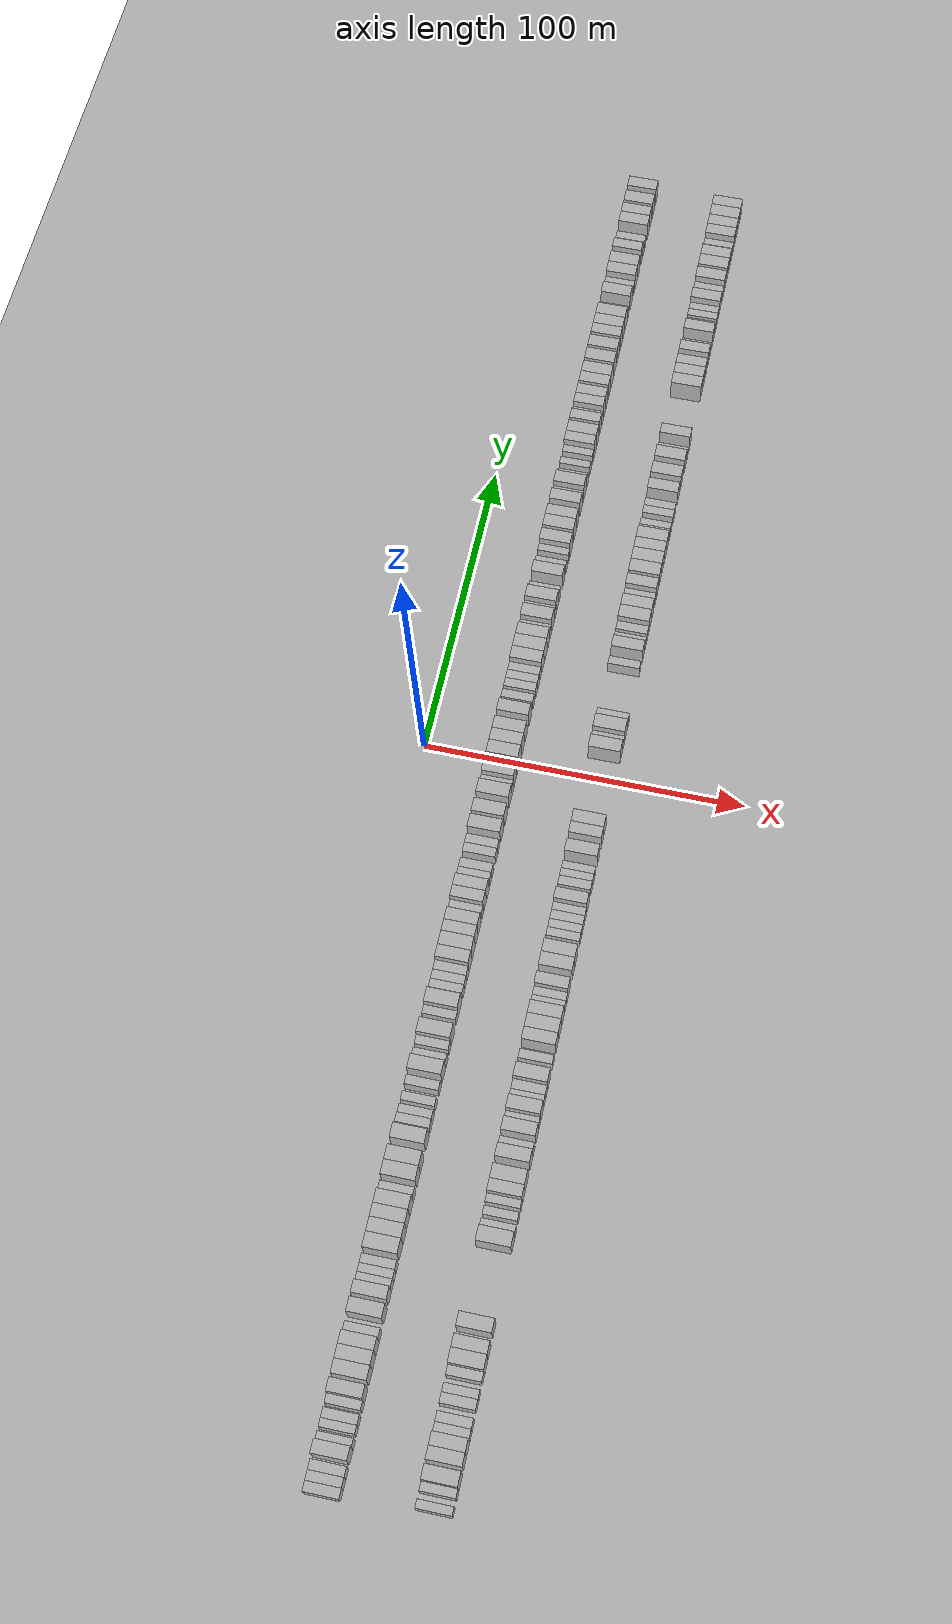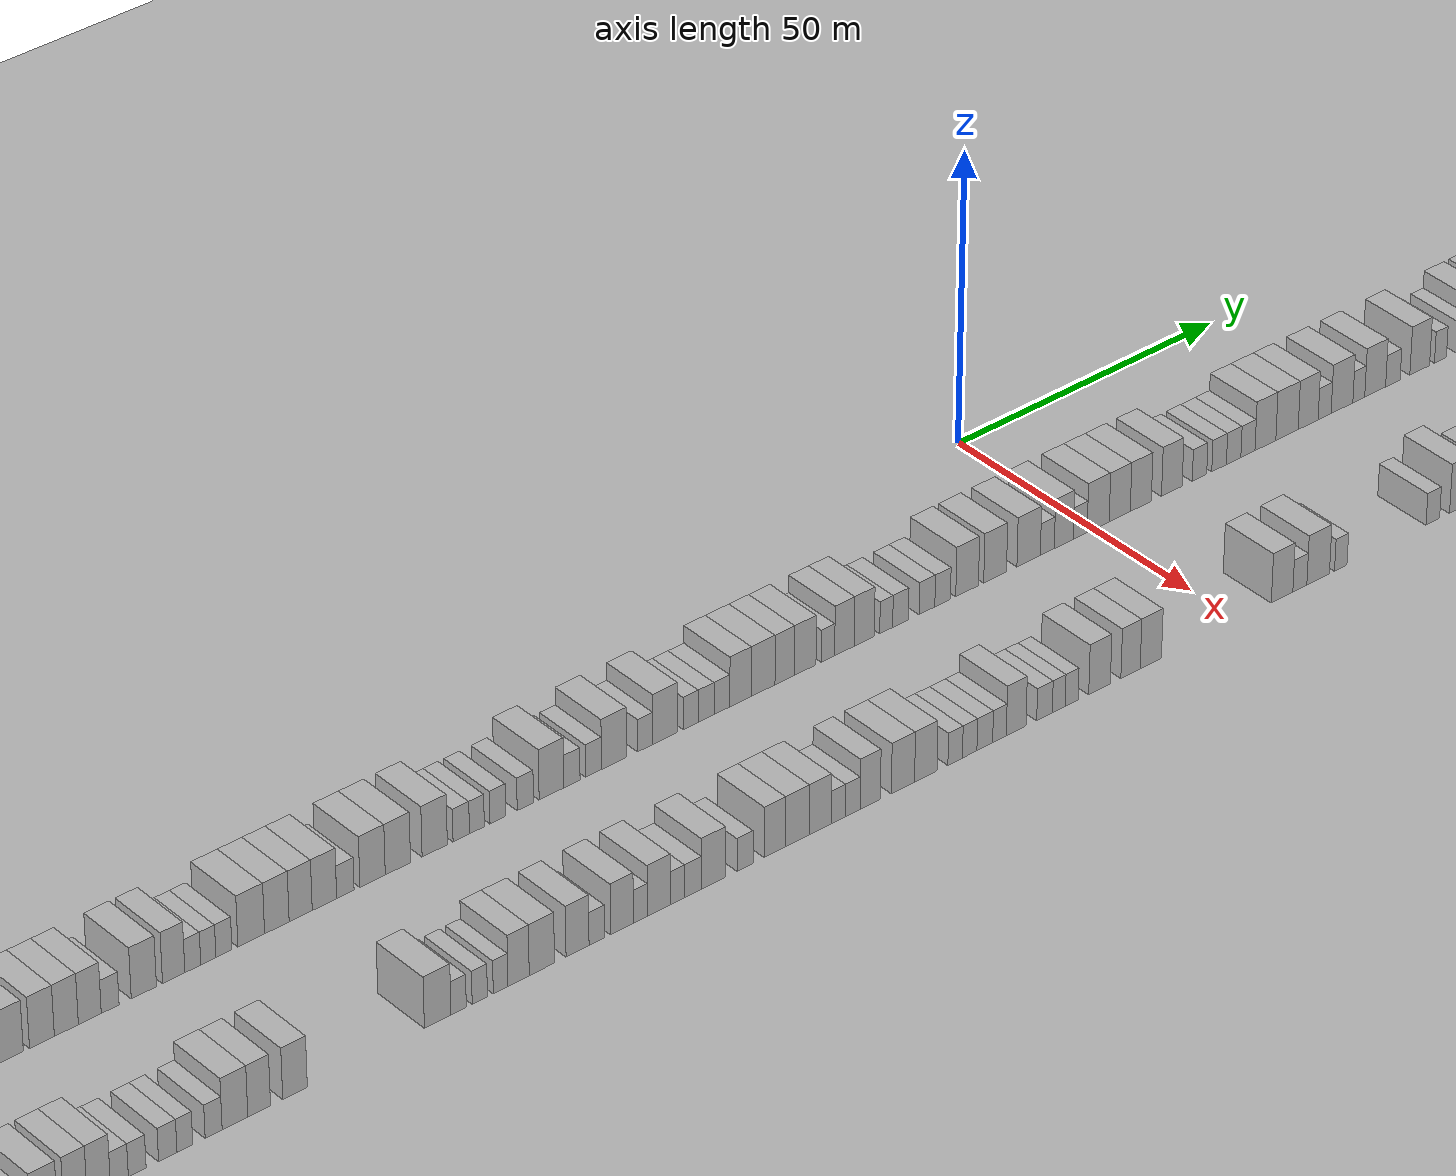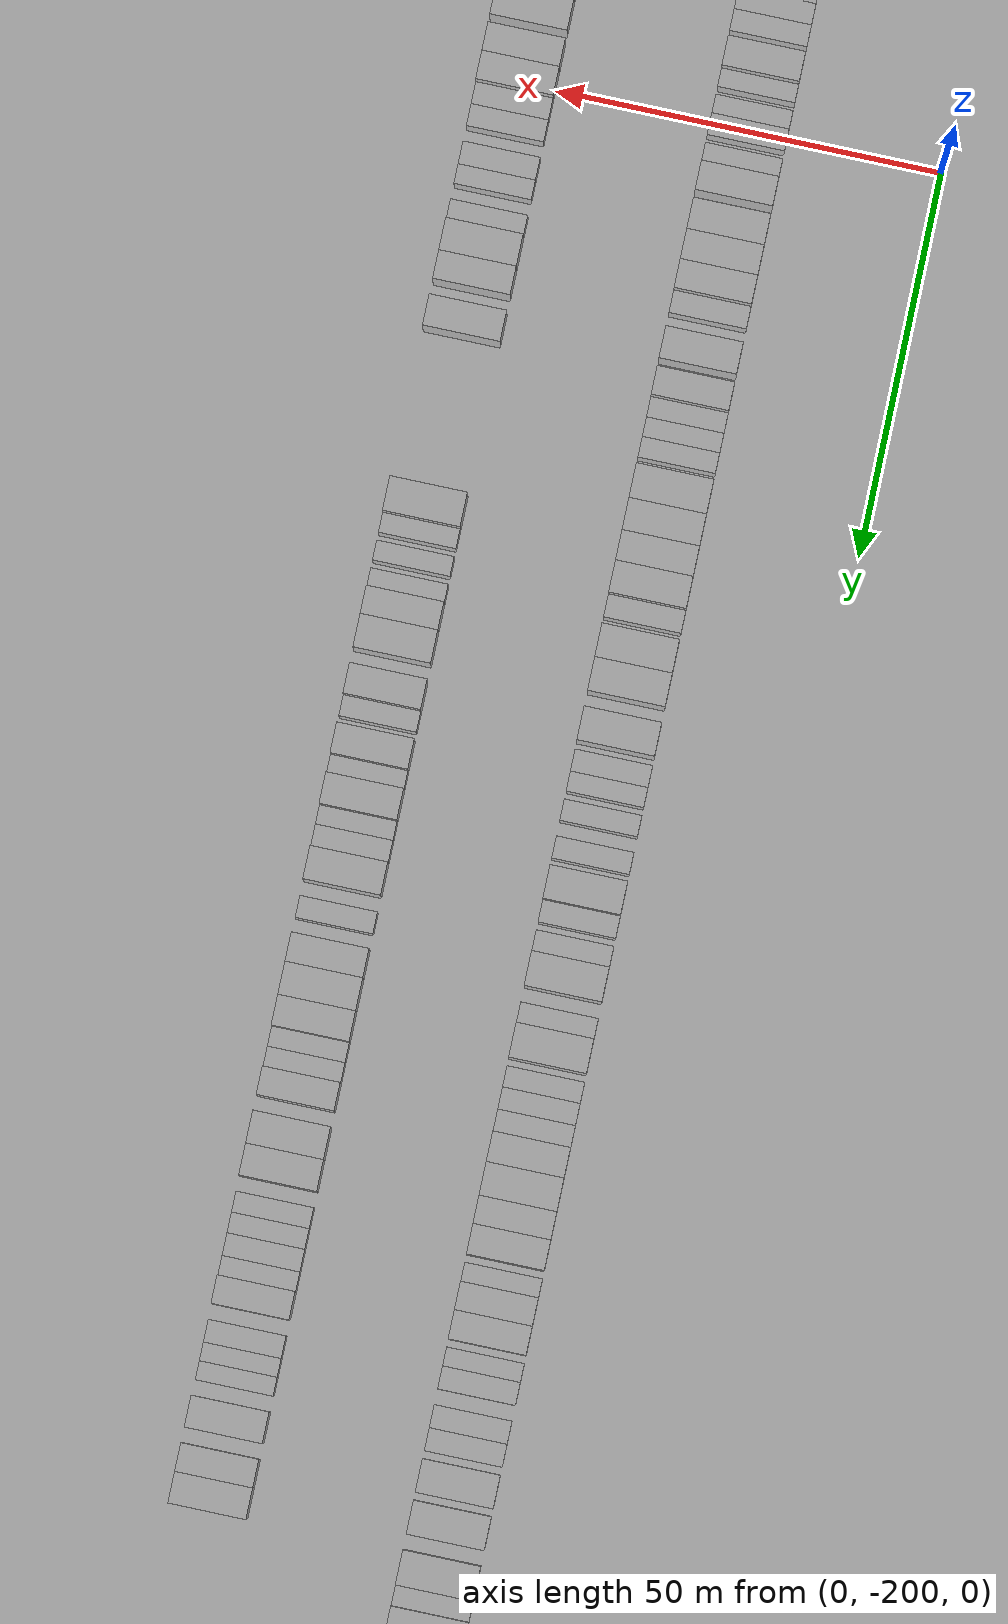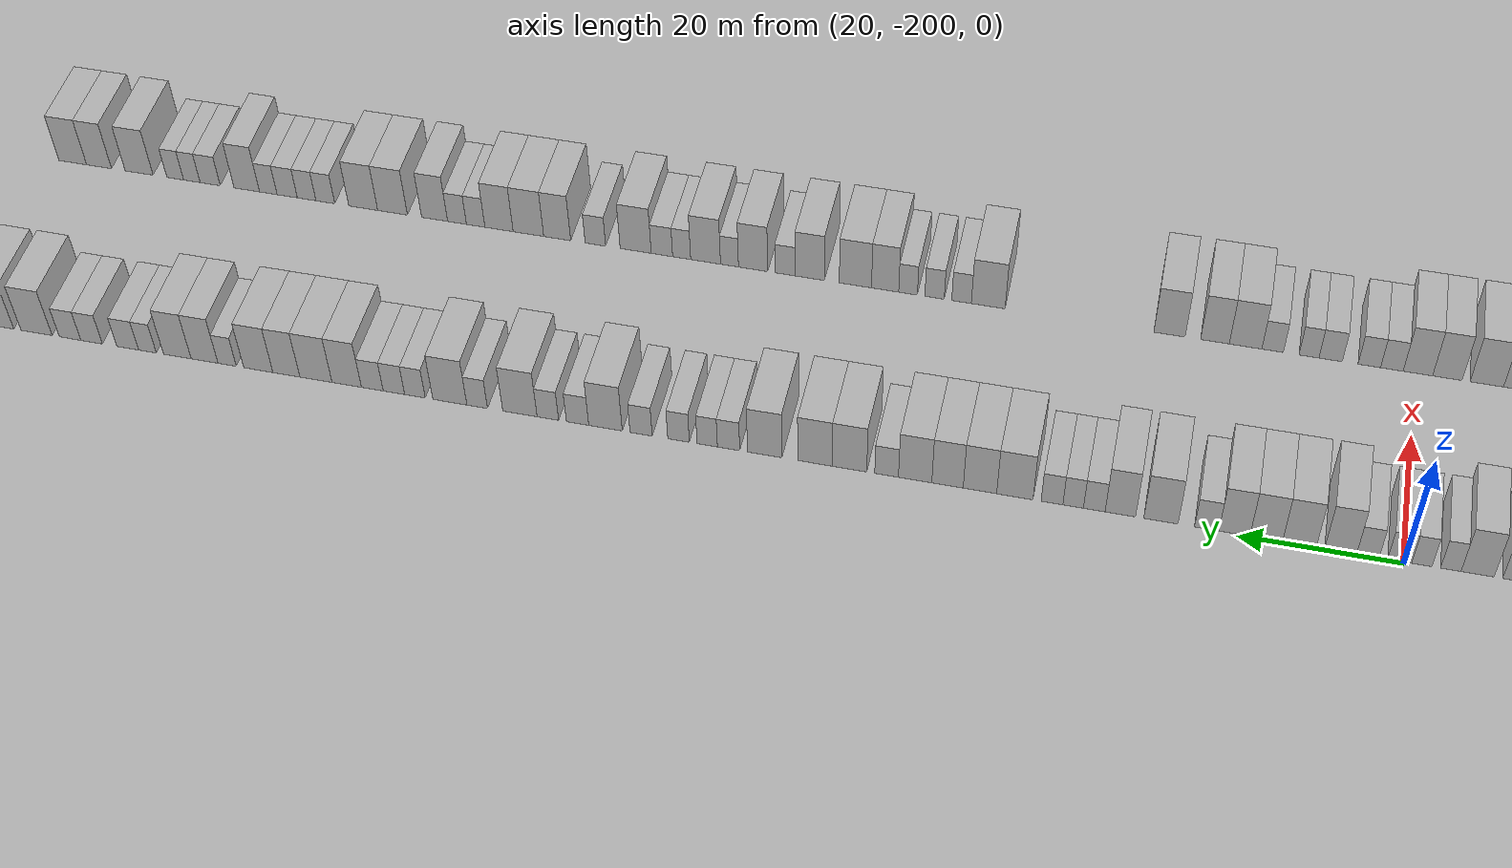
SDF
<?xml version="1.0" encoding="utf-8"?>

<sdf version="1.6">

   <world name="default">

      <gui fullscreen="0">

         <camera name="user_camera">

            <pose>-15 0 4.57585 0 0 0</pose>

            <view_controller>orbit</view_controller>

         </camera>

      </gui>

      <scene>

         <sky>

           <clouds>

             <speed>12</speed>

           </clouds>

         </sky>

         <ambient>0.4 0.4 0.4 1</ambient>

         <background>0.7 0.7 0.7 1</background>

         <shadows>1</shadows>

      </scene>

      <gravity>0 0 -9.8066</gravity>

      <magnetic_field>6e-06 2.3e-05 -4.2e-05</magnetic_field>

      <physics default="0" name="default_physics" type="ode">

         <ode>

            <solver>

               <type>quick</type>

               <iters>10</iters>

               <sor>1.0</sor>

               <use_dynamic_moi_rescaling>0</use_dynamic_moi_rescaling>

            </solver>

            <constraints>

               <cfm>0</cfm>

               <erp>0.2</erp>

               <contact_max_correcting_vel>100</contact_max_correcting_vel>

               <contact_surface_layer>0.001</contact_surface_layer>

            </constraints>

         </ode>

         <max_step_size>0.004</max_step_size>

         <real_time_factor>1</real_time_factor>

         <real_time_update_rate>250</real_time_update_rate>

      </physics>

      <light name="sun" type="directional">

         <cast_shadows>1</cast_shadows>

         <pose>0 0 10 0 0 0</pose>

         <diffuse>0.8 0.8 0.8 1</diffuse>

         <specular>0.2 0.2 0.2 1</specular>

         <attenuation>

            <range>1000</range>

            <constant>0.9</constant>

            <linear>0.01</linear>

            <quadratic>0.001</quadratic>

         </attenuation>

         <direction>-0.5 0.1 -0.9</direction>

      </light>

      <include>

         <name>ground_plane_1</name>

         <uri>model://HANNAS_ground_plane</uri>

         <pose>0 0 0  0 0 0</pose>

      </include>

      <include>

         <name>ground_plane_2</name>

         <uri>model://HANNAS_ground_plane</uri>

         <pose>100 0 0  0 0 0</pose>

      </include>

      <model name="building_1">

         <static>1</static>

         <pose frame="">25.0000 -218.5558 0 0.000000 0.000000 0.000000</pose>

         <link name="link">

            <pose frame="">0 0 3.00 0 0 0</pose>

            <collision name="collision">

               <geometry>

                  <box>

                     <size>10.0000 2.8884 6.0000</size>

                  </box>

               </geometry>

               <max_contacts>10</max_contacts>

               <surface>

                  <contact>

                     <ode/>

                  </contact>

                  <bounce/>

                  <friction>

                     <torsional>

                        <ode/>

                     </torsional>

                     <ode/>

                  </friction>

               </surface>

            </collision>

            <visual name="visual">

               <cast_shadows>0</cast_shadows>

               <geometry>

                  <box>

                     <size>10.0000 2.8884 6.0000</size>

                  </box>

               </geometry>

               <material>

                  <script>

                     <uri>model://HANNAS_wall/materials/scripts</uri>

                     <uri>model://HANNAS_wall/materials/textures</uri>

                     <name>vrc/HANNAS_wall</name>

                  </script>

               </material>

            </visual>

            <self_collide>0</self_collide>

            <enable_wind>0</enable_wind>

            <kinematic>0</kinematic>

         </link>

      </model>

      <model name="building_2">

         <static>1</static>

         <pose frame="">25.0000 -215.7326 0 0.000000 0.000000 0.000000</pose>

         <link name="link">

            <pose frame="">0 0 3.00 0 0 0</pose>

            <collision name="collision">

               <geometry>

                  <box>

                     <size>10.0000 2.7580 6.0000</size>

                  </box>

               </geometry>

               <max_contacts>10</max_contacts>

               <surface>

                  <contact>

                     <ode/>

                  </contact>

                  <bounce/>

                  <friction>

                     <torsional>

                        <ode/>

                     </torsional>

                     <ode/>

                  </friction>

               </surface>

            </collision>

            <visual name="visual">

               <cast_shadows>0</cast_shadows>

               <geometry>

                  <box>

                     <size>10.0000 2.7580 6.0000</size>

                  </box>

               </geometry>

               <material>

                  <script>

                     <uri>model://HANNAS_wall/materials/scripts</uri>

                     <uri>model://HANNAS_wall/materials/textures</uri>

                     <name>vrc/HANNAS_wall</name>

                  </script>

               </material>

            </visual>

            <self_collide>0</self_collide>

            <enable_wind>0</enable_wind>

            <kinematic>0</kinematic>

         </link>

      </model>

      <model name="building_3">

         <static>1</static>

         <pose frame="">25.0000 -212.9331 0 0.000000 0.000000 0.000000</pose>

         <link name="link">

            <pose frame="">0 0 3.00 0 0 0</pose>

            <collision name="collision">

               <geometry>

                  <box>

                     <size>10.0000 2.8410 6.0000</size>

                  </box>

               </geometry>

               <max_contacts>10</max_contacts>

               <surface>

                  <contact>

                     <ode/>

                  </contact>

                  <bounce/>

                  <friction>

                     <torsional>

                        <ode/>

                     </torsional>

                     <ode/>

                  </friction>

               </surface>

            </collision>

            <visual name="visual">

               <cast_shadows>0</cast_shadows>

               <geometry>

                  <box>

                     <size>10.0000 2.8410 6.0000</size>

                  </box>

               </geometry>

               <material>

                  <script>

                     <uri>model://HANNAS_wall/materials/scripts</uri>

                     <uri>model://HANNAS_wall/materials/textures</uri>

                     <name>vrc/HANNAS_wall</name>

                  </script>

               </material>

            </visual>

            <self_collide>0</self_collide>

            <enable_wind>0</enable_wind>

            <kinematic>0</kinematic>

         </link>

      </model>

      <model name="building_4">

         <static>1</static>

         <pose frame="">25.0000 -208.5727 0 0.000000 0.000000 0.000000</pose>

         <link name="link">

            <pose frame="">0 0 4.50 0 0 0</pose>

            <collision name="collision">

               <geometry>

                  <box>

                     <size>10.0000 3.8800 9.0000</size>

                  </box>

               </geometry>

               <max_contacts>10</max_contacts>

               <surface>

                  <contact>

                     <ode/>

                  </contact>

                  <bounce/>

                  <friction>

                     <torsional>

                        <ode/>

                     </torsional>

                     <ode/>

                  </friction>

               </surface>

            </collision>

            <visual name="visual">

               <cast_shadows>0</cast_shadows>

               <geometry>

                  <box>

                     <size>10.0000 3.8800 9.0000</size>

                  </box>

               </geometry>

               <material>

                  <script>

                     <uri>model://HANNAS_wall/materials/scripts</uri>

                     <uri>model://HANNAS_wall/materials/textures</uri>

                     <name>vrc/HANNAS_wall</name>

                  </script>

               </material>

            </visual>

            <self_collide>0</self_collide>

            <enable_wind>0</enable_wind>

            <kinematic>0</kinematic>

         </link>

      </model>

      <model name="building_5">

         <static>1</static>

         <pose frame="">25.0000 -205.4299 0 0.000000 0.000000 0.000000</pose>

         <link name="link">

            <pose frame="">0 0 3.00 0 0 0</pose>

            <collision name="collision">

               <geometry>

                  <box>

                     <size>10.0000 2.4056 6.0000</size>

                  </box>

               </geometry>

               <max_contacts>10</max_contacts>

               <surface>

                  <contact>

                     <ode/>

                  </contact>

                  <bounce/>

                  <friction>

                     <torsional>

                        <ode/>

                     </torsional>

                     <ode/>

                  </friction>

               </surface>

            </collision>

            <visual name="visual">

               <cast_shadows>0</cast_shadows>

               <geometry>

                  <box>

                     <size>10.0000 2.4056 6.0000</size>

                  </box>

               </geometry>

               <material>

                  <script>

                     <uri>model://HANNAS_wall/materials/scripts</uri>

                     <uri>model://HANNAS_wall/materials/textures</uri>

                     <name>vrc/HANNAS_wall</name>

                  </script>

               </material>

            </visual>

            <self_collide>0</self_collide>

            <enable_wind>0</enable_wind>

            <kinematic>0</kinematic>

         </link>

      </model>

      <model name="building_6">

         <static>1</static>

         <pose frame="">25.0000 -202.0179 0 0.000000 0.000000 0.000000</pose>

         <link name="link">

            <pose frame="">0 0 3.00 0 0 0</pose>

            <collision name="collision">

               <geometry>

                  <box>

                     <size>10.0000 2.4182 6.0000</size>

                  </box>

               </geometry>

               <max_contacts>10</max_contacts>

               <surface>

                  <contact>

                     <ode/>

                  </contact>

                  <bounce/>

                  <friction>

                     <torsional>

                        <ode/>

                     </torsional>

                     <ode/>

                  </friction>

               </surface>

            </collision>

            <visual name="visual">

               <cast_shadows>0</cast_shadows>

               <geometry>

                  <box>

                     <size>10.0000 2.4182 6.0000</size>

                  </box>

               </geometry>

               <material>

                  <script>

                     <uri>model://HANNAS_wall/materials/scripts</uri>

                     <uri>model://HANNAS_wall/materials/textures</uri>

                     <name>vrc/HANNAS_wall</name>

                  </script>

               </material>

            </visual>

            <self_collide>0</self_collide>

            <enable_wind>0</enable_wind>

            <kinematic>0</kinematic>

         </link>

      </model>

      <model name="building_7">

         <static>1</static>

         <pose frame="">25.0000 -199.3907 0 0.000000 0.000000 0.000000</pose>

         <link name="link">

            <pose frame="">0 0 3.00 0 0 0</pose>

            <collision name="collision">

               <geometry>

                  <box>

                     <size>10.0000 2.8362 6.0000</size>

                  </box>

               </geometry>

               <max_contacts>10</max_contacts>

               <surface>

                  <contact>

                     <ode/>

                  </contact>

                  <bounce/>

                  <friction>

                     <torsional>

                        <ode/>

                     </torsional>

                     <ode/>

                  </friction>

               </surface>

            </collision>

            <visual name="visual">

               <cast_shadows>0</cast_shadows>

               <geometry>

                  <box>

                     <size>10.0000 2.8362 6.0000</size>

                  </box>

               </geometry>

               <material>

                  <script>

                     <uri>model://HANNAS_wall/materials/scripts</uri>

                     <uri>model://HANNAS_wall/materials/textures</uri>

                     <name>vrc/HANNAS_wall</name>

                  </script>

               </material>

            </visual>

            <self_collide>0</self_collide>

            <enable_wind>0</enable_wind>

            <kinematic>0</kinematic>

         </link>

      </model>

      <model name="building_8">

         <static>1</static>

         <pose frame="">25.0000 -195.6416 0 0.000000 0.000000 0.000000</pose>

         <link name="link">

            <pose frame="">0 0 3.00 0 0 0</pose>

            <collision name="collision">

               <geometry>

                  <box>

                     <size>10.0000 2.6619 6.0000</size>

                  </box>

               </geometry>

               <max_contacts>10</max_contacts>

               <surface>

                  <contact>

                     <ode/>

                  </contact>

                  <bounce/>

                  <friction>

                     <torsional>

                        <ode/>

                     </torsional>

                     <ode/>

                  </friction>

               </surface>

            </collision>

            <visual name="visual">

               <cast_shadows>0</cast_shadows>

               <geometry>

                  <box>

                     <size>10.0000 2.6619 6.0000</size>

                  </box>

               </geometry>

               <material>

                  <script>

                     <uri>model://HANNAS_wall/materials/scripts</uri>

                     <uri>model://HANNAS_wall/materials/textures</uri>

                     <name>vrc/HANNAS_wall</name>

                  </script>

               </material>

            </visual>

            <self_collide>0</self_collide>

            <enable_wind>0</enable_wind>

            <kinematic>0</kinematic>

         </link>

      </model>

      <model name="building_9">

         <static>1</static>

         <pose frame="">25.0000 -192.4022 0 0.000000 0.000000 0.000000</pose>

         <link name="link">

            <pose frame="">0 0 4.50 0 0 0</pose>

            <collision name="collision">

               <geometry>

                  <box>

                     <size>10.0000 3.8170 9.0000</size>

                  </box>

               </geometry>

               <max_contacts>10</max_contacts>

               <surface>

                  <contact>

                     <ode/>

                  </contact>

                  <bounce/>

                  <friction>

                     <torsional>

                        <ode/>

                     </torsional>

                     <ode/>

                  </friction>

               </surface>

            </collision>

            <visual name="visual">

               <cast_shadows>0</cast_shadows>

               <geometry>

                  <box>

                     <size>10.0000 3.8170 9.0000</size>

                  </box>

               </geometry>

               <material>

                  <script>

                     <uri>model://HANNAS_wall/materials/scripts</uri>

                     <uri>model://HANNAS_wall/materials/textures</uri>

                     <name>vrc/HANNAS_wall</name>

                  </script>

               </material>

            </visual>

            <self_collide>0</self_collide>

            <enable_wind>0</enable_wind>

            <kinematic>0</kinematic>

         </link>

      </model>

      <model name="building_10">

         <static>1</static>

         <pose frame="">25.0000 -187.4737 0 0.000000 0.000000 0.000000</pose>

         <link name="link">

            <pose frame="">0 0 4.50 0 0 0</pose>

            <collision name="collision">

               <geometry>

                  <box>

                     <size>10.0000 4.0400 9.0000</size>

                  </box>

               </geometry>

               <max_contacts>10</max_contacts>

               <surface>

                  <contact>

                     <ode/>

                  </contact>

                  <bounce/>

                  <friction>

                     <torsional>

                        <ode/>

                     </torsional>

                     <ode/>

                  </friction>

               </surface>

            </collision>

            <visual name="visual">

               <cast_shadows>0</cast_shadows>

               <geometry>

                  <box>

                     <size>10.0000 4.0400 9.0000</size>

                  </box>

               </geometry>

               <material>

                  <script>

                     <uri>model://HANNAS_wall/materials/scripts</uri>

                     <uri>model://HANNAS_wall/materials/textures</uri>

                     <name>vrc/HANNAS_wall</name>

                  </script>

               </material>

            </visual>

            <self_collide>0</self_collide>

            <enable_wind>0</enable_wind>

            <kinematic>0</kinematic>

         </link>

      </model>

      <model name="building_11">

         <static>1</static>

         <pose frame="">25.0000 -183.4973 0 0.000000 0.000000 0.000000</pose>

         <link name="link">

            <pose frame="">0 0 4.50 0 0 0</pose>

            <collision name="collision">

               <geometry>

                  <box>

                     <size>10.0000 3.9128 9.0000</size>

                  </box>

               </geometry>

               <max_contacts>10</max_contacts>

               <surface>

                  <contact>

                     <ode/>

                  </contact>

                  <bounce/>

                  <friction>

                     <torsional>

                        <ode/>

                     </torsional>

                     <ode/>

                  </friction>

               </surface>

            </collision>

            <visual name="visual">

               <cast_shadows>0</cast_shadows>

               <geometry>

                  <box>

                     <size>10.0000 3.9128 9.0000</size>

                  </box>

               </geometry>

               <material>

                  <script>

                     <uri>model://HANNAS_wall/materials/scripts</uri>

                     <uri>model://HANNAS_wall/materials/textures</uri>

                     <name>vrc/HANNAS_wall</name>

                  </script>

               </material>

            </visual>

            <self_collide>0</self_collide>

            <enable_wind>0</enable_wind>

            <kinematic>0</kinematic>

         </link>

      </model>

      <model name="building_12">

         <static>1</static>

         <pose frame="">25.0000 -179.6681 0 0.000000 0.000000 0.000000</pose>

         <link name="link">

            <pose frame="">0 0 4.50 0 0 0</pose>

            <collision name="collision">

               <geometry>

                  <box>

                     <size>10.0000 3.7454 9.0000</size>

                  </box>

               </geometry>

               <max_contacts>10</max_contacts>

               <surface>

                  <contact>

                     <ode/>

                  </contact>

                  <bounce/>

                  <friction>

                     <torsional>

                        <ode/>

                     </torsional>

                     <ode/>

                  </friction>

               </surface>

            </collision>

            <visual name="visual">

               <cast_shadows>0</cast_shadows>

               <geometry>

                  <box>

                     <size>10.0000 3.7454 9.0000</size>

                  </box>

               </geometry>

               <material>

                  <script>

                     <uri>model://HANNAS_wall/materials/scripts</uri>

                     <uri>model://HANNAS_wall/materials/textures</uri>

                     <name>vrc/HANNAS_wall</name>

                  </script>

               </material>

            </visual>

            <self_collide>0</self_collide>

            <enable_wind>0</enable_wind>

            <kinematic>0</kinematic>

         </link>

      </model>

      <model name="building_13">

         <static>1</static>

         <pose frame="">25.0000 -176.3302 0 0.000000 0.000000 0.000000</pose>

         <link name="link">

            <pose frame="">0 0 3.00 0 0 0</pose>

            <collision name="collision">

               <geometry>

                  <box>

                     <size>10.0000 2.9305 6.0000</size>

                  </box>

               </geometry>

               <max_contacts>10</max_contacts>

               <surface>

                  <contact>

                     <ode/>

                  </contact>

                  <bounce/>

                  <friction>

                     <torsional>

                        <ode/>

                     </torsional>

                     <ode/>

                  </friction>

               </surface>

            </collision>

            <visual name="visual">

               <cast_shadows>0</cast_shadows>

               <geometry>

                  <box>

                     <size>10.0000 2.9305 6.0000</size>

                  </box>

               </geometry>

               <material>

                  <script>

                     <uri>model://HANNAS_wall/materials/scripts</uri>

                     <uri>model://HANNAS_wall/materials/textures</uri>

                     <name>vrc/HANNAS_wall</name>

                  </script>

               </material>

            </visual>

            <self_collide>0</self_collide>

            <enable_wind>0</enable_wind>

            <kinematic>0</kinematic>

         </link>

      </model>

      <model name="building_14">

         <static>1</static>

         <pose frame="">25.0000 -170.7841 0 0.000000 0.000000 0.000000</pose>

         <link name="link">

            <pose frame="">0 0 4.50 0 0 0</pose>

            <collision name="collision">

               <geometry>

                  <box>

                     <size>10.0000 4.1616 9.0000</size>

                  </box>

               </geometry>

               <max_contacts>10</max_contacts>

               <surface>

                  <contact>

                     <ode/>

                  </contact>

                  <bounce/>

                  <friction>

                     <torsional>

                        <ode/>

                     </torsional>

                     <ode/>

                  </friction>

               </surface>

            </collision>

            <visual name="visual">

               <cast_shadows>0</cast_shadows>

               <geometry>

                  <box>

                     <size>10.0000 4.1616 9.0000</size>

                  </box>

               </geometry>

               <material>

                  <script>

                     <uri>model://HANNAS_wall/materials/scripts</uri>

                     <uri>model://HANNAS_wall/materials/textures</uri>

                     <name>vrc/HANNAS_wall</name>

                  </script>

               </material>

            </visual>

            <self_collide>0</self_collide>

            <enable_wind>0</enable_wind>

            <kinematic>0</kinematic>

         </link>

      </model>

      <model name="building_15">

         <static>1</static>

         <pose frame="">25.0000 -165.8461 0 0.000000 0.000000 0.000000</pose>

         <link name="link">

            <pose frame="">0 0 4.50 0 0 0</pose>

            <collision name="collision">

               <geometry>

                  <box>

                     <size>10.0000 3.7143 9.0000</size>

                  </box>

               </geometry>

               <max_contacts>10</max_contacts>

               <surface>

                  <contact>

                     <ode/>

                  </contact>

                  <bounce/>

                  <friction>

                     <torsional>

                        <ode/>

                     </torsional>

                     <ode/>

                  </friction>

               </surface>

            </collision>

            <visual name="visual">

               <cast_shadows>0</cast_shadows>

               <geometry>

                  <box>

                     <size>10.0000 3.7143 9.0000</size>

                  </box>

               </geometry>

               <material>

                  <script>

                     <uri>model://HANNAS_wall/materials/scripts</uri>

                     <uri>model://HANNAS_wall/materials/textures</uri>

                     <name>vrc/HANNAS_wall</name>

                  </script>

               </material>

            </visual>

            <self_collide>0</self_collide>

            <enable_wind>0</enable_wind>

            <kinematic>0</kinematic>

         </link>

      </model>

      <model name="building_16">

         <static>1</static>

         <pose frame="">25.0000 -162.6667 0 0.000000 0.000000 0.000000</pose>

         <link name="link">

            <pose frame="">0 0 3.00 0 0 0</pose>

            <collision name="collision">

               <geometry>

                  <box>

                     <size>10.0000 2.6445 6.0000</size>

                  </box>

               </geometry>

               <max_contacts>10</max_contacts>

               <surface>

                  <contact>

                     <ode/>

                  </contact>

                  <bounce/>

                  <friction>

                     <torsional>

                        <ode/>

                     </torsional>

                     <ode/>

                  </friction>

               </surface>

            </collision>

            <visual name="visual">

               <cast_shadows>0</cast_shadows>

               <geometry>

                  <box>

                     <size>10.0000 2.6445 6.0000</size>

                  </box>

               </geometry>

               <material>

                  <script>

                     <uri>model://HANNAS_wall/materials/scripts</uri>

                     <uri>model://HANNAS_wall/materials/textures</uri>

                     <name>vrc/HANNAS_wall</name>

                  </script>

               </material>

            </visual>

            <self_collide>0</self_collide>

            <enable_wind>0</enable_wind>

            <kinematic>0</kinematic>

         </link>

      </model>

      <model name="building_17">

         <static>1</static>

         <pose frame="">25.0000 -160.0820 0 0.000000 0.000000 0.000000</pose>

         <link name="link">

            <pose frame="">0 0 3.00 0 0 0</pose>

            <collision name="collision">

               <geometry>

                  <box>

                     <size>10.0000 2.5250 6.0000</size>

                  </box>

               </geometry>

               <max_contacts>10</max_contacts>

               <surface>

                  <contact>

                     <ode/>

                  </contact>

                  <bounce/>

                  <friction>

                     <torsional>

                        <ode/>

                     </torsional>

                     <ode/>

                  </friction>

               </surface>

            </collision>

            <visual name="visual">

               <cast_shadows>0</cast_shadows>

               <geometry>

                  <box>

                     <size>10.0000 2.5250 6.0000</size>

                  </box>

               </geometry>

               <material>

                  <script>

                     <uri>model://HANNAS_wall/materials/scripts</uri>

                     <uri>model://HANNAS_wall/materials/textures</uri>

                     <name>vrc/HANNAS_wall</name>

                  </script>

               </material>

            </visual>

            <self_collide>0</self_collide>

            <enable_wind>0</enable_wind>

            <kinematic>0</kinematic>

         </link>

      </model>

      <model name="building_18">

         <static>1</static>

         <pose frame="">25.0000 -157.4782 0 0.000000 0.000000 0.000000</pose>

         <link name="link">

            <pose frame="">0 0 3.00 0 0 0</pose>

            <collision name="collision">

               <geometry>

                  <box>

                     <size>10.0000 2.6825 6.0000</size>

                  </box>

               </geometry>

               <max_contacts>10</max_contacts>

               <surface>

                  <contact>

                     <ode/>

                  </contact>

                  <bounce/>

                  <friction>

                     <torsional>

                        <ode/>

                     </torsional>

                     <ode/>

                  </friction>

               </surface>

            </collision>

            <visual name="visual">

               <cast_shadows>0</cast_shadows>

               <geometry>

                  <box>

                     <size>10.0000 2.6825 6.0000</size>

                  </box>

               </geometry>

               <material>

                  <script>

                     <uri>model://HANNAS_wall/materials/scripts</uri>

                     <uri>model://HANNAS_wall/materials/textures</uri>

                     <name>vrc/HANNAS_wall</name>

                  </script>

               </material>

            </visual>

            <self_collide>0</self_collide>

            <enable_wind>0</enable_wind>

            <kinematic>0</kinematic>

         </link>

      </model>

      <model name="building_19">

         <static>1</static>

         <pose frame="">25.0000 -152.8965 0 0.000000 0.000000 0.000000</pose>

         <link name="link">

            <pose frame="">0 0 4.50 0 0 0</pose>

            <collision name="collision">

               <geometry>

                  <box>

                     <size>10.0000 4.4811 9.0000</size>

                  </box>

               </geometry>

               <max_contacts>10</max_contacts>

               <surface>

                  <contact>

                     <ode/>

                  </contact>

                  <bounce/>

                  <friction>

                     <torsional>

                        <ode/>

                     </torsional>

                     <ode/>

                  </friction>

               </surface>

            </collision>

            <visual name="visual">

               <cast_shadows>0</cast_shadows>

               <geometry>

                  <box>

                     <size>10.0000 4.4811 9.0000</size>

                  </box>

               </geometry>

               <material>

                  <script>

                     <uri>model://HANNAS_wall/materials/scripts</uri>

                     <uri>model://HANNAS_wall/materials/textures</uri>

                     <name>vrc/HANNAS_wall</name>

                  </script>

               </material>

            </visual>

            <self_collide>0</self_collide>

            <enable_wind>0</enable_wind>

            <kinematic>0</kinematic>

         </link>

      </model>

      <model name="building_20">

         <static>1</static>

         <pose frame="">25.0000 -148.5810 0 0.000000 0.000000 0.000000</pose>

         <link name="link">

            <pose frame="">0 0 4.50 0 0 0</pose>

            <collision name="collision">

               <geometry>

                  <box>

                     <size>10.0000 4.1498 9.0000</size>

                  </box>

               </geometry>

               <max_contacts>10</max_contacts>

               <surface>

                  <contact>

                     <ode/>

                  </contact>

                  <bounce/>

                  <friction>

                     <torsional>

                        <ode/>

                     </torsional>

                     <ode/>

                  </friction>

               </surface>

            </collision>

            <visual name="visual">

               <cast_shadows>0</cast_shadows>

               <geometry>

                  <box>

                     <size>10.0000 4.1498 9.0000</size>

                  </box>

               </geometry>

               <material>

                  <script>

                     <uri>model://HANNAS_wall/materials/scripts</uri>

                     <uri>model://HANNAS_wall/materials/textures</uri>

                     <name>vrc/HANNAS_wall</name>

                  </script>

               </material>

            </visual>

            <self_collide>0</self_collide>

            <enable_wind>0</enable_wind>

            <kinematic>0</kinematic>

         </link>

      </model>

      <model name="building_21">

         <static>1</static>

         <pose frame="">25.0000 -144.5503 0 0.000000 0.000000 0.000000</pose>

         <link name="link">

            <pose frame="">0 0 4.50 0 0 0</pose>

            <collision name="collision">

               <geometry>

                  <box>

                     <size>10.0000 3.9116 9.0000</size>

                  </box>

               </geometry>

               <max_contacts>10</max_contacts>

               <surface>

                  <contact>

                     <ode/>

                  </contact>

                  <bounce/>

                  <friction>

                     <torsional>

                        <ode/>

                     </torsional>

                     <ode/>

                  </friction>

               </surface>

            </collision>

            <visual name="visual">

               <cast_shadows>0</cast_shadows>

               <geometry>

                  <box>

                     <size>10.0000 3.9116 9.0000</size>

                  </box>

               </geometry>

               <material>

                  <script>

                     <uri>model://HANNAS_wall/materials/scripts</uri>

                     <uri>model://HANNAS_wall/materials/textures</uri>

                     <name>vrc/HANNAS_wall</name>

                  </script>

               </material>

            </visual>

            <self_collide>0</self_collide>

            <enable_wind>0</enable_wind>

            <kinematic>0</kinematic>

         </link>

      </model>

      <model name="building_22">

         <static>1</static>

         <pose frame="">25.0000 -140.5133 0 0.000000 0.000000 0.000000</pose>

         <link name="link">

            <pose frame="">0 0 4.50 0 0 0</pose>

            <collision name="collision">

               <geometry>

                  <box>

                     <size>10.0000 4.1624 9.0000</size>

                  </box>

               </geometry>

               <max_contacts>10</max_contacts>

               <surface>

                  <contact>

                     <ode/>

                  </contact>

                  <bounce/>

                  <friction>

                     <torsional>

                        <ode/>

                     </torsional>

                     <ode/>

                  </friction>

               </surface>

            </collision>

            <visual name="visual">

               <cast_shadows>0</cast_shadows>

               <geometry>

                  <box>

                     <size>10.0000 4.1624 9.0000</size>

                  </box>

               </geometry>

               <material>

                  <script>

                     <uri>model://HANNAS_wall/materials/scripts</uri>

                     <uri>model://HANNAS_wall/materials/textures</uri>

                     <name>vrc/HANNAS_wall</name>

                  </script>

               </material>

            </visual>

            <self_collide>0</self_collide>

            <enable_wind>0</enable_wind>

            <kinematic>0</kinematic>

         </link>

      </model>

      <model name="building_23">

         <static>1</static>

         <pose frame="">25.0000 -136.9468 0 0.000000 0.000000 0.000000</pose>

         <link name="link">

            <pose frame="">0 0 3.00 0 0 0</pose>

            <collision name="collision">

               <geometry>

                  <box>

                     <size>10.0000 2.9705 6.0000</size>

                  </box>

               </geometry>

               <max_contacts>10</max_contacts>

               <surface>

                  <contact>

                     <ode/>

                  </contact>

                  <bounce/>

                  <friction>

                     <torsional>

                        <ode/>

                     </torsional>

                     <ode/>

                  </friction>

               </surface>

            </collision>

            <visual name="visual">

               <cast_shadows>0</cast_shadows>

               <geometry>

                  <box>

                     <size>10.0000 2.9705 6.0000</size>

                  </box>

               </geometry>

               <material>

                  <script>

                     <uri>model://HANNAS_wall/materials/scripts</uri>

                     <uri>model://HANNAS_wall/materials/textures</uri>

                     <name>vrc/HANNAS_wall</name>

                  </script>

               </material>

            </visual>

            <self_collide>0</self_collide>

            <enable_wind>0</enable_wind>

            <kinematic>0</kinematic>

         </link>

      </model>

      <model name="building_24">

         <static>1</static>

         <pose frame="">25.0000 -132.2876 0 0.000000 0.000000 0.000000</pose>

         <link name="link">

            <pose frame="">0 0 4.50 0 0 0</pose>

            <collision name="collision">

               <geometry>

                  <box>

                     <size>10.0000 4.3480 9.0000</size>

                  </box>

               </geometry>

               <max_contacts>10</max_contacts>

               <surface>

                  <contact>

                     <ode/>

                  </contact>

                  <bounce/>

                  <friction>

                     <torsional>

                        <ode/>

                     </torsional>

                     <ode/>

                  </friction>

               </surface>

            </collision>

            <visual name="visual">

               <cast_shadows>0</cast_shadows>

               <geometry>

                  <box>

                     <size>10.0000 4.3480 9.0000</size>

                  </box>

               </geometry>

               <material>

                  <script>

                     <uri>model://HANNAS_wall/materials/scripts</uri>

                     <uri>model://HANNAS_wall/materials/textures</uri>

                     <name>vrc/HANNAS_wall</name>

                  </script>

               </material>

            </visual>

            <self_collide>0</self_collide>

            <enable_wind>0</enable_wind>

            <kinematic>0</kinematic>

         </link>

      </model>

      <model name="building_25">

         <static>1</static>

         <pose frame="">25.0000 -127.9378 0 0.000000 0.000000 0.000000</pose>

         <link name="link">

            <pose frame="">0 0 4.50 0 0 0</pose>

            <collision name="collision">

               <geometry>

                  <box>

                     <size>10.0000 4.3516 9.0000</size>

                  </box>

               </geometry>

               <max_contacts>10</max_contacts>

               <surface>

                  <contact>

                     <ode/>

                  </contact>

                  <bounce/>

                  <friction>

                     <torsional>

                        <ode/>

                     </torsional>

                     <ode/>

                  </friction>

               </surface>

            </collision>

            <visual name="visual">

               <cast_shadows>0</cast_shadows>

               <geometry>

                  <box>

                     <size>10.0000 4.3516 9.0000</size>

                  </box>

               </geometry>

               <material>

                  <script>

                     <uri>model://HANNAS_wall/materials/scripts</uri>

                     <uri>model://HANNAS_wall/materials/textures</uri>

                     <name>vrc/HANNAS_wall</name>

                  </script>

               </material>

            </visual>

            <self_collide>0</self_collide>

            <enable_wind>0</enable_wind>

            <kinematic>0</kinematic>

         </link>

      </model>

      <model name="building_26">

         <static>1</static>

         <pose frame="">25.0000 -121.5773 0 0.000000 0.000000 0.000000</pose>

         <link name="link">

            <pose frame="">0 0 4.50 0 0 0</pose>

            <collision name="collision">

               <geometry>

                  <box>

                     <size>10.0000 4.3694 9.0000</size>

                  </box>

               </geometry>

               <max_contacts>10</max_contacts>

               <surface>

                  <contact>

                     <ode/>

                  </contact>

                  <bounce/>

                  <friction>

                     <torsional>

                        <ode/>

                     </torsional>

                     <ode/>

                  </friction>

               </surface>

            </collision>

            <visual name="visual">

               <cast_shadows>0</cast_shadows>

               <geometry>

                  <box>

                     <size>10.0000 4.3694 9.0000</size>

                  </box>

               </geometry>

               <material>

                  <script>

                     <uri>model://HANNAS_wall/materials/scripts</uri>

                     <uri>model://HANNAS_wall/materials/textures</uri>

                     <name>vrc/HANNAS_wall</name>

                  </script>

               </material>

            </visual>

            <self_collide>0</self_collide>

            <enable_wind>0</enable_wind>

            <kinematic>0</kinematic>

         </link>

      </model>

      <model name="building_27">

         <static>1</static>

         <pose frame="">25.0000 -116.9687 0 0.000000 0.000000 0.000000</pose>

         <link name="link">

            <pose frame="">0 0 3.00 0 0 0</pose>

            <collision name="collision">

               <geometry>

                  <box>

                     <size>10.0000 2.8477 6.0000</size>

                  </box>

               </geometry>

               <max_contacts>10</max_contacts>

               <surface>

                  <contact>

                     <ode/>

                  </contact>

                  <bounce/>

                  <friction>

                     <torsional>

                        <ode/>

                     </torsional>

                     <ode/>

                  </friction>

               </surface>

            </collision>

            <visual name="visual">

               <cast_shadows>0</cast_shadows>

               <geometry>

                  <box>

                     <size>10.0000 2.8477 6.0000</size>

                  </box>

               </geometry>

               <material>

                  <script>

                     <uri>model://HANNAS_wall/materials/scripts</uri>

                     <uri>model://HANNAS_wall/materials/textures</uri>

                     <name>vrc/HANNAS_wall</name>

                  </script>

               </material>

            </visual>

            <self_collide>0</self_collide>

            <enable_wind>0</enable_wind>

            <kinematic>0</kinematic>

         </link>

      </model>

      <model name="building_28">

         <static>1</static>

         <pose frame="">25.0000 -114.2476 0 0.000000 0.000000 0.000000</pose>

         <link name="link">

            <pose frame="">0 0 3.00 0 0 0</pose>

            <collision name="collision">

               <geometry>

                  <box>

                     <size>10.0000 2.5945 6.0000</size>

                  </box>

               </geometry>

               <max_contacts>10</max_contacts>

               <surface>

                  <contact>

                     <ode/>

                  </contact>

                  <bounce/>

                  <friction>

                     <torsional>

                        <ode/>

                     </torsional>

                     <ode/>

                  </friction>

               </surface>

            </collision>

            <visual name="visual">

               <cast_shadows>0</cast_shadows>

               <geometry>

                  <box>

                     <size>10.0000 2.5945 6.0000</size>

                  </box>

               </geometry>

               <material>

                  <script>

                     <uri>model://HANNAS_wall/materials/scripts</uri>

                     <uri>model://HANNAS_wall/materials/textures</uri>

                     <name>vrc/HANNAS_wall</name>

                  </script>

               </material>

            </visual>

            <self_collide>0</self_collide>

            <enable_wind>0</enable_wind>

            <kinematic>0</kinematic>

         </link>

      </model>

      <model name="building_29">

         <static>1</static>

         <pose frame="">25.0000 -110.5674 0 0.000000 0.000000 0.000000</pose>

         <link name="link">

            <pose frame="">0 0 3.00 0 0 0</pose>

            <collision name="collision">

               <geometry>

                  <box>

                     <size>10.0000 2.7659 6.0000</size>

                  </box>

               </geometry>

               <max_contacts>10</max_contacts>

               <surface>

                  <contact>

                     <ode/>

                  </contact>

                  <bounce/>

                  <friction>

                     <torsional>

                        <ode/>

                     </torsional>

                     <ode/>

                  </friction>

               </surface>

            </collision>

            <visual name="visual">

               <cast_shadows>0</cast_shadows>

               <geometry>

                  <box>

                     <size>10.0000 2.7659 6.0000</size>

                  </box>

               </geometry>

               <material>

                  <script>

                     <uri>model://HANNAS_wall/materials/scripts</uri>

                     <uri>model://HANNAS_wall/materials/textures</uri>

                     <name>vrc/HANNAS_wall</name>

                  </script>

               </material>

            </visual>

            <self_collide>0</self_collide>

            <enable_wind>0</enable_wind>

            <kinematic>0</kinematic>

         </link>

      </model>

      <model name="building_30">

         <static>1</static>

         <pose frame="">25.0000 -105.7536 0 0.000000 0.000000 0.000000</pose>

         <link name="link">

            <pose frame="">0 0 3.00 0 0 0</pose>

            <collision name="collision">

               <geometry>

                  <box>

                     <size>10.0000 2.8618 6.0000</size>

                  </box>

               </geometry>

               <max_contacts>10</max_contacts>

               <surface>

                  <contact>

                     <ode/>

                  </contact>

                  <bounce/>

                  <friction>

                     <torsional>

                        <ode/>

                     </torsional>

                     <ode/>

                  </friction>

               </surface>

            </collision>

            <visual name="visual">

               <cast_shadows>0</cast_shadows>

               <geometry>

                  <box>

                     <size>10.0000 2.8618 6.0000</size>

                  </box>

               </geometry>

               <material>

                  <script>

                     <uri>model://HANNAS_wall/materials/scripts</uri>

                     <uri>model://HANNAS_wall/materials/textures</uri>

                     <name>vrc/HANNAS_wall</name>

                  </script>

               </material>

            </visual>

            <self_collide>0</self_collide>

            <enable_wind>0</enable_wind>

            <kinematic>0</kinematic>

         </link>

      </model>

      <model name="building_31">

         <static>1</static>

         <pose frame="">25.0000 -101.1502 0 0.000000 0.000000 0.000000</pose>

         <link name="link">

            <pose frame="">0 0 4.50 0 0 0</pose>

            <collision name="collision">

               <geometry>

                  <box>

                     <size>10.0000 4.3452 9.0000</size>

                  </box>

               </geometry>

               <max_contacts>10</max_contacts>

               <surface>

                  <contact>

                     <ode/>

                  </contact>

                  <bounce/>

                  <friction>

                     <torsional>

                        <ode/>

                     </torsional>

                     <ode/>

                  </friction>

               </surface>

            </collision>

            <visual name="visual">

               <cast_shadows>0</cast_shadows>

               <geometry>

                  <box>

                     <size>10.0000 4.3452 9.0000</size>

                  </box>

               </geometry>

               <material>

                  <script>

                     <uri>model://HANNAS_wall/materials/scripts</uri>

                     <uri>model://HANNAS_wall/materials/textures</uri>

                     <name>vrc/HANNAS_wall</name>

                  </script>

               </material>

            </visual>

            <self_collide>0</self_collide>

            <enable_wind>0</enable_wind>

            <kinematic>0</kinematic>

         </link>

      </model>

      <model name="building_32">

         <static>1</static>

         <pose frame="">25.0000 -97.5280 0 0.000000 0.000000 0.000000</pose>

         <link name="link">

            <pose frame="">0 0 3.00 0 0 0</pose>

            <collision name="collision">

               <geometry>

                  <box>

                     <size>10.0000 2.8991 6.0000</size>

                  </box>

               </geometry>

               <max_contacts>10</max_contacts>

               <surface>

                  <contact>

                     <ode/>

                  </contact>

                  <bounce/>

                  <friction>

                     <torsional>

                        <ode/>

                     </torsional>

                     <ode/>

                  </friction>

               </surface>

            </collision>

            <visual name="visual">

               <cast_shadows>0</cast_shadows>

               <geometry>

                  <box>

                     <size>10.0000 2.8991 6.0000</size>

                  </box>

               </geometry>

               <material>

                  <script>

                     <uri>model://HANNAS_wall/materials/scripts</uri>

                     <uri>model://HANNAS_wall/materials/textures</uri>

                     <name>vrc/HANNAS_wall</name>

                  </script>

               </material>

            </visual>

            <self_collide>0</self_collide>

            <enable_wind>0</enable_wind>

            <kinematic>0</kinematic>

         </link>

      </model>

      <model name="building_33">

         <static>1</static>

         <pose frame="">25.0000 -93.6743 0 0.000000 0.000000 0.000000</pose>

         <link name="link">

            <pose frame="">0 0 3.00 0 0 0</pose>

            <collision name="collision">

               <geometry>

                  <box>

                     <size>10.0000 2.8083 6.0000</size>

                  </box>

               </geometry>

               <max_contacts>10</max_contacts>

               <surface>

                  <contact>

                     <ode/>

                  </contact>

                  <bounce/>

                  <friction>

                     <torsional>

                        <ode/>

                     </torsional>

                     <ode/>

                  </friction>

               </surface>

            </collision>

            <visual name="visual">

               <cast_shadows>0</cast_shadows>

               <geometry>

                  <box>

                     <size>10.0000 2.8083 6.0000</size>

                  </box>

               </geometry>

               <material>

                  <script>

                     <uri>model://HANNAS_wall/materials/scripts</uri>

                     <uri>model://HANNAS_wall/materials/textures</uri>

                     <name>vrc/HANNAS_wall</name>

                  </script>

               </material>

            </visual>

            <self_collide>0</self_collide>

            <enable_wind>0</enable_wind>

            <kinematic>0</kinematic>

         </link>

      </model>

      <model name="building_34">

         <static>1</static>

         <pose frame="">25.0000 -90.0239 0 0.000000 0.000000 0.000000</pose>

         <link name="link">

            <pose frame="">0 0 4.50 0 0 0</pose>

            <collision name="collision">

               <geometry>

                  <box>

                     <size>10.0000 4.4925 9.0000</size>

                  </box>

               </geometry>

               <max_contacts>10</max_contacts>

               <surface>

                  <contact>

                     <ode/>

                  </contact>

                  <bounce/>

                  <friction>

                     <torsional>

                        <ode/>

                     </torsional>

                     <ode/>

                  </friction>

               </surface>

            </collision>

            <visual name="visual">

               <cast_shadows>0</cast_shadows>

               <geometry>

                  <box>

                     <size>10.0000 4.4925 9.0000</size>

                  </box>

               </geometry>

               <material>

                  <script>

                     <uri>model://HANNAS_wall/materials/scripts</uri>

                     <uri>model://HANNAS_wall/materials/textures</uri>

                     <name>vrc/HANNAS_wall</name>

                  </script>

               </material>

            </visual>

            <self_collide>0</self_collide>

            <enable_wind>0</enable_wind>

            <kinematic>0</kinematic>

         </link>

      </model>

      <model name="building_35">

         <static>1</static>

         <pose frame="">25.0000 -84.4190 0 0.000000 0.000000 0.000000</pose>

         <link name="link">

            <pose frame="">0 0 3.00 0 0 0</pose>

            <collision name="collision">

               <geometry>

                  <box>

                     <size>10.0000 2.7171 6.0000</size>

                  </box>

               </geometry>

               <max_contacts>10</max_contacts>

               <surface>

                  <contact>

                     <ode/>

                  </contact>

                  <bounce/>

                  <friction>

                     <torsional>

                        <ode/>

                     </torsional>

                     <ode/>

                  </friction>

               </surface>

            </collision>

            <visual name="visual">

               <cast_shadows>0</cast_shadows>

               <geometry>

                  <box>

                     <size>10.0000 2.7171 6.0000</size>

                  </box>

               </geometry>

               <material>

                  <script>

                     <uri>model://HANNAS_wall/materials/scripts</uri>

                     <uri>model://HANNAS_wall/materials/textures</uri>

                     <name>vrc/HANNAS_wall</name>

                  </script>

               </material>

            </visual>

            <self_collide>0</self_collide>

            <enable_wind>0</enable_wind>

            <kinematic>0</kinematic>

         </link>

      </model>

      <model name="building_36">

         <static>1</static>

         <pose frame="">25.0000 -80.8157 0 0.000000 0.000000 0.000000</pose>

         <link name="link">

            <pose frame="">0 0 4.50 0 0 0</pose>

            <collision name="collision">

               <geometry>

                  <box>

                     <size>10.0000 4.4894 9.0000</size>

                  </box>

               </geometry>

               <max_contacts>10</max_contacts>

               <surface>

                  <contact>

                     <ode/>

                  </contact>

                  <bounce/>

                  <friction>

                     <torsional>

                        <ode/>

                     </torsional>

                     <ode/>

                  </friction>

               </surface>

            </collision>

            <visual name="visual">

               <cast_shadows>0</cast_shadows>

               <geometry>

                  <box>

                     <size>10.0000 4.4894 9.0000</size>

                  </box>

               </geometry>

               <material>

                  <script>

                     <uri>model://HANNAS_wall/materials/scripts</uri>

                     <uri>model://HANNAS_wall/materials/textures</uri>

                     <name>vrc/HANNAS_wall</name>

                  </script>

               </material>

            </visual>

            <self_collide>0</self_collide>

            <enable_wind>0</enable_wind>

            <kinematic>0</kinematic>

         </link>

      </model>

      <model name="building_37">

         <static>1</static>

         <pose frame="">25.0000 -76.2087 0 0.000000 0.000000 0.000000</pose>

         <link name="link">

            <pose frame="">0 0 3.00 0 0 0</pose>

            <collision name="collision">

               <geometry>

                  <box>

                     <size>10.0000 2.7245 6.0000</size>

                  </box>

               </geometry>

               <max_contacts>10</max_contacts>

               <surface>

                  <contact>

                     <ode/>

                  </contact>

                  <bounce/>

                  <friction>

                     <torsional>

                        <ode/>

                     </torsional>

                     <ode/>

                  </friction>

               </surface>

            </collision>

            <visual name="visual">

               <cast_shadows>0</cast_shadows>

               <geometry>

                  <box>

                     <size>10.0000 2.7245 6.0000</size>

                  </box>

               </geometry>

               <material>

                  <script>

                     <uri>model://HANNAS_wall/materials/scripts</uri>

                     <uri>model://HANNAS_wall/materials/textures</uri>

                     <name>vrc/HANNAS_wall</name>

                  </script>

               </material>

            </visual>

            <self_collide>0</self_collide>

            <enable_wind>0</enable_wind>

            <kinematic>0</kinematic>

         </link>

      </model>

      <model name="building_38">

         <static>1</static>

         <pose frame="">25.0000 -73.4222 0 0.000000 0.000000 0.000000</pose>

         <link name="link">

            <pose frame="">0 0 3.00 0 0 0</pose>

            <collision name="collision">

               <geometry>

                  <box>

                     <size>10.0000 2.8485 6.0000</size>

                  </box>

               </geometry>

               <max_contacts>10</max_contacts>

               <surface>

                  <contact>

                     <ode/>

                  </contact>

                  <bounce/>

                  <friction>

                     <torsional>

                        <ode/>

                     </torsional>

                     <ode/>

                  </friction>

               </surface>

            </collision>

            <visual name="visual">

               <cast_shadows>0</cast_shadows>

               <geometry>

                  <box>

                     <size>10.0000 2.8485 6.0000</size>

                  </box>

               </geometry>

               <material>

                  <script>

                     <uri>model://HANNAS_wall/materials/scripts</uri>

                     <uri>model://HANNAS_wall/materials/textures</uri>

                     <name>vrc/HANNAS_wall</name>

                  </script>

               </material>

            </visual>

            <self_collide>0</self_collide>

            <enable_wind>0</enable_wind>

            <kinematic>0</kinematic>

         </link>

      </model>

      <model name="building_39">

         <static>1</static>

         <pose frame="">25.0000 -70.5483 0 0.000000 0.000000 0.000000</pose>

         <link name="link">

            <pose frame="">0 0 3.00 0 0 0</pose>

            <collision name="collision">

               <geometry>

                  <box>

                     <size>10.0000 2.8994 6.0000</size>

                  </box>

               </geometry>

               <max_contacts>10</max_contacts>

               <surface>

                  <contact>

                     <ode/>

                  </contact>

                  <bounce/>

                  <friction>

                     <torsional>

                        <ode/>

                     </torsional>

                     <ode/>

                  </friction>

               </surface>

            </collision>

            <visual name="visual">

               <cast_shadows>0</cast_shadows>

               <geometry>

                  <box>

                     <size>10.0000 2.8994 6.0000</size>

                  </box>

               </geometry>

               <material>

                  <script>

                     <uri>model://HANNAS_wall/materials/scripts</uri>

                     <uri>model://HANNAS_wall/materials/textures</uri>

                     <name>vrc/HANNAS_wall</name>

                  </script>

               </material>

            </visual>

            <self_collide>0</self_collide>

            <enable_wind>0</enable_wind>

            <kinematic>0</kinematic>

         </link>

      </model>

      <model name="building_40">

         <static>1</static>

         <pose frame="">25.0000 -67.1381 0 0.000000 0.000000 0.000000</pose>

         <link name="link">

            <pose frame="">0 0 4.50 0 0 0</pose>

            <collision name="collision">

               <geometry>

                  <box>

                     <size>10.0000 3.9209 9.0000</size>

                  </box>

               </geometry>

               <max_contacts>10</max_contacts>

               <surface>

                  <contact>

                     <ode/>

                  </contact>

                  <bounce/>

                  <friction>

                     <torsional>

                        <ode/>

                     </torsional>

                     <ode/>

                  </friction>

               </surface>

            </collision>

            <visual name="visual">

               <cast_shadows>0</cast_shadows>

               <geometry>

                  <box>

                     <size>10.0000 3.9209 9.0000</size>

                  </box>

               </geometry>

               <material>

                  <script>

                     <uri>model://HANNAS_wall/materials/scripts</uri>

                     <uri>model://HANNAS_wall/materials/textures</uri>

                     <name>vrc/HANNAS_wall</name>

                  </script>

               </material>

            </visual>

            <self_collide>0</self_collide>

            <enable_wind>0</enable_wind>

            <kinematic>0</kinematic>

         </link>

      </model>

      <model name="building_41">

         <static>1</static>

         <pose frame="">25.0000 -63.0192 0 0.000000 0.000000 0.000000</pose>

         <link name="link">

            <pose frame="">0 0 4.50 0 0 0</pose>

            <collision name="collision">

               <geometry>

                  <box>

                     <size>10.0000 4.3170 9.0000</size>

                  </box>

               </geometry>

               <max_contacts>10</max_contacts>

               <surface>

                  <contact>

                     <ode/>

                  </contact>

                  <bounce/>

                  <friction>

                     <torsional>

                        <ode/>

                     </torsional>

                     <ode/>

                  </friction>

               </surface>

            </collision>

            <visual name="visual">

               <cast_shadows>0</cast_shadows>

               <geometry>

                  <box>

                     <size>10.0000 4.3170 9.0000</size>

                  </box>

               </geometry>

               <material>

                  <script>

                     <uri>model://HANNAS_wall/materials/scripts</uri>

                     <uri>model://HANNAS_wall/materials/textures</uri>

                     <name>vrc/HANNAS_wall</name>

                  </script>

               </material>

            </visual>

            <self_collide>0</self_collide>

            <enable_wind>0</enable_wind>

            <kinematic>0</kinematic>

         </link>

      </model>

      <model name="building_42">

         <static>1</static>

         <pose frame="">25.0000 -59.0494 0 0.000000 0.000000 0.000000</pose>

         <link name="link">

            <pose frame="">0 0 4.50 0 0 0</pose>

            <collision name="collision">

               <geometry>

                  <box>

                     <size>10.0000 3.6226 9.0000</size>

                  </box>

               </geometry>

               <max_contacts>10</max_contacts>

               <surface>

                  <contact>

                     <ode/>

                  </contact>

                  <bounce/>

                  <friction>

                     <torsional>

                        <ode/>

                     </torsional>

                     <ode/>

                  </friction>

               </surface>

            </collision>

            <visual name="visual">

               <cast_shadows>0</cast_shadows>

               <geometry>

                  <box>

                     <size>10.0000 3.6226 9.0000</size>

                  </box>

               </geometry>

               <material>

                  <script>

                     <uri>model://HANNAS_wall/materials/scripts</uri>

                     <uri>model://HANNAS_wall/materials/textures</uri>

                     <name>vrc/HANNAS_wall</name>

                  </script>

               </material>

            </visual>

            <self_collide>0</self_collide>

            <enable_wind>0</enable_wind>

            <kinematic>0</kinematic>

         </link>

      </model>

      <model name="building_43">

         <static>1</static>

         <pose frame="">25.0000 -55.2728 0 0.000000 0.000000 0.000000</pose>

         <link name="link">

            <pose frame="">0 0 4.50 0 0 0</pose>

            <collision name="collision">

               <geometry>

                  <box>

                     <size>10.0000 3.9306 9.0000</size>

                  </box>

               </geometry>

               <max_contacts>10</max_contacts>

               <surface>

                  <contact>

                     <ode/>

                  </contact>

                  <bounce/>

                  <friction>

                     <torsional>

                        <ode/>

                     </torsional>

                     <ode/>

                  </friction>

               </surface>

            </collision>

            <visual name="visual">

               <cast_shadows>0</cast_shadows>

               <geometry>

                  <box>

                     <size>10.0000 3.9306 9.0000</size>

                  </box>

               </geometry>

               <material>

                  <script>

                     <uri>model://HANNAS_wall/materials/scripts</uri>

                     <uri>model://HANNAS_wall/materials/textures</uri>

                     <name>vrc/HANNAS_wall</name>

                  </script>

               </material>

            </visual>

            <self_collide>0</self_collide>

            <enable_wind>0</enable_wind>

            <kinematic>0</kinematic>

         </link>

      </model>

      <model name="building_44">

         <static>1</static>

         <pose frame="">25.0000 -51.0687 0 0.000000 0.000000 0.000000</pose>

         <link name="link">

            <pose frame="">0 0 3.00 0 0 0</pose>

            <collision name="collision">

               <geometry>

                  <box>

                     <size>10.0000 2.4778 6.0000</size>

                  </box>

               </geometry>

               <max_contacts>10</max_contacts>

               <surface>

                  <contact>

                     <ode/>

                  </contact>

                  <bounce/>

                  <friction>

                     <torsional>

                        <ode/>

                     </torsional>

                     <ode/>

                  </friction>

               </surface>

            </collision>

            <visual name="visual">

               <cast_shadows>0</cast_shadows>

               <geometry>

                  <box>

                     <size>10.0000 2.4778 6.0000</size>

                  </box>

               </geometry>

               <material>

                  <script>

                     <uri>model://HANNAS_wall/materials/scripts</uri>

                     <uri>model://HANNAS_wall/materials/textures</uri>

                     <name>vrc/HANNAS_wall</name>

                  </script>

               </material>

            </visual>

            <self_collide>0</self_collide>

            <enable_wind>0</enable_wind>

            <kinematic>0</kinematic>

         </link>

      </model>

      <model name="building_45">

         <static>1</static>

         <pose frame="">25.0000 -48.0067 0 0.000000 0.000000 0.000000</pose>

         <link name="link">

            <pose frame="">0 0 4.50 0 0 0</pose>

            <collision name="collision">

               <geometry>

                  <box>

                     <size>10.0000 3.6462 9.0000</size>

                  </box>

               </geometry>

               <max_contacts>10</max_contacts>

               <surface>

                  <contact>

                     <ode/>

                  </contact>

                  <bounce/>

                  <friction>

                     <torsional>

                        <ode/>

                     </torsional>

                     <ode/>

                  </friction>

               </surface>

            </collision>

            <visual name="visual">

               <cast_shadows>0</cast_shadows>

               <geometry>

                  <box>

                     <size>10.0000 3.6462 9.0000</size>

                  </box>

               </geometry>

               <material>

                  <script>

                     <uri>model://HANNAS_wall/materials/scripts</uri>

                     <uri>model://HANNAS_wall/materials/textures</uri>

                     <name>vrc/HANNAS_wall</name>

                  </script>

               </material>

            </visual>

            <self_collide>0</self_collide>

            <enable_wind>0</enable_wind>

            <kinematic>0</kinematic>

         </link>

      </model>

      <model name="building_46">

         <static>1</static>

         <pose frame="">25.0000 -44.3082 0 0.000000 0.000000 0.000000</pose>

         <link name="link">

            <pose frame="">0 0 4.50 0 0 0</pose>

            <collision name="collision">

               <geometry>

                  <box>

                     <size>10.0000 3.7508 9.0000</size>

                  </box>

               </geometry>

               <max_contacts>10</max_contacts>

               <surface>

                  <contact>

                     <ode/>

                  </contact>

                  <bounce/>

                  <friction>

                     <torsional>

                        <ode/>

                     </torsional>

                     <ode/>

                  </friction>

               </surface>

            </collision>

            <visual name="visual">

               <cast_shadows>0</cast_shadows>

               <geometry>

                  <box>

                     <size>10.0000 3.7508 9.0000</size>

                  </box>

               </geometry>

               <material>

                  <script>

                     <uri>model://HANNAS_wall/materials/scripts</uri>

                     <uri>model://HANNAS_wall/materials/textures</uri>

                     <name>vrc/HANNAS_wall</name>

                  </script>

               </material>

            </visual>

            <self_collide>0</self_collide>

            <enable_wind>0</enable_wind>

            <kinematic>0</kinematic>

         </link>

      </model>

      <model name="building_47">

         <static>1</static>

         <pose frame="">25.0000 -40.2187 0 0.000000 0.000000 0.000000</pose>

         <link name="link">

            <pose frame="">0 0 3.00 0 0 0</pose>

            <collision name="collision">

               <geometry>

                  <box>

                     <size>10.0000 2.4282 6.0000</size>

                  </box>

               </geometry>

               <max_contacts>10</max_contacts>

               <surface>

                  <contact>

                     <ode/>

                  </contact>

                  <bounce/>

                  <friction>

                     <torsional>

                        <ode/>

                     </torsional>

                     <ode/>

                  </friction>

               </surface>

            </collision>

            <visual name="visual">

               <cast_shadows>0</cast_shadows>

               <geometry>

                  <box>

                     <size>10.0000 2.4282 6.0000</size>

                  </box>

               </geometry>

               <material>

                  <script>

                     <uri>model://HANNAS_wall/materials/scripts</uri>

                     <uri>model://HANNAS_wall/materials/textures</uri>

                     <name>vrc/HANNAS_wall</name>

                  </script>

               </material>

            </visual>

            <self_collide>0</self_collide>

            <enable_wind>0</enable_wind>

            <kinematic>0</kinematic>

         </link>

      </model>

      <model name="building_48">

         <static>1</static>

         <pose frame="">25.0000 -37.5237 0 0.000000 0.000000 0.000000</pose>

         <link name="link">

            <pose frame="">0 0 3.00 0 0 0</pose>

            <collision name="collision">

               <geometry>

                  <box>

                     <size>10.0000 2.9617 6.0000</size>

                  </box>

               </geometry>

               <max_contacts>10</max_contacts>

               <surface>

                  <contact>

                     <ode/>

                  </contact>

                  <bounce/>

                  <friction>

                     <torsional>

                        <ode/>

                     </torsional>

                     <ode/>

                  </friction>

               </surface>

            </collision>

            <visual name="visual">

               <cast_shadows>0</cast_shadows>

               <geometry>

                  <box>

                     <size>10.0000 2.9617 6.0000</size>

                  </box>

               </geometry>

               <material>

                  <script>

                     <uri>model://HANNAS_wall/materials/scripts</uri>

                     <uri>model://HANNAS_wall/materials/textures</uri>

                     <name>vrc/HANNAS_wall</name>

                  </script>

               </material>

            </visual>

            <self_collide>0</self_collide>

            <enable_wind>0</enable_wind>

            <kinematic>0</kinematic>

         </link>

      </model>

      <model name="building_49">

         <static>1</static>

         <pose frame="">25.0000 -32.5608 0 0.000000 0.000000 0.000000</pose>

         <link name="link">

            <pose frame="">0 0 3.00 0 0 0</pose>

            <collision name="collision">

               <geometry>

                  <box>

                     <size>10.0000 2.9642 6.0000</size>

                  </box>

               </geometry>

               <max_contacts>10</max_contacts>

               <surface>

                  <contact>

                     <ode/>

                  </contact>

                  <bounce/>

                  <friction>

                     <torsional>

                        <ode/>

                     </torsional>

                     <ode/>

                  </friction>

               </surface>

            </collision>

            <visual name="visual">

               <cast_shadows>0</cast_shadows>

               <geometry>

                  <box>

                     <size>10.0000 2.9642 6.0000</size>

                  </box>

               </geometry>

               <material>

                  <script>

                     <uri>model://HANNAS_wall/materials/scripts</uri>

                     <uri>model://HANNAS_wall/materials/textures</uri>

                     <name>vrc/HANNAS_wall</name>

                  </script>

               </material>

            </visual>

            <self_collide>0</self_collide>

            <enable_wind>0</enable_wind>

            <kinematic>0</kinematic>

         </link>

      </model>

      <model name="building_50">

         <static>1</static>

         <pose frame="">25.0000 -29.5989 0 0.000000 0.000000 0.000000</pose>

         <link name="link">

            <pose frame="">0 0 3.00 0 0 0</pose>

            <collision name="collision">

               <geometry>

                  <box>

                     <size>10.0000 2.9595 6.0000</size>

                  </box>

               </geometry>

               <max_contacts>10</max_contacts>

               <surface>

                  <contact>

                     <ode/>

                  </contact>

                  <bounce/>

                  <friction>

                     <torsional>

                        <ode/>

                     </torsional>

                     <ode/>

                  </friction>

               </surface>

            </collision>

            <visual name="visual">

               <cast_shadows>0</cast_shadows>

               <geometry>

                  <box>

                     <size>10.0000 2.9595 6.0000</size>

                  </box>

               </geometry>

               <material>

                  <script>

                     <uri>model://HANNAS_wall/materials/scripts</uri>

                     <uri>model://HANNAS_wall/materials/textures</uri>

                     <name>vrc/HANNAS_wall</name>

                  </script>

               </material>

            </visual>

            <self_collide>0</self_collide>

            <enable_wind>0</enable_wind>

            <kinematic>0</kinematic>

         </link>

      </model>

      <model name="building_51">

         <static>1</static>

         <pose frame="">25.0000 -24.9625 0 0.000000 0.000000 0.000000</pose>

         <link name="link">

            <pose frame="">0 0 4.50 0 0 0</pose>

            <collision name="collision">

               <geometry>

                  <box>

                     <size>10.0000 4.3133 9.0000</size>

                  </box>

               </geometry>

               <max_contacts>10</max_contacts>

               <surface>

                  <contact>

                     <ode/>

                  </contact>

                  <bounce/>

                  <friction>

                     <torsional>

                        <ode/>

                     </torsional>

                     <ode/>

                  </friction>

               </surface>

            </collision>

            <visual name="visual">

               <cast_shadows>0</cast_shadows>

               <geometry>

                  <box>

                     <size>10.0000 4.3133 9.0000</size>

                  </box>

               </geometry>

               <material>

                  <script>

                     <uri>model://HANNAS_wall/materials/scripts</uri>

                     <uri>model://HANNAS_wall/materials/textures</uri>

                     <name>vrc/HANNAS_wall</name>

                  </script>

               </material>

            </visual>

            <self_collide>0</self_collide>

            <enable_wind>0</enable_wind>

            <kinematic>0</kinematic>

         </link>

      </model>

      <model name="building_52">

         <static>1</static>

         <pose frame="">25.0000 -19.6324 0 0.000000 0.000000 0.000000</pose>

         <link name="link">

            <pose frame="">0 0 4.50 0 0 0</pose>

            <collision name="collision">

               <geometry>

                  <box>

                     <size>10.0000 4.3469 9.0000</size>

                  </box>

               </geometry>

               <max_contacts>10</max_contacts>

               <surface>

                  <contact>

                     <ode/>

                  </contact>

                  <bounce/>

                  <friction>

                     <torsional>

                        <ode/>

                     </torsional>

                     <ode/>

                  </friction>

               </surface>

            </collision>

            <visual name="visual">

               <cast_shadows>0</cast_shadows>

               <geometry>

                  <box>

                     <size>10.0000 4.3469 9.0000</size>

                  </box>

               </geometry>

               <material>

                  <script>

                     <uri>model://HANNAS_wall/materials/scripts</uri>

                     <uri>model://HANNAS_wall/materials/textures</uri>

                     <name>vrc/HANNAS_wall</name>

                  </script>

               </material>

            </visual>

            <self_collide>0</self_collide>

            <enable_wind>0</enable_wind>

            <kinematic>0</kinematic>

         </link>

      </model>

      <model name="building_53">

         <static>1</static>

         <pose frame="">25.0000 -13.2129 0 0.000000 0.000000 0.000000</pose>

         <link name="link">

            <pose frame="">0 0 4.50 0 0 0</pose>

            <collision name="collision">

               <geometry>

                  <box>

                     <size>10.0000 4.4921 9.0000</size>

                  </box>

               </geometry>

               <max_contacts>10</max_contacts>

               <surface>

                  <contact>

                     <ode/>

                  </contact>

                  <bounce/>

                  <friction>

                     <torsional>

                        <ode/>

                     </torsional>

                     <ode/>

                  </friction>

               </surface>

            </collision>

            <visual name="visual">

               <cast_shadows>0</cast_shadows>

               <geometry>

                  <box>

                     <size>10.0000 4.4921 9.0000</size>

                  </box>

               </geometry>

               <material>

                  <script>

                     <uri>model://HANNAS_wall/materials/scripts</uri>

                     <uri>model://HANNAS_wall/materials/textures</uri>

                     <name>vrc/HANNAS_wall</name>

                  </script>

               </material>

            </visual>

            <self_collide>0</self_collide>

            <enable_wind>0</enable_wind>

            <kinematic>0</kinematic>

         </link>

      </model>

      <model name="building_54">

         <static>1</static>

         <pose frame="">25.0000 -9.6242 0 0.000000 0.000000 0.000000</pose>

         <link name="link">

            <pose frame="">0 0 3.00 0 0 0</pose>

            <collision name="collision">

               <geometry>

                  <box>

                     <size>10.0000 2.6855 6.0000</size>

                  </box>

               </geometry>

               <max_contacts>10</max_contacts>

               <surface>

                  <contact>

                     <ode/>

                  </contact>

                  <bounce/>

                  <friction>

                     <torsional>

                        <ode/>

                     </torsional>

                     <ode/>

                  </friction>

               </surface>

            </collision>

            <visual name="visual">

               <cast_shadows>0</cast_shadows>

               <geometry>

                  <box>

                     <size>10.0000 2.6855 6.0000</size>

                  </box>

               </geometry>

               <material>

                  <script>

                     <uri>model://HANNAS_wall/materials/scripts</uri>

                     <uri>model://HANNAS_wall/materials/textures</uri>

                     <name>vrc/HANNAS_wall</name>

                  </script>

               </material>

            </visual>

            <self_collide>0</self_collide>

            <enable_wind>0</enable_wind>

            <kinematic>0</kinematic>

         </link>

      </model>

      <model name="building_55">

         <static>1</static>

         <pose frame="">25.0000 -6.4341 0 0.000000 0.000000 0.000000</pose>

         <link name="link">

            <pose frame="">0 0 4.50 0 0 0</pose>

            <collision name="collision">

               <geometry>

                  <box>

                     <size>10.0000 3.6946 9.0000</size>

                  </box>

               </geometry>

               <max_contacts>10</max_contacts>

               <surface>

                  <contact>

                     <ode/>

                  </contact>

                  <bounce/>

                  <friction>

                     <torsional>

                        <ode/>

                     </torsional>

                     <ode/>

                  </friction>

               </surface>

            </collision>

            <visual name="visual">

               <cast_shadows>0</cast_shadows>

               <geometry>

                  <box>

                     <size>10.0000 3.6946 9.0000</size>

                  </box>

               </geometry>

               <material>

                  <script>

                     <uri>model://HANNAS_wall/materials/scripts</uri>

                     <uri>model://HANNAS_wall/materials/textures</uri>

                     <name>vrc/HANNAS_wall</name>

                  </script>

               </material>

            </visual>

            <self_collide>0</self_collide>

            <enable_wind>0</enable_wind>

            <kinematic>0</kinematic>

         </link>

      </model>

      <model name="building_56">

         <static>1</static>

         <pose frame="">25.0000 -3.2578 0 0.000000 0.000000 0.000000</pose>

         <link name="link">

            <pose frame="">0 0 3.00 0 0 0</pose>

            <collision name="collision">

               <geometry>

                  <box>

                     <size>10.0000 2.6580 6.0000</size>

                  </box>

               </geometry>

               <max_contacts>10</max_contacts>

               <surface>

                  <contact>

                     <ode/>

                  </contact>

                  <bounce/>

                  <friction>

                     <torsional>

                        <ode/>

                     </torsional>

                     <ode/>

                  </friction>

               </surface>

            </collision>

            <visual name="visual">

               <cast_shadows>0</cast_shadows>

               <geometry>

                  <box>

                     <size>10.0000 2.6580 6.0000</size>

                  </box>

               </geometry>

               <material>

                  <script>

                     <uri>model://HANNAS_wall/materials/scripts</uri>

                     <uri>model://HANNAS_wall/materials/textures</uri>

                     <name>vrc/HANNAS_wall</name>

                  </script>

               </material>

            </visual>

            <self_collide>0</self_collide>

            <enable_wind>0</enable_wind>

            <kinematic>0</kinematic>

         </link>

      </model>

      <model name="building_57">

         <static>1</static>

         <pose frame="">25.0000 0.2122 0 0.000000 0.000000 0.000000</pose>

         <link name="link">

            <pose frame="">0 0 4.50 0 0 0</pose>

            <collision name="collision">

               <geometry>

                  <box>

                     <size>10.0000 4.2821 9.0000</size>

                  </box>

               </geometry>

               <max_contacts>10</max_contacts>

               <surface>

                  <contact>

                     <ode/>

                  </contact>

                  <bounce/>

                  <friction>

                     <torsional>

                        <ode/>

                     </torsional>

                     <ode/>

                  </friction>

               </surface>

            </collision>

            <visual name="visual">

               <cast_shadows>0</cast_shadows>

               <geometry>

                  <box>

                     <size>10.0000 4.2821 9.0000</size>

                  </box>

               </geometry>

               <material>

                  <script>

                     <uri>model://HANNAS_wall/materials/scripts</uri>

                     <uri>model://HANNAS_wall/materials/textures</uri>

                     <name>vrc/HANNAS_wall</name>

                  </script>

               </material>

            </visual>

            <self_collide>0</self_collide>

            <enable_wind>0</enable_wind>

            <kinematic>0</kinematic>

         </link>

      </model>

      <model name="building_58">

         <static>1</static>

         <pose frame="">25.0000 4.4111 0 0.000000 0.000000 0.000000</pose>

         <link name="link">

            <pose frame="">0 0 4.50 0 0 0</pose>

            <collision name="collision">

               <geometry>

                  <box>

                     <size>10.0000 4.1157 9.0000</size>

                  </box>

               </geometry>

               <max_contacts>10</max_contacts>

               <surface>

                  <contact>

                     <ode/>

                  </contact>

                  <bounce/>

                  <friction>

                     <torsional>

                        <ode/>

                     </torsional>

                     <ode/>

                  </friction>

               </surface>

            </collision>

            <visual name="visual">

               <cast_shadows>0</cast_shadows>

               <geometry>

                  <box>

                     <size>10.0000 4.1157 9.0000</size>

                  </box>

               </geometry>

               <material>

                  <script>

                     <uri>model://HANNAS_wall/materials/scripts</uri>

                     <uri>model://HANNAS_wall/materials/textures</uri>

                     <name>vrc/HANNAS_wall</name>

                  </script>

               </material>

            </visual>

            <self_collide>0</self_collide>

            <enable_wind>0</enable_wind>

            <kinematic>0</kinematic>

         </link>

      </model>

      <model name="building_59">

         <static>1</static>

         <pose frame="">25.0000 8.5337 0 0.000000 0.000000 0.000000</pose>

         <link name="link">

            <pose frame="">0 0 4.50 0 0 0</pose>

            <collision name="collision">

               <geometry>

                  <box>

                     <size>10.0000 4.1295 9.0000</size>

                  </box>

               </geometry>

               <max_contacts>10</max_contacts>

               <surface>

                  <contact>

                     <ode/>

                  </contact>

                  <bounce/>

                  <friction>

                     <torsional>

                        <ode/>

                     </torsional>

                     <ode/>

                  </friction>

               </surface>

            </collision>

            <visual name="visual">

               <cast_shadows>0</cast_shadows>

               <geometry>

                  <box>

                     <size>10.0000 4.1295 9.0000</size>

                  </box>

               </geometry>

               <material>

                  <script>

                     <uri>model://HANNAS_wall/materials/scripts</uri>

                     <uri>model://HANNAS_wall/materials/textures</uri>

                     <name>vrc/HANNAS_wall</name>

                  </script>

               </material>

            </visual>

            <self_collide>0</self_collide>

            <enable_wind>0</enable_wind>

            <kinematic>0</kinematic>

         </link>

      </model>

      <model name="building_60">

         <static>1</static>

         <pose frame="">25.0000 14.6332 0 0.000000 0.000000 0.000000</pose>

         <link name="link">

            <pose frame="">0 0 4.50 0 0 0</pose>

            <collision name="collision">

               <geometry>

                  <box>

                     <size>10.0000 4.0694 9.0000</size>

                  </box>

               </geometry>

               <max_contacts>10</max_contacts>

               <surface>

                  <contact>

                     <ode/>

                  </contact>

                  <bounce/>

                  <friction>

                     <torsional>

                        <ode/>

                     </torsional>

                     <ode/>

                  </friction>

               </surface>

            </collision>

            <visual name="visual">

               <cast_shadows>0</cast_shadows>

               <geometry>

                  <box>

                     <size>10.0000 4.0694 9.0000</size>

                  </box>

               </geometry>

               <material>

                  <script>

                     <uri>model://HANNAS_wall/materials/scripts</uri>

                     <uri>model://HANNAS_wall/materials/textures</uri>

                     <name>vrc/HANNAS_wall</name>

                  </script>

               </material>

            </visual>

            <self_collide>0</self_collide>

            <enable_wind>0</enable_wind>

            <kinematic>0</kinematic>

         </link>

      </model>

      <model name="building_61">

         <static>1</static>

         <pose frame="">25.0000 20.1024 0 0.000000 0.000000 0.000000</pose>

         <link name="link">

            <pose frame="">0 0 3.00 0 0 0</pose>

            <collision name="collision">

               <geometry>

                  <box>

                     <size>10.0000 2.8690 6.0000</size>

                  </box>

               </geometry>

               <max_contacts>10</max_contacts>

               <surface>

                  <contact>

                     <ode/>

                  </contact>

                  <bounce/>

                  <friction>

                     <torsional>

                        <ode/>

                     </torsional>

                     <ode/>

                  </friction>

               </surface>

            </collision>

            <visual name="visual">

               <cast_shadows>0</cast_shadows>

               <geometry>

                  <box>

                     <size>10.0000 2.8690 6.0000</size>

                  </box>

               </geometry>

               <material>

                  <script>

                     <uri>model://HANNAS_wall/materials/scripts</uri>

                     <uri>model://HANNAS_wall/materials/textures</uri>

                     <name>vrc/HANNAS_wall</name>

                  </script>

               </material>

            </visual>

            <self_collide>0</self_collide>

            <enable_wind>0</enable_wind>

            <kinematic>0</kinematic>

         </link>

      </model>

      <model name="building_62">

         <static>1</static>

         <pose frame="">25.0000 23.9901 0 0.000000 0.000000 0.000000</pose>

         <link name="link">

            <pose frame="">0 0 3.00 0 0 0</pose>

            <collision name="collision">

               <geometry>

                  <box>

                     <size>10.0000 2.9064 6.0000</size>

                  </box>

               </geometry>

               <max_contacts>10</max_contacts>

               <surface>

                  <contact>

                     <ode/>

                  </contact>

                  <bounce/>

                  <friction>

                     <torsional>

                        <ode/>

                     </torsional>

                     <ode/>

                  </friction>

               </surface>

            </collision>

            <visual name="visual">

               <cast_shadows>0</cast_shadows>

               <geometry>

                  <box>

                     <size>10.0000 2.9064 6.0000</size>

                  </box>

               </geometry>

               <material>

                  <script>

                     <uri>model://HANNAS_wall/materials/scripts</uri>

                     <uri>model://HANNAS_wall/materials/textures</uri>

                     <name>vrc/HANNAS_wall</name>

                  </script>

               </material>

            </visual>

            <self_collide>0</self_collide>

            <enable_wind>0</enable_wind>

            <kinematic>0</kinematic>

         </link>

      </model>

      <model name="building_63">

         <static>1</static>

         <pose frame="">25.0000 26.8829 0 0.000000 0.000000 0.000000</pose>

         <link name="link">

            <pose frame="">0 0 3.00 0 0 0</pose>

            <collision name="collision">

               <geometry>

                  <box>

                     <size>10.0000 2.8791 6.0000</size>

                  </box>

               </geometry>

               <max_contacts>10</max_contacts>

               <surface>

                  <contact>

                     <ode/>

                  </contact>

                  <bounce/>

                  <friction>

                     <torsional>

                        <ode/>

                     </torsional>

                     <ode/>

                  </friction>

               </surface>

            </collision>

            <visual name="visual">

               <cast_shadows>0</cast_shadows>

               <geometry>

                  <box>

                     <size>10.0000 2.8791 6.0000</size>

                  </box>

               </geometry>

               <material>

                  <script>

                     <uri>model://HANNAS_wall/materials/scripts</uri>

                     <uri>model://HANNAS_wall/materials/textures</uri>

                     <name>vrc/HANNAS_wall</name>

                  </script>

               </material>

            </visual>

            <self_collide>0</self_collide>

            <enable_wind>0</enable_wind>

            <kinematic>0</kinematic>

         </link>

      </model>

      <model name="building_64">

         <static>1</static>

         <pose frame="">25.0000 29.7331 0 0.000000 0.000000 0.000000</pose>

         <link name="link">

            <pose frame="">0 0 3.00 0 0 0</pose>

            <collision name="collision">

               <geometry>

                  <box>

                     <size>10.0000 2.8213 6.0000</size>

                  </box>

               </geometry>

               <max_contacts>10</max_contacts>

               <surface>

                  <contact>

                     <ode/>

                  </contact>

                  <bounce/>

                  <friction>

                     <torsional>

                        <ode/>

                     </torsional>

                     <ode/>

                  </friction>

               </surface>

            </collision>

            <visual name="visual">

               <cast_shadows>0</cast_shadows>

               <geometry>

                  <box>

                     <size>10.0000 2.8213 6.0000</size>

                  </box>

               </geometry>

               <material>

                  <script>

                     <uri>model://HANNAS_wall/materials/scripts</uri>

                     <uri>model://HANNAS_wall/materials/textures</uri>

                     <name>vrc/HANNAS_wall</name>

                  </script>

               </material>

            </visual>

            <self_collide>0</self_collide>

            <enable_wind>0</enable_wind>

            <kinematic>0</kinematic>

         </link>

      </model>

      <model name="building_65">

         <static>1</static>

         <pose frame="">25.0000 33.2334 0 0.000000 0.000000 0.000000</pose>

         <link name="link">

            <pose frame="">0 0 4.50 0 0 0</pose>

            <collision name="collision">

               <geometry>

                  <box>

                     <size>10.0000 4.1793 9.0000</size>

                  </box>

               </geometry>

               <max_contacts>10</max_contacts>

               <surface>

                  <contact>

                     <ode/>

                  </contact>

                  <bounce/>

                  <friction>

                     <torsional>

                        <ode/>

                     </torsional>

                     <ode/>

                  </friction>

               </surface>

            </collision>

            <visual name="visual">

               <cast_shadows>0</cast_shadows>

               <geometry>

                  <box>

                     <size>10.0000 4.1793 9.0000</size>

                  </box>

               </geometry>

               <material>

                  <script>

                     <uri>model://HANNAS_wall/materials/scripts</uri>

                     <uri>model://HANNAS_wall/materials/textures</uri>

                     <name>vrc/HANNAS_wall</name>

                  </script>

               </material>

            </visual>

            <self_collide>0</self_collide>

            <enable_wind>0</enable_wind>

            <kinematic>0</kinematic>

         </link>

      </model>

      <model name="building_66">

         <static>1</static>

         <pose frame="">25.0000 37.5665 0 0.000000 0.000000 0.000000</pose>

         <link name="link">

            <pose frame="">0 0 4.50 0 0 0</pose>

            <collision name="collision">

               <geometry>

                  <box>

                     <size>10.0000 4.4867 9.0000</size>

                  </box>

               </geometry>

               <max_contacts>10</max_contacts>

               <surface>

                  <contact>

                     <ode/>

                  </contact>

                  <bounce/>

                  <friction>

                     <torsional>

                        <ode/>

                     </torsional>

                     <ode/>

                  </friction>

               </surface>

            </collision>

            <visual name="visual">

               <cast_shadows>0</cast_shadows>

               <geometry>

                  <box>

                     <size>10.0000 4.4867 9.0000</size>

                  </box>

               </geometry>

               <material>

                  <script>

                     <uri>model://HANNAS_wall/materials/scripts</uri>

                     <uri>model://HANNAS_wall/materials/textures</uri>

                     <name>vrc/HANNAS_wall</name>

                  </script>

               </material>

            </visual>

            <self_collide>0</self_collide>

            <enable_wind>0</enable_wind>

            <kinematic>0</kinematic>

         </link>

      </model>

      <model name="building_67">

         <static>1</static>

         <pose frame="">25.0000 41.8276 0 0.000000 0.000000 0.000000</pose>

         <link name="link">

            <pose frame="">0 0 4.50 0 0 0</pose>

            <collision name="collision">

               <geometry>

                  <box>

                     <size>10.0000 4.0356 9.0000</size>

                  </box>

               </geometry>

               <max_contacts>10</max_contacts>

               <surface>

                  <contact>

                     <ode/>

                  </contact>

                  <bounce/>

                  <friction>

                     <torsional>

                        <ode/>

                     </torsional>

                     <ode/>

                  </friction>

               </surface>

            </collision>

            <visual name="visual">

               <cast_shadows>0</cast_shadows>

               <geometry>

                  <box>

                     <size>10.0000 4.0356 9.0000</size>

                  </box>

               </geometry>

               <material>

                  <script>

                     <uri>model://HANNAS_wall/materials/scripts</uri>

                     <uri>model://HANNAS_wall/materials/textures</uri>

                     <name>vrc/HANNAS_wall</name>

                  </script>

               </material>

            </visual>

            <self_collide>0</self_collide>

            <enable_wind>0</enable_wind>

            <kinematic>0</kinematic>

         </link>

      </model>

      <model name="building_68">

         <static>1</static>

         <pose frame="">25.0000 45.1641 0 0.000000 0.000000 0.000000</pose>

         <link name="link">

            <pose frame="">0 0 3.00 0 0 0</pose>

            <collision name="collision">

               <geometry>

                  <box>

                     <size>10.0000 2.6372 6.0000</size>

                  </box>

               </geometry>

               <max_contacts>10</max_contacts>

               <surface>

                  <contact>

                     <ode/>

                  </contact>

                  <bounce/>

                  <friction>

                     <torsional>

                        <ode/>

                     </torsional>

                     <ode/>

                  </friction>

               </surface>

            </collision>

            <visual name="visual">

               <cast_shadows>0</cast_shadows>

               <geometry>

                  <box>

                     <size>10.0000 2.6372 6.0000</size>

                  </box>

               </geometry>

               <material>

                  <script>

                     <uri>model://HANNAS_wall/materials/scripts</uri>

                     <uri>model://HANNAS_wall/materials/textures</uri>

                     <name>vrc/HANNAS_wall</name>

                  </script>

               </material>

            </visual>

            <self_collide>0</self_collide>

            <enable_wind>0</enable_wind>

            <kinematic>0</kinematic>

         </link>

      </model>

      <model name="building_69">

         <static>1</static>

         <pose frame="">25.0000 48.6883 0 0.000000 0.000000 0.000000</pose>

         <link name="link">

            <pose frame="">0 0 4.50 0 0 0</pose>

            <collision name="collision">

               <geometry>

                  <box>

                     <size>10.0000 4.4112 9.0000</size>

                  </box>

               </geometry>

               <max_contacts>10</max_contacts>

               <surface>

                  <contact>

                     <ode/>

                  </contact>

                  <bounce/>

                  <friction>

                     <torsional>

                        <ode/>

                     </torsional>

                     <ode/>

                  </friction>

               </surface>

            </collision>

            <visual name="visual">

               <cast_shadows>0</cast_shadows>

               <geometry>

                  <box>

                     <size>10.0000 4.4112 9.0000</size>

                  </box>

               </geometry>

               <material>

                  <script>

                     <uri>model://HANNAS_wall/materials/scripts</uri>

                     <uri>model://HANNAS_wall/materials/textures</uri>

                     <name>vrc/HANNAS_wall</name>

                  </script>

               </material>

            </visual>

            <self_collide>0</self_collide>

            <enable_wind>0</enable_wind>

            <kinematic>0</kinematic>

         </link>

      </model>

      <model name="building_70">

         <static>1</static>

         <pose frame="">25.0000 52.1047 0 0.000000 0.000000 0.000000</pose>

         <link name="link">

            <pose frame="">0 0 3.00 0 0 0</pose>

            <collision name="collision">

               <geometry>

                  <box>

                     <size>10.0000 2.4217 6.0000</size>

                  </box>

               </geometry>

               <max_contacts>10</max_contacts>

               <surface>

                  <contact>

                     <ode/>

                  </contact>

                  <bounce/>

                  <friction>

                     <torsional>

                        <ode/>

                     </torsional>

                     <ode/>

                  </friction>

               </surface>

            </collision>

            <visual name="visual">

               <cast_shadows>0</cast_shadows>

               <geometry>

                  <box>

                     <size>10.0000 2.4217 6.0000</size>

                  </box>

               </geometry>

               <material>

                  <script>

                     <uri>model://HANNAS_wall/materials/scripts</uri>

                     <uri>model://HANNAS_wall/materials/textures</uri>

                     <name>vrc/HANNAS_wall</name>

                  </script>

               </material>

            </visual>

            <self_collide>0</self_collide>

            <enable_wind>0</enable_wind>

            <kinematic>0</kinematic>

         </link>

      </model>

      <model name="building_71">

         <static>1</static>

         <pose frame="">25.0000 55.4513 0 0.000000 0.000000 0.000000</pose>

         <link name="link">

            <pose frame="">0 0 4.50 0 0 0</pose>

            <collision name="collision">

               <geometry>

                  <box>

                     <size>10.0000 4.2715 9.0000</size>

                  </box>

               </geometry>

               <max_contacts>10</max_contacts>

               <surface>

                  <contact>

                     <ode/>

                  </contact>

                  <bounce/>

                  <friction>

                     <torsional>

                        <ode/>

                     </torsional>

                     <ode/>

                  </friction>

               </surface>

            </collision>

            <visual name="visual">

               <cast_shadows>0</cast_shadows>

               <geometry>

                  <box>

                     <size>10.0000 4.2715 9.0000</size>

                  </box>

               </geometry>

               <material>

                  <script>

                     <uri>model://HANNAS_wall/materials/scripts</uri>

                     <uri>model://HANNAS_wall/materials/textures</uri>

                     <name>vrc/HANNAS_wall</name>

                  </script>

               </material>

            </visual>

            <self_collide>0</self_collide>

            <enable_wind>0</enable_wind>

            <kinematic>0</kinematic>

         </link>

      </model>

      <model name="building_72">

         <static>1</static>

         <pose frame="">25.0000 59.0756 0 0.000000 0.000000 0.000000</pose>

         <link name="link">

            <pose frame="">0 0 3.00 0 0 0</pose>

            <collision name="collision">

               <geometry>

                  <box>

                     <size>10.0000 2.9772 6.0000</size>

                  </box>

               </geometry>

               <max_contacts>10</max_contacts>

               <surface>

                  <contact>

                     <ode/>

                  </contact>

                  <bounce/>

                  <friction>

                     <torsional>

                        <ode/>

                     </torsional>

                     <ode/>

                  </friction>

               </surface>

            </collision>

            <visual name="visual">

               <cast_shadows>0</cast_shadows>

               <geometry>

                  <box>

                     <size>10.0000 2.9772 6.0000</size>

                  </box>

               </geometry>

               <material>

                  <script>

                     <uri>model://HANNAS_wall/materials/scripts</uri>

                     <uri>model://HANNAS_wall/materials/textures</uri>

                     <name>vrc/HANNAS_wall</name>

                  </script>

               </material>

            </visual>

            <self_collide>0</self_collide>

            <enable_wind>0</enable_wind>

            <kinematic>0</kinematic>

         </link>

      </model>

      <model name="building_73">

         <static>1</static>

         <pose frame="">25.0000 64.5981 0 0.000000 0.000000 0.000000</pose>

         <link name="link">

            <pose frame="">0 0 4.50 0 0 0</pose>

            <collision name="collision">

               <geometry>

                  <box>

                     <size>10.0000 4.0677 9.0000</size>

                  </box>

               </geometry>

               <max_contacts>10</max_contacts>

               <surface>

                  <contact>

                     <ode/>

                  </contact>

                  <bounce/>

                  <friction>

                     <torsional>

                        <ode/>

                     </torsional>

                     <ode/>

                  </friction>

               </surface>

            </collision>

            <visual name="visual">

               <cast_shadows>0</cast_shadows>

               <geometry>

                  <box>

                     <size>10.0000 4.0677 9.0000</size>

                  </box>

               </geometry>

               <material>

                  <script>

                     <uri>model://HANNAS_wall/materials/scripts</uri>

                     <uri>model://HANNAS_wall/materials/textures</uri>

                     <name>vrc/HANNAS_wall</name>

                  </script>

               </material>

            </visual>

            <self_collide>0</self_collide>

            <enable_wind>0</enable_wind>

            <kinematic>0</kinematic>

         </link>

      </model>

      <model name="building_74">

         <static>1</static>

         <pose frame="">25.0000 68.8662 0 0.000000 0.000000 0.000000</pose>

         <link name="link">

            <pose frame="">0 0 3.00 0 0 0</pose>

            <collision name="collision">

               <geometry>

                  <box>

                     <size>10.0000 2.4684 6.0000</size>

                  </box>

               </geometry>

               <max_contacts>10</max_contacts>

               <surface>

                  <contact>

                     <ode/>

                  </contact>

                  <bounce/>

                  <friction>

                     <torsional>

                        <ode/>

                     </torsional>

                     <ode/>

                  </friction>

               </surface>

            </collision>

            <visual name="visual">

               <cast_shadows>0</cast_shadows>

               <geometry>

                  <box>

                     <size>10.0000 2.4684 6.0000</size>

                  </box>

               </geometry>

               <material>

                  <script>

                     <uri>model://HANNAS_wall/materials/scripts</uri>

                     <uri>model://HANNAS_wall/materials/textures</uri>

                     <name>vrc/HANNAS_wall</name>

                  </script>

               </material>

            </visual>

            <self_collide>0</self_collide>

            <enable_wind>0</enable_wind>

            <kinematic>0</kinematic>

         </link>

      </model>

      <model name="building_75">

         <static>1</static>

         <pose frame="">25.0000 73.3830 0 0.000000 0.000000 0.000000</pose>

         <link name="link">

            <pose frame="">0 0 3.00 0 0 0</pose>

            <collision name="collision">

               <geometry>

                  <box>

                     <size>10.0000 2.5653 6.0000</size>

                  </box>

               </geometry>

               <max_contacts>10</max_contacts>

               <surface>

                  <contact>

                     <ode/>

                  </contact>

                  <bounce/>

                  <friction>

                     <torsional>

                        <ode/>

                     </torsional>

                     <ode/>

                  </friction>

               </surface>

            </collision>

            <visual name="visual">

               <cast_shadows>0</cast_shadows>

               <geometry>

                  <box>

                     <size>10.0000 2.5653 6.0000</size>

                  </box>

               </geometry>

               <material>

                  <script>

                     <uri>model://HANNAS_wall/materials/scripts</uri>

                     <uri>model://HANNAS_wall/materials/textures</uri>

                     <name>vrc/HANNAS_wall</name>

                  </script>

               </material>

            </visual>

            <self_collide>0</self_collide>

            <enable_wind>0</enable_wind>

            <kinematic>0</kinematic>

         </link>

      </model>

      <model name="building_76">

         <static>1</static>

         <pose frame="">25.0000 76.7371 0 0.000000 0.000000 0.000000</pose>

         <link name="link">

            <pose frame="">0 0 4.50 0 0 0</pose>

            <collision name="collision">

               <geometry>

                  <box>

                     <size>10.0000 4.1430 9.0000</size>

                  </box>

               </geometry>

               <max_contacts>10</max_contacts>

               <surface>

                  <contact>

                     <ode/>

                  </contact>

                  <bounce/>

                  <friction>

                     <torsional>

                        <ode/>

                     </torsional>

                     <ode/>

                  </friction>

               </surface>

            </collision>

            <visual name="visual">

               <cast_shadows>0</cast_shadows>

               <geometry>

                  <box>

                     <size>10.0000 4.1430 9.0000</size>

                  </box>

               </geometry>

               <material>

                  <script>

                     <uri>model://HANNAS_wall/materials/scripts</uri>

                     <uri>model://HANNAS_wall/materials/textures</uri>

                     <name>vrc/HANNAS_wall</name>

                  </script>

               </material>

            </visual>

            <self_collide>0</self_collide>

            <enable_wind>0</enable_wind>

            <kinematic>0</kinematic>

         </link>

      </model>

      <model name="building_77">

         <static>1</static>

         <pose frame="">25.0000 81.9905 0 0.000000 0.000000 0.000000</pose>

         <link name="link">

            <pose frame="">0 0 4.50 0 0 0</pose>

            <collision name="collision">

               <geometry>

                  <box>

                     <size>10.0000 4.3637 9.0000</size>

                  </box>

               </geometry>

               <max_contacts>10</max_contacts>

               <surface>

                  <contact>

                     <ode/>

                  </contact>

                  <bounce/>

                  <friction>

                     <torsional>

                        <ode/>

                     </torsional>

                     <ode/>

                  </friction>

               </surface>

            </collision>

            <visual name="visual">

               <cast_shadows>0</cast_shadows>

               <geometry>

                  <box>

                     <size>10.0000 4.3637 9.0000</size>

                  </box>

               </geometry>

               <material>

                  <script>

                     <uri>model://HANNAS_wall/materials/scripts</uri>

                     <uri>model://HANNAS_wall/materials/textures</uri>

                     <name>vrc/HANNAS_wall</name>

                  </script>

               </material>

            </visual>

            <self_collide>0</self_collide>

            <enable_wind>0</enable_wind>

            <kinematic>0</kinematic>

         </link>

      </model>

      <model name="building_78">

         <static>1</static>

         <pose frame="">25.0000 86.0760 0 0.000000 0.000000 0.000000</pose>

         <link name="link">

            <pose frame="">0 0 4.50 0 0 0</pose>

            <collision name="collision">

               <geometry>

                  <box>

                     <size>10.0000 3.8073 9.0000</size>

                  </box>

               </geometry>

               <max_contacts>10</max_contacts>

               <surface>

                  <contact>

                     <ode/>

                  </contact>

                  <bounce/>

                  <friction>

                     <torsional>

                        <ode/>

                     </torsional>

                     <ode/>

                  </friction>

               </surface>

            </collision>

            <visual name="visual">

               <cast_shadows>0</cast_shadows>

               <geometry>

                  <box>

                     <size>10.0000 3.8073 9.0000</size>

                  </box>

               </geometry>

               <material>

                  <script>

                     <uri>model://HANNAS_wall/materials/scripts</uri>

                     <uri>model://HANNAS_wall/materials/textures</uri>

                     <name>vrc/HANNAS_wall</name>

                  </script>

               </material>

            </visual>

            <self_collide>0</self_collide>

            <enable_wind>0</enable_wind>

            <kinematic>0</kinematic>

         </link>

      </model>

      <model name="building_79">

         <static>1</static>

         <pose frame="">25.0000 91.9814 0 0.000000 0.000000 0.000000</pose>

         <link name="link">

            <pose frame="">0 0 4.50 0 0 0</pose>

            <collision name="collision">

               <geometry>

                  <box>

                     <size>10.0000 4.0036 9.0000</size>

                  </box>

               </geometry>

               <max_contacts>10</max_contacts>

               <surface>

                  <contact>

                     <ode/>

                  </contact>

                  <bounce/>

                  <friction>

                     <torsional>

                        <ode/>

                     </torsional>

                     <ode/>

                  </friction>

               </surface>

            </collision>

            <visual name="visual">

               <cast_shadows>0</cast_shadows>

               <geometry>

                  <box>

                     <size>10.0000 4.0036 9.0000</size>

                  </box>

               </geometry>

               <material>

                  <script>

                     <uri>model://HANNAS_wall/materials/scripts</uri>

                     <uri>model://HANNAS_wall/materials/textures</uri>

                     <name>vrc/HANNAS_wall</name>

                  </script>

               </material>

            </visual>

            <self_collide>0</self_collide>

            <enable_wind>0</enable_wind>

            <kinematic>0</kinematic>

         </link>

      </model>

      <model name="building_80">

         <static>1</static>

         <pose frame="">25.0000 95.3211 0 0.000000 0.000000 0.000000</pose>

         <link name="link">

            <pose frame="">0 0 3.00 0 0 0</pose>

            <collision name="collision">

               <geometry>

                  <box>

                     <size>10.0000 2.6759 6.0000</size>

                  </box>

               </geometry>

               <max_contacts>10</max_contacts>

               <surface>

                  <contact>

                     <ode/>

                  </contact>

                  <bounce/>

                  <friction>

                     <torsional>

                        <ode/>

                     </torsional>

                     <ode/>

                  </friction>

               </surface>

            </collision>

            <visual name="visual">

               <cast_shadows>0</cast_shadows>

               <geometry>

                  <box>

                     <size>10.0000 2.6759 6.0000</size>

                  </box>

               </geometry>

               <material>

                  <script>

                     <uri>model://HANNAS_wall/materials/scripts</uri>

                     <uri>model://HANNAS_wall/materials/textures</uri>

                     <name>vrc/HANNAS_wall</name>

                  </script>

               </material>

            </visual>

            <self_collide>0</self_collide>

            <enable_wind>0</enable_wind>

            <kinematic>0</kinematic>

         </link>

      </model>

      <model name="building_81">

         <static>1</static>

         <pose frame="">25.0000 98.7745 0 0.000000 0.000000 0.000000</pose>

         <link name="link">

            <pose frame="">0 0 4.50 0 0 0</pose>

            <collision name="collision">

               <geometry>

                  <box>

                     <size>10.0000 4.2308 9.0000</size>

                  </box>

               </geometry>

               <max_contacts>10</max_contacts>

               <surface>

                  <contact>

                     <ode/>

                  </contact>

                  <bounce/>

                  <friction>

                     <torsional>

                        <ode/>

                     </torsional>

                     <ode/>

                  </friction>

               </surface>

            </collision>

            <visual name="visual">

               <cast_shadows>0</cast_shadows>

               <geometry>

                  <box>

                     <size>10.0000 4.2308 9.0000</size>

                  </box>

               </geometry>

               <material>

                  <script>

                     <uri>model://HANNAS_wall/materials/scripts</uri>

                     <uri>model://HANNAS_wall/materials/textures</uri>

                     <name>vrc/HANNAS_wall</name>

                  </script>

               </material>

            </visual>

            <self_collide>0</self_collide>

            <enable_wind>0</enable_wind>

            <kinematic>0</kinematic>

         </link>

      </model>

      <model name="building_82">

         <static>1</static>

         <pose frame="">25.0000 102.2278 0 0.000000 0.000000 0.000000</pose>

         <link name="link">

            <pose frame="">0 0 3.00 0 0 0</pose>

            <collision name="collision">

               <geometry>

                  <box>

                     <size>10.0000 2.6758 6.0000</size>

                  </box>

               </geometry>

               <max_contacts>10</max_contacts>

               <surface>

                  <contact>

                     <ode/>

                  </contact>

                  <bounce/>

                  <friction>

                     <torsional>

                        <ode/>

                     </torsional>

                     <ode/>

                  </friction>

               </surface>

            </collision>

            <visual name="visual">

               <cast_shadows>0</cast_shadows>

               <geometry>

                  <box>

                     <size>10.0000 2.6758 6.0000</size>

                  </box>

               </geometry>

               <material>

                  <script>

                     <uri>model://HANNAS_wall/materials/scripts</uri>

                     <uri>model://HANNAS_wall/materials/textures</uri>

                     <name>vrc/HANNAS_wall</name>

                  </script>

               </material>

            </visual>

            <self_collide>0</self_collide>

            <enable_wind>0</enable_wind>

            <kinematic>0</kinematic>

         </link>

      </model>

      <model name="building_83">

         <static>1</static>

         <pose frame="">25.0000 106.8657 0 0.000000 0.000000 0.000000</pose>

         <link name="link">

            <pose frame="">0 0 3.00 0 0 0</pose>

            <collision name="collision">

               <geometry>

                  <box>

                     <size>10.0000 2.6001 6.0000</size>

                  </box>

               </geometry>

               <max_contacts>10</max_contacts>

               <surface>

                  <contact>

                     <ode/>

                  </contact>

                  <bounce/>

                  <friction>

                     <torsional>

                        <ode/>

                     </torsional>

                     <ode/>

                  </friction>

               </surface>

            </collision>

            <visual name="visual">

               <cast_shadows>0</cast_shadows>

               <geometry>

                  <box>

                     <size>10.0000 2.6001 6.0000</size>

                  </box>

               </geometry>

               <material>

                  <script>

                     <uri>model://HANNAS_wall/materials/scripts</uri>

                     <uri>model://HANNAS_wall/materials/textures</uri>

                     <name>vrc/HANNAS_wall</name>

                  </script>

               </material>

            </visual>

            <self_collide>0</self_collide>

            <enable_wind>0</enable_wind>

            <kinematic>0</kinematic>

         </link>

      </model>

      <model name="building_84">

         <static>1</static>

         <pose frame="">25.0000 111.4939 0 0.000000 0.000000 0.000000</pose>

         <link name="link">

            <pose frame="">0 0 3.00 0 0 0</pose>

            <collision name="collision">

               <geometry>

                  <box>

                     <size>10.0000 2.6563 6.0000</size>

                  </box>

               </geometry>

               <max_contacts>10</max_contacts>

               <surface>

                  <contact>

                     <ode/>

                  </contact>

                  <bounce/>

                  <friction>

                     <torsional>

                        <ode/>

                     </torsional>

                     <ode/>

                  </friction>

               </surface>

            </collision>

            <visual name="visual">

               <cast_shadows>0</cast_shadows>

               <geometry>

                  <box>

                     <size>10.0000 2.6563 6.0000</size>

                  </box>

               </geometry>

               <material>

                  <script>

                     <uri>model://HANNAS_wall/materials/scripts</uri>

                     <uri>model://HANNAS_wall/materials/textures</uri>

                     <name>vrc/HANNAS_wall</name>

                  </script>

               </material>

            </visual>

            <self_collide>0</self_collide>

            <enable_wind>0</enable_wind>

            <kinematic>0</kinematic>

         </link>

      </model>

      <model name="building_85">

         <static>1</static>

         <pose frame="">25.0000 114.6298 0 0.000000 0.000000 0.000000</pose>

         <link name="link">

            <pose frame="">0 0 4.50 0 0 0</pose>

            <collision name="collision">

               <geometry>

                  <box>

                     <size>10.0000 3.6155 9.0000</size>

                  </box>

               </geometry>

               <max_contacts>10</max_contacts>

               <surface>

                  <contact>

                     <ode/>

                  </contact>

                  <bounce/>

                  <friction>

                     <torsional>

                        <ode/>

                     </torsional>

                     <ode/>

                  </friction>

               </surface>

            </collision>

            <visual name="visual">

               <cast_shadows>0</cast_shadows>

               <geometry>

                  <box>

                     <size>10.0000 3.6155 9.0000</size>

                  </box>

               </geometry>

               <material>

                  <script>

                     <uri>model://HANNAS_wall/materials/scripts</uri>

                     <uri>model://HANNAS_wall/materials/textures</uri>

                     <name>vrc/HANNAS_wall</name>

                  </script>

               </material>

            </visual>

            <self_collide>0</self_collide>

            <enable_wind>0</enable_wind>

            <kinematic>0</kinematic>

         </link>

      </model>

      <model name="building_86">

         <static>1</static>

         <pose frame="">25.0000 118.5302 0 0.000000 0.000000 0.000000</pose>

         <link name="link">

            <pose frame="">0 0 4.50 0 0 0</pose>

            <collision name="collision">

               <geometry>

                  <box>

                     <size>10.0000 4.1855 9.0000</size>

                  </box>

               </geometry>

               <max_contacts>10</max_contacts>

               <surface>

                  <contact>

                     <ode/>

                  </contact>

                  <bounce/>

                  <friction>

                     <torsional>

                        <ode/>

                     </torsional>

                     <ode/>

                  </friction>

               </surface>

            </collision>

            <visual name="visual">

               <cast_shadows>0</cast_shadows>

               <geometry>

                  <box>

                     <size>10.0000 4.1855 9.0000</size>

                  </box>

               </geometry>

               <material>

                  <script>

                     <uri>model://HANNAS_wall/materials/scripts</uri>

                     <uri>model://HANNAS_wall/materials/textures</uri>

                     <name>vrc/HANNAS_wall</name>

                  </script>

               </material>

            </visual>

            <self_collide>0</self_collide>

            <enable_wind>0</enable_wind>

            <kinematic>0</kinematic>

         </link>

      </model>

      <model name="building_87">

         <static>1</static>

         <pose frame="">25.0000 123.4294 0 0.000000 0.000000 0.000000</pose>

         <link name="link">

            <pose frame="">0 0 4.50 0 0 0</pose>

            <collision name="collision">

               <geometry>

                  <box>

                     <size>10.0000 3.6129 9.0000</size>

                  </box>

               </geometry>

               <max_contacts>10</max_contacts>

               <surface>

                  <contact>

                     <ode/>

                  </contact>

                  <bounce/>

                  <friction>

                     <torsional>

                        <ode/>

                     </torsional>

                     <ode/>

                  </friction>

               </surface>

            </collision>

            <visual name="visual">

               <cast_shadows>0</cast_shadows>

               <geometry>

                  <box>

                     <size>10.0000 3.6129 9.0000</size>

                  </box>

               </geometry>

               <material>

                  <script>

                     <uri>model://HANNAS_wall/materials/scripts</uri>

                     <uri>model://HANNAS_wall/materials/textures</uri>

                     <name>vrc/HANNAS_wall</name>

                  </script>

               </material>

            </visual>

            <self_collide>0</self_collide>

            <enable_wind>0</enable_wind>

            <kinematic>0</kinematic>

         </link>

      </model>

      <model name="building_88">

         <static>1</static>

         <pose frame="">25.0000 126.6102 0 0.000000 0.000000 0.000000</pose>

         <link name="link">

            <pose frame="">0 0 3.00 0 0 0</pose>

            <collision name="collision">

               <geometry>

                  <box>

                     <size>10.0000 2.7487 6.0000</size>

                  </box>

               </geometry>

               <max_contacts>10</max_contacts>

               <surface>

                  <contact>

                     <ode/>

                  </contact>

                  <bounce/>

                  <friction>

                     <torsional>

                        <ode/>

                     </torsional>

                     <ode/>

                  </friction>

               </surface>

            </collision>

            <visual name="visual">

               <cast_shadows>0</cast_shadows>

               <geometry>

                  <box>

                     <size>10.0000 2.7487 6.0000</size>

                  </box>

               </geometry>

               <material>

                  <script>

                     <uri>model://HANNAS_wall/materials/scripts</uri>

                     <uri>model://HANNAS_wall/materials/textures</uri>

                     <name>vrc/HANNAS_wall</name>

                  </script>

               </material>

            </visual>

            <self_collide>0</self_collide>

            <enable_wind>0</enable_wind>

            <kinematic>0</kinematic>

         </link>

      </model>

      <model name="building_89">

         <static>1</static>

         <pose frame="">25.0000 129.8097 0 0.000000 0.000000 0.000000</pose>

         <link name="link">

            <pose frame="">0 0 4.50 0 0 0</pose>

            <collision name="collision">

               <geometry>

                  <box>

                     <size>10.0000 3.6504 9.0000</size>

                  </box>

               </geometry>

               <max_contacts>10</max_contacts>

               <surface>

                  <contact>

                     <ode/>

                  </contact>

                  <bounce/>

                  <friction>

                     <torsional>

                        <ode/>

                     </torsional>

                     <ode/>

                  </friction>

               </surface>

            </collision>

            <visual name="visual">

               <cast_shadows>0</cast_shadows>

               <geometry>

                  <box>

                     <size>10.0000 3.6504 9.0000</size>

                  </box>

               </geometry>

               <material>

                  <script>

                     <uri>model://HANNAS_wall/materials/scripts</uri>

                     <uri>model://HANNAS_wall/materials/textures</uri>

                     <name>vrc/HANNAS_wall</name>

                  </script>

               </material>

            </visual>

            <self_collide>0</self_collide>

            <enable_wind>0</enable_wind>

            <kinematic>0</kinematic>

         </link>

      </model>

      <model name="building_90">

         <static>1</static>

         <pose frame="">25.0000 133.5305 0 0.000000 0.000000 0.000000</pose>

         <link name="link">

            <pose frame="">0 0 4.50 0 0 0</pose>

            <collision name="collision">

               <geometry>

                  <box>

                     <size>10.0000 3.7912 9.0000</size>

                  </box>

               </geometry>

               <max_contacts>10</max_contacts>

               <surface>

                  <contact>

                     <ode/>

                  </contact>

                  <bounce/>

                  <friction>

                     <torsional>

                        <ode/>

                     </torsional>

                     <ode/>

                  </friction>

               </surface>

            </collision>

            <visual name="visual">

               <cast_shadows>0</cast_shadows>

               <geometry>

                  <box>

                     <size>10.0000 3.7912 9.0000</size>

                  </box>

               </geometry>

               <material>

                  <script>

                     <uri>model://HANNAS_wall/materials/scripts</uri>

                     <uri>model://HANNAS_wall/materials/textures</uri>

                     <name>vrc/HANNAS_wall</name>

                  </script>

               </material>

            </visual>

            <self_collide>0</self_collide>

            <enable_wind>0</enable_wind>

            <kinematic>0</kinematic>

         </link>

      </model>

      <model name="building_91">

         <static>1</static>

         <pose frame="">25.0000 138.4261 0 0.000000 0.000000 0.000000</pose>

         <link name="link">

            <pose frame="">0 0 4.50 0 0 0</pose>

            <collision name="collision">

               <geometry>

                  <box>

                     <size>10.0000 4.0001 9.0000</size>

                  </box>

               </geometry>

               <max_contacts>10</max_contacts>

               <surface>

                  <contact>

                     <ode/>

                  </contact>

                  <bounce/>

                  <friction>

                     <torsional>

                        <ode/>

                     </torsional>

                     <ode/>

                  </friction>

               </surface>

            </collision>

            <visual name="visual">

               <cast_shadows>0</cast_shadows>

               <geometry>

                  <box>

                     <size>10.0000 4.0001 9.0000</size>

                  </box>

               </geometry>

               <material>

                  <script>

                     <uri>model://HANNAS_wall/materials/scripts</uri>

                     <uri>model://HANNAS_wall/materials/textures</uri>

                     <name>vrc/HANNAS_wall</name>

                  </script>

               </material>

            </visual>

            <self_collide>0</self_collide>

            <enable_wind>0</enable_wind>

            <kinematic>0</kinematic>

         </link>

      </model>

      <model name="building_92">

         <static>1</static>

         <pose frame="">25.0000 142.5372 0 0.000000 0.000000 0.000000</pose>

         <link name="link">

            <pose frame="">0 0 4.50 0 0 0</pose>

            <collision name="collision">

               <geometry>

                  <box>

                     <size>10.0000 4.2221 9.0000</size>

                  </box>

               </geometry>

               <max_contacts>10</max_contacts>

               <surface>

                  <contact>

                     <ode/>

                  </contact>

                  <bounce/>

                  <friction>

                     <torsional>

                        <ode/>

                     </torsional>

                     <ode/>

                  </friction>

               </surface>

            </collision>

            <visual name="visual">

               <cast_shadows>0</cast_shadows>

               <geometry>

                  <box>

                     <size>10.0000 4.2221 9.0000</size>

                  </box>

               </geometry>

               <material>

                  <script>

                     <uri>model://HANNAS_wall/materials/scripts</uri>

                     <uri>model://HANNAS_wall/materials/textures</uri>

                     <name>vrc/HANNAS_wall</name>

                  </script>

               </material>

            </visual>

            <self_collide>0</self_collide>

            <enable_wind>0</enable_wind>

            <kinematic>0</kinematic>

         </link>

      </model>

      <model name="building_93">

         <static>1</static>

         <pose frame="">25.0000 147.8774 0 0.000000 0.000000 0.000000</pose>

         <link name="link">

            <pose frame="">0 0 4.50 0 0 0</pose>

            <collision name="collision">

               <geometry>

                  <box>

                     <size>10.0000 4.4584 9.0000</size>

                  </box>

               </geometry>

               <max_contacts>10</max_contacts>

               <surface>

                  <contact>

                     <ode/>

                  </contact>

                  <bounce/>

                  <friction>

                     <torsional>

                        <ode/>

                     </torsional>

                     <ode/>

                  </friction>

               </surface>

            </collision>

            <visual name="visual">

               <cast_shadows>0</cast_shadows>

               <geometry>

                  <box>

                     <size>10.0000 4.4584 9.0000</size>

                  </box>

               </geometry>

               <material>

                  <script>

                     <uri>model://HANNAS_wall/materials/scripts</uri>

                     <uri>model://HANNAS_wall/materials/textures</uri>

                     <name>vrc/HANNAS_wall</name>

                  </script>

               </material>

            </visual>

            <self_collide>0</self_collide>

            <enable_wind>0</enable_wind>

            <kinematic>0</kinematic>

         </link>

      </model>

      <model name="building_94">

         <static>1</static>

         <pose frame="">25.0000 153.2588 0 0.000000 0.000000 0.000000</pose>

         <link name="link">

            <pose frame="">0 0 4.50 0 0 0</pose>

            <collision name="collision">

               <geometry>

                  <box>

                     <size>10.0000 4.3043 9.0000</size>

                  </box>

               </geometry>

               <max_contacts>10</max_contacts>

               <surface>

                  <contact>

                     <ode/>

                  </contact>

                  <bounce/>

                  <friction>

                     <torsional>

                        <ode/>

                     </torsional>

                     <ode/>

                  </friction>

               </surface>

            </collision>

            <visual name="visual">

               <cast_shadows>0</cast_shadows>

               <geometry>

                  <box>

                     <size>10.0000 4.3043 9.0000</size>

                  </box>

               </geometry>

               <material>

                  <script>

                     <uri>model://HANNAS_wall/materials/scripts</uri>

                     <uri>model://HANNAS_wall/materials/textures</uri>

                     <name>vrc/HANNAS_wall</name>

                  </script>

               </material>

            </visual>

            <self_collide>0</self_collide>

            <enable_wind>0</enable_wind>

            <kinematic>0</kinematic>

         </link>

      </model>

      <model name="building_95">

         <static>1</static>

         <pose frame="">25.0000 158.3328 0 0.000000 0.000000 0.000000</pose>

         <link name="link">

            <pose frame="">0 0 4.50 0 0 0</pose>

            <collision name="collision">

               <geometry>

                  <box>

                     <size>10.0000 3.8437 9.0000</size>

                  </box>

               </geometry>

               <max_contacts>10</max_contacts>

               <surface>

                  <contact>

                     <ode/>

                  </contact>

                  <bounce/>

                  <friction>

                     <torsional>

                        <ode/>

                     </torsional>

                     <ode/>

                  </friction>

               </surface>

            </collision>

            <visual name="visual">

               <cast_shadows>0</cast_shadows>

               <geometry>

                  <box>

                     <size>10.0000 3.8437 9.0000</size>

                  </box>

               </geometry>

               <material>

                  <script>

                     <uri>model://HANNAS_wall/materials/scripts</uri>

                     <uri>model://HANNAS_wall/materials/textures</uri>

                     <name>vrc/HANNAS_wall</name>

                  </script>

               </material>

            </visual>

            <self_collide>0</self_collide>

            <enable_wind>0</enable_wind>

            <kinematic>0</kinematic>

         </link>

      </model>

      <model name="building_96">

         <static>1</static>

         <pose frame="">25.0000 162.3115 0 0.000000 0.000000 0.000000</pose>

         <link name="link">

            <pose frame="">0 0 4.50 0 0 0</pose>

            <collision name="collision">

               <geometry>

                  <box>

                     <size>10.0000 4.1136 9.0000</size>

                  </box>

               </geometry>

               <max_contacts>10</max_contacts>

               <surface>

                  <contact>

                     <ode/>

                  </contact>

                  <bounce/>

                  <friction>

                     <torsional>

                        <ode/>

                     </torsional>

                     <ode/>

                  </friction>

               </surface>

            </collision>

            <visual name="visual">

               <cast_shadows>0</cast_shadows>

               <geometry>

                  <box>

                     <size>10.0000 4.1136 9.0000</size>

                  </box>

               </geometry>

               <material>

                  <script>

                     <uri>model://HANNAS_wall/materials/scripts</uri>

                     <uri>model://HANNAS_wall/materials/textures</uri>

                     <name>vrc/HANNAS_wall</name>

                  </script>

               </material>

            </visual>

            <self_collide>0</self_collide>

            <enable_wind>0</enable_wind>

            <kinematic>0</kinematic>

         </link>

      </model>

      <model name="building_97">

         <static>1</static>

         <pose frame="">25.0000 166.5266 0 0.000000 0.000000 0.000000</pose>

         <link name="link">

            <pose frame="">0 0 4.50 0 0 0</pose>

            <collision name="collision">

               <geometry>

                  <box>

                     <size>10.0000 4.3166 9.0000</size>

                  </box>

               </geometry>

               <max_contacts>10</max_contacts>

               <surface>

                  <contact>

                     <ode/>

                  </contact>

                  <bounce/>

                  <friction>

                     <torsional>

                        <ode/>

                     </torsional>

                     <ode/>

                  </friction>

               </surface>

            </collision>

            <visual name="visual">

               <cast_shadows>0</cast_shadows>

               <geometry>

                  <box>

                     <size>10.0000 4.3166 9.0000</size>

                  </box>

               </geometry>

               <material>

                  <script>

                     <uri>model://HANNAS_wall/materials/scripts</uri>

                     <uri>model://HANNAS_wall/materials/textures</uri>

                     <name>vrc/HANNAS_wall</name>

                  </script>

               </material>

            </visual>

            <self_collide>0</self_collide>

            <enable_wind>0</enable_wind>

            <kinematic>0</kinematic>

         </link>

      </model>

      <model name="building_98">

         <static>1</static>

         <pose frame="">25.0000 169.9686 0 0.000000 0.000000 0.000000</pose>

         <link name="link">

            <pose frame="">0 0 3.00 0 0 0</pose>

            <collision name="collision">

               <geometry>

                  <box>

                     <size>10.0000 2.5674 6.0000</size>

                  </box>

               </geometry>

               <max_contacts>10</max_contacts>

               <surface>

                  <contact>

                     <ode/>

                  </contact>

                  <bounce/>

                  <friction>

                     <torsional>

                        <ode/>

                     </torsional>

                     <ode/>

                  </friction>

               </surface>

            </collision>

            <visual name="visual">

               <cast_shadows>0</cast_shadows>

               <geometry>

                  <box>

                     <size>10.0000 2.5674 6.0000</size>

                  </box>

               </geometry>

               <material>

                  <script>

                     <uri>model://HANNAS_wall/materials/scripts</uri>

                     <uri>model://HANNAS_wall/materials/textures</uri>

                     <name>vrc/HANNAS_wall</name>

                  </script>

               </material>

            </visual>

            <self_collide>0</self_collide>

            <enable_wind>0</enable_wind>

            <kinematic>0</kinematic>

         </link>

      </model>

      <model name="building_99">

         <static>1</static>

         <pose frame="">25.0000 175.3886 0 0.000000 0.000000 0.000000</pose>

         <link name="link">

            <pose frame="">0 0 4.50 0 0 0</pose>

            <collision name="collision">

               <geometry>

                  <box>

                     <size>10.0000 4.2725 9.0000</size>

                  </box>

               </geometry>

               <max_contacts>10</max_contacts>

               <surface>

                  <contact>

                     <ode/>

                  </contact>

                  <bounce/>

                  <friction>

                     <torsional>

                        <ode/>

                     </torsional>

                     <ode/>

                  </friction>

               </surface>

            </collision>

            <visual name="visual">

               <cast_shadows>0</cast_shadows>

               <geometry>

                  <box>

                     <size>10.0000 4.2725 9.0000</size>

                  </box>

               </geometry>

               <material>

                  <script>

                     <uri>model://HANNAS_wall/materials/scripts</uri>

                     <uri>model://HANNAS_wall/materials/textures</uri>

                     <name>vrc/HANNAS_wall</name>

                  </script>

               </material>

            </visual>

            <self_collide>0</self_collide>

            <enable_wind>0</enable_wind>

            <kinematic>0</kinematic>

         </link>

      </model>

      <model name="building_100">

         <static>1</static>

         <pose frame="">25.0000 180.7821 0 0.000000 0.000000 0.000000</pose>

         <link name="link">

            <pose frame="">0 0 3.00 0 0 0</pose>

            <collision name="collision">

               <geometry>

                  <box>

                     <size>10.0000 2.5145 6.0000</size>

                  </box>

               </geometry>

               <max_contacts>10</max_contacts>

               <surface>

                  <contact>

                     <ode/>

                  </contact>

                  <bounce/>

                  <friction>

                     <torsional>

                        <ode/>

                     </torsional>

                     <ode/>

                  </friction>

               </surface>

            </collision>

            <visual name="visual">

               <cast_shadows>0</cast_shadows>

               <geometry>

                  <box>

                     <size>10.0000 2.5145 6.0000</size>

                  </box>

               </geometry>

               <material>

                  <script>

                     <uri>model://HANNAS_wall/materials/scripts</uri>

                     <uri>model://HANNAS_wall/materials/textures</uri>

                     <name>vrc/HANNAS_wall</name>

                  </script>

               </material>

            </visual>

            <self_collide>0</self_collide>

            <enable_wind>0</enable_wind>

            <kinematic>0</kinematic>

         </link>

      </model>

      <model name="building_101">

         <static>1</static>

         <pose frame="">25.0000 184.1647 0 0.000000 0.000000 0.000000</pose>

         <link name="link">

            <pose frame="">0 0 4.50 0 0 0</pose>

            <collision name="collision">

               <geometry>

                  <box>

                     <size>10.0000 4.2506 9.0000</size>

                  </box>

               </geometry>

               <max_contacts>10</max_contacts>

               <surface>

                  <contact>

                     <ode/>

                  </contact>

                  <bounce/>

                  <friction>

                     <torsional>

                        <ode/>

                     </torsional>

                     <ode/>

                  </friction>

               </surface>

            </collision>

            <visual name="visual">

               <cast_shadows>0</cast_shadows>

               <geometry>

                  <box>

                     <size>10.0000 4.2506 9.0000</size>

                  </box>

               </geometry>

               <material>

                  <script>

                     <uri>model://HANNAS_wall/materials/scripts</uri>

                     <uri>model://HANNAS_wall/materials/textures</uri>

                     <name>vrc/HANNAS_wall</name>

                  </script>

               </material>

            </visual>

            <self_collide>0</self_collide>

            <enable_wind>0</enable_wind>

            <kinematic>0</kinematic>

         </link>

      </model>

      <model name="building_102">

         <static>1</static>

         <pose frame="">25.0000 188.4905 0 0.000000 0.000000 0.000000</pose>

         <link name="link">

            <pose frame="">0 0 4.50 0 0 0</pose>

            <collision name="collision">

               <geometry>

                  <box>

                     <size>10.0000 4.4011 9.0000</size>

                  </box>

               </geometry>

               <max_contacts>10</max_contacts>

               <surface>

                  <contact>

                     <ode/>

                  </contact>

                  <bounce/>

                  <friction>

                     <torsional>

                        <ode/>

                     </torsional>

                     <ode/>

                  </friction>

               </surface>

            </collision>

            <visual name="visual">

               <cast_shadows>0</cast_shadows>

               <geometry>

                  <box>

                     <size>10.0000 4.4011 9.0000</size>

                  </box>

               </geometry>

               <material>

                  <script>

                     <uri>model://HANNAS_wall/materials/scripts</uri>

                     <uri>model://HANNAS_wall/materials/textures</uri>

                     <name>vrc/HANNAS_wall</name>

                  </script>

               </material>

            </visual>

            <self_collide>0</self_collide>

            <enable_wind>0</enable_wind>

            <kinematic>0</kinematic>

         </link>

      </model>

      <model name="building_103">

         <static>1</static>

         <pose frame="">25.0000 194.5075 0 0.000000 0.000000 0.000000</pose>

         <link name="link">

            <pose frame="">0 0 4.50 0 0 0</pose>

            <collision name="collision">

               <geometry>

                  <box>

                     <size>10.0000 3.6328 9.0000</size>

                  </box>

               </geometry>

               <max_contacts>10</max_contacts>

               <surface>

                  <contact>

                     <ode/>

                  </contact>

                  <bounce/>

                  <friction>

                     <torsional>

                        <ode/>

                     </torsional>

                     <ode/>

                  </friction>

               </surface>

            </collision>

            <visual name="visual">

               <cast_shadows>0</cast_shadows>

               <geometry>

                  <box>

                     <size>10.0000 3.6328 9.0000</size>

                  </box>

               </geometry>

               <material>

                  <script>

                     <uri>model://HANNAS_wall/materials/scripts</uri>

                     <uri>model://HANNAS_wall/materials/textures</uri>

                     <name>vrc/HANNAS_wall</name>

                  </script>

               </material>

            </visual>

            <self_collide>0</self_collide>

            <enable_wind>0</enable_wind>

            <kinematic>0</kinematic>

         </link>

      </model>

      <model name="building_104">

         <static>1</static>

         <pose frame="">25.0000 197.5601 0 0.000000 0.000000 0.000000</pose>

         <link name="link">

            <pose frame="">0 0 3.00 0 0 0</pose>

            <collision name="collision">

               <geometry>

                  <box>

                     <size>10.0000 2.4725 6.0000</size>

                  </box>

               </geometry>

               <max_contacts>10</max_contacts>

               <surface>

                  <contact>

                     <ode/>

                  </contact>

                  <bounce/>

                  <friction>

                     <torsional>

                        <ode/>

                     </torsional>

                     <ode/>

                  </friction>

               </surface>

            </collision>

            <visual name="visual">

               <cast_shadows>0</cast_shadows>

               <geometry>

                  <box>

                     <size>10.0000 2.4725 6.0000</size>

                  </box>

               </geometry>

               <material>

                  <script>

                     <uri>model://HANNAS_wall/materials/scripts</uri>

                     <uri>model://HANNAS_wall/materials/textures</uri>

                     <name>vrc/HANNAS_wall</name>

                  </script>

               </material>

            </visual>

            <self_collide>0</self_collide>

            <enable_wind>0</enable_wind>

            <kinematic>0</kinematic>

         </link>

      </model>

      <model name="building_105">

         <static>1</static>

         <pose frame="">25.0000 200.2657 0 0.000000 0.000000 0.000000</pose>

         <link name="link">

            <pose frame="">0 0 3.00 0 0 0</pose>

            <collision name="collision">

               <geometry>

                  <box>

                     <size>10.0000 2.9385 6.0000</size>

                  </box>

               </geometry>

               <max_contacts>10</max_contacts>

               <surface>

                  <contact>

                     <ode/>

                  </contact>

                  <bounce/>

                  <friction>

                     <torsional>

                        <ode/>

                     </torsional>

                     <ode/>

                  </friction>

               </surface>

            </collision>

            <visual name="visual">

               <cast_shadows>0</cast_shadows>

               <geometry>

                  <box>

                     <size>10.0000 2.9385 6.0000</size>

                  </box>

               </geometry>

               <material>

                  <script>

                     <uri>model://HANNAS_wall/materials/scripts</uri>

                     <uri>model://HANNAS_wall/materials/textures</uri>

                     <name>vrc/HANNAS_wall</name>

                  </script>

               </material>

            </visual>

            <self_collide>0</self_collide>

            <enable_wind>0</enable_wind>

            <kinematic>0</kinematic>

         </link>

      </model>

      <model name="building_106">

         <static>1</static>

         <pose frame="">25.0000 205.8491 0 0.000000 0.000000 0.000000</pose>

         <link name="link">

            <pose frame="">0 0 4.50 0 0 0</pose>

            <collision name="collision">

               <geometry>

                  <box>

                     <size>10.0000 4.2284 9.0000</size>

                  </box>

               </geometry>

               <max_contacts>10</max_contacts>

               <surface>

                  <contact>

                     <ode/>

                  </contact>

                  <bounce/>

                  <friction>

                     <torsional>

                        <ode/>

                     </torsional>

                     <ode/>

                  </friction>

               </surface>

            </collision>

            <visual name="visual">

               <cast_shadows>0</cast_shadows>

               <geometry>

                  <box>

                     <size>10.0000 4.2284 9.0000</size>

                  </box>

               </geometry>

               <material>

                  <script>

                     <uri>model://HANNAS_wall/materials/scripts</uri>

                     <uri>model://HANNAS_wall/materials/textures</uri>

                     <name>vrc/HANNAS_wall</name>

                  </script>

               </material>

            </visual>

            <self_collide>0</self_collide>

            <enable_wind>0</enable_wind>

            <kinematic>0</kinematic>

         </link>

      </model>

      <model name="building_107">

         <static>1</static>

         <pose frame="">25.0000 209.9163 0 0.000000 0.000000 0.000000</pose>

         <link name="link">

            <pose frame="">0 0 4.50 0 0 0</pose>

            <collision name="collision">

               <geometry>

                  <box>

                     <size>10.0000 3.9060 9.0000</size>

                  </box>

               </geometry>

               <max_contacts>10</max_contacts>

               <surface>

                  <contact>

                     <ode/>

                  </contact>

                  <bounce/>

                  <friction>

                     <torsional>

                        <ode/>

                     </torsional>

                     <ode/>

                  </friction>

               </surface>

            </collision>

            <visual name="visual">

               <cast_shadows>0</cast_shadows>

               <geometry>

                  <box>

                     <size>10.0000 3.9060 9.0000</size>

                  </box>

               </geometry>

               <material>

                  <script>

                     <uri>model://HANNAS_wall/materials/scripts</uri>

                     <uri>model://HANNAS_wall/materials/textures</uri>

                     <name>vrc/HANNAS_wall</name>

                  </script>

               </material>

            </visual>

            <self_collide>0</self_collide>

            <enable_wind>0</enable_wind>

            <kinematic>0</kinematic>

         </link>

      </model>

      <model name="building_108">

         <static>1</static>

         <pose frame="">25.0000 215.0913 0 0.000000 0.000000 0.000000</pose>

         <link name="link">

            <pose frame="">0 0 4.50 0 0 0</pose>

            <collision name="collision">

               <geometry>

                  <box>

                     <size>10.0000 4.4439 9.0000</size>

                  </box>

               </geometry>

               <max_contacts>10</max_contacts>

               <surface>

                  <contact>

                     <ode/>

                  </contact>

                  <bounce/>

                  <friction>

                     <torsional>

                        <ode/>

                     </torsional>

                     <ode/>

                  </friction>

               </surface>

            </collision>

            <visual name="visual">

               <cast_shadows>0</cast_shadows>

               <geometry>

                  <box>

                     <size>10.0000 4.4439 9.0000</size>

                  </box>

               </geometry>

               <material>

                  <script>

                     <uri>model://HANNAS_wall/materials/scripts</uri>

                     <uri>model://HANNAS_wall/materials/textures</uri>

                     <name>vrc/HANNAS_wall</name>

                  </script>

               </material>

            </visual>

            <self_collide>0</self_collide>

            <enable_wind>0</enable_wind>

            <kinematic>0</kinematic>

         </link>

      </model>

      <model name="building_109">

         <static>1</static>

         <pose frame="">25.0000 221.3826 0 0.000000 0.000000 0.000000</pose>

         <link name="link">

            <pose frame="">0 0 4.50 0 0 0</pose>

            <collision name="collision">

               <geometry>

                  <box>

                     <size>10.0000 4.1388 9.0000</size>

                  </box>

               </geometry>

               <max_contacts>10</max_contacts>

               <surface>

                  <contact>

                     <ode/>

                  </contact>

                  <bounce/>

                  <friction>

                     <torsional>

                        <ode/>

                     </torsional>

                     <ode/>

                  </friction>

               </surface>

            </collision>

            <visual name="visual">

               <cast_shadows>0</cast_shadows>

               <geometry>

                  <box>

                     <size>10.0000 4.1388 9.0000</size>

                  </box>

               </geometry>

               <material>

                  <script>

                     <uri>model://HANNAS_wall/materials/scripts</uri>

                     <uri>model://HANNAS_wall/materials/textures</uri>

                     <name>vrc/HANNAS_wall</name>

                  </script>

               </material>

            </visual>

            <self_collide>0</self_collide>

            <enable_wind>0</enable_wind>

            <kinematic>0</kinematic>

         </link>

      </model>

      <model name="building_110">

         <static>1</static>

         <pose frame="">55.0000 -216.7792 0 0.000000 0.000000 0.000000</pose>

         <link name="link">

            <pose frame="">0 0 3.00 0 0 0</pose>

            <collision name="collision">

               <geometry>

                  <box>

                     <size>10.0000 2.4416 6.0000</size>

                  </box>

               </geometry>

               <max_contacts>10</max_contacts>

               <surface>

                  <contact>

                     <ode/>

                  </contact>

                  <bounce/>

                  <friction>

                     <torsional>

                        <ode/>

                     </torsional>

                     <ode/>

                  </friction>

               </surface>

            </collision>

            <visual name="visual">

               <cast_shadows>0</cast_shadows>

               <geometry>

                  <box>

                     <size>10.0000 2.4416 6.0000</size>

                  </box>

               </geometry>

               <material>

                  <script>

                     <uri>model://HANNAS_wall/materials/scripts</uri>

                     <uri>model://HANNAS_wall/materials/textures</uri>

                     <name>vrc/HANNAS_wall</name>

                  </script>

               </material>

            </visual>

            <self_collide>0</self_collide>

            <enable_wind>0</enable_wind>

            <kinematic>0</kinematic>

         </link>

      </model>

      <model name="building_111">

         <static>1</static>

         <pose frame="">55.0000 -212.2853 0 0.000000 0.000000 0.000000</pose>

         <link name="link">

            <pose frame="">0 0 3.00 0 0 0</pose>

            <collision name="collision">

               <geometry>

                  <box>

                     <size>10.0000 2.5462 6.0000</size>

                  </box>

               </geometry>

               <max_contacts>10</max_contacts>

               <surface>

                  <contact>

                     <ode/>

                  </contact>

                  <bounce/>

                  <friction>

                     <torsional>

                        <ode/>

                     </torsional>

                     <ode/>

                  </friction>

               </surface>

            </collision>

            <visual name="visual">

               <cast_shadows>0</cast_shadows>

               <geometry>

                  <box>

                     <size>10.0000 2.5462 6.0000</size>

                  </box>

               </geometry>

               <material>

                  <script>

                     <uri>model://HANNAS_wall/materials/scripts</uri>

                     <uri>model://HANNAS_wall/materials/textures</uri>

                     <name>vrc/HANNAS_wall</name>

                  </script>

               </material>

            </visual>

            <self_collide>0</self_collide>

            <enable_wind>0</enable_wind>

            <kinematic>0</kinematic>

         </link>

      </model>

      <model name="building_112">

         <static>1</static>

         <pose frame="">55.0000 -208.9195 0 0.000000 0.000000 0.000000</pose>

         <link name="link">

            <pose frame="">0 0 4.50 0 0 0</pose>

            <collision name="collision">

               <geometry>

                  <box>

                     <size>10.0000 4.1855 9.0000</size>

                  </box>

               </geometry>

               <max_contacts>10</max_contacts>

               <surface>

                  <contact>

                     <ode/>

                  </contact>

                  <bounce/>

                  <friction>

                     <torsional>

                        <ode/>

                     </torsional>

                     <ode/>

                  </friction>

               </surface>

            </collision>

            <visual name="visual">

               <cast_shadows>0</cast_shadows>

               <geometry>

                  <box>

                     <size>10.0000 4.1855 9.0000</size>

                  </box>

               </geometry>

               <material>

                  <script>

                     <uri>model://HANNAS_wall/materials/scripts</uri>

                     <uri>model://HANNAS_wall/materials/textures</uri>

                     <name>vrc/HANNAS_wall</name>

                  </script>

               </material>

            </visual>

            <self_collide>0</self_collide>

            <enable_wind>0</enable_wind>

            <kinematic>0</kinematic>

         </link>

      </model>

      <model name="building_113">

         <static>1</static>

         <pose frame="">55.0000 -203.9739 0 0.000000 0.000000 0.000000</pose>

         <link name="link">

            <pose frame="">0 0 4.50 0 0 0</pose>

            <collision name="collision">

               <geometry>

                  <box>

                     <size>10.0000 3.7058 9.0000</size>

                  </box>

               </geometry>

               <max_contacts>10</max_contacts>

               <surface>

                  <contact>

                     <ode/>

                  </contact>

                  <bounce/>

                  <friction>

                     <torsional>

                        <ode/>

                     </torsional>

                     <ode/>

                  </friction>

               </surface>

            </collision>

            <visual name="visual">

               <cast_shadows>0</cast_shadows>

               <geometry>

                  <box>

                     <size>10.0000 3.7058 9.0000</size>

                  </box>

               </geometry>

               <material>

                  <script>

                     <uri>model://HANNAS_wall/materials/scripts</uri>

                     <uri>model://HANNAS_wall/materials/textures</uri>

                     <name>vrc/HANNAS_wall</name>

                  </script>

               </material>

            </visual>

            <self_collide>0</self_collide>

            <enable_wind>0</enable_wind>

            <kinematic>0</kinematic>

         </link>

      </model>

      <model name="building_114">

         <static>1</static>

         <pose frame="">55.0000 -200.2652 0 0.000000 0.000000 0.000000</pose>

         <link name="link">

            <pose frame="">0 0 4.50 0 0 0</pose>

            <collision name="collision">

               <geometry>

                  <box>

                     <size>10.0000 3.7115 9.0000</size>

                  </box>

               </geometry>

               <max_contacts>10</max_contacts>

               <surface>

                  <contact>

                     <ode/>

                  </contact>

                  <bounce/>

                  <friction>

                     <torsional>

                        <ode/>

                     </torsional>

                     <ode/>

                  </friction>

               </surface>

            </collision>

            <visual name="visual">

               <cast_shadows>0</cast_shadows>

               <geometry>

                  <box>

                     <size>10.0000 3.7115 9.0000</size>

                  </box>

               </geometry>

               <material>

                  <script>

                     <uri>model://HANNAS_wall/materials/scripts</uri>

                     <uri>model://HANNAS_wall/materials/textures</uri>

                     <name>vrc/HANNAS_wall</name>

                  </script>

               </material>

            </visual>

            <self_collide>0</self_collide>

            <enable_wind>0</enable_wind>

            <kinematic>0</kinematic>

         </link>

      </model>

      <model name="building_115">

         <static>1</static>

         <pose frame="">55.0000 -196.9831 0 0.000000 0.000000 0.000000</pose>

         <link name="link">

            <pose frame="">0 0 3.00 0 0 0</pose>

            <collision name="collision">

               <geometry>

                  <box>

                     <size>10.0000 2.8527 6.0000</size>

                  </box>

               </geometry>

               <max_contacts>10</max_contacts>

               <surface>

                  <contact>

                     <ode/>

                  </contact>

                  <bounce/>

                  <friction>

                     <torsional>

                        <ode/>

                     </torsional>

                     <ode/>

                  </friction>

               </surface>

            </collision>

            <visual name="visual">

               <cast_shadows>0</cast_shadows>

               <geometry>

                  <box>

                     <size>10.0000 2.8527 6.0000</size>

                  </box>

               </geometry>

               <material>

                  <script>

                     <uri>model://HANNAS_wall/materials/scripts</uri>

                     <uri>model://HANNAS_wall/materials/textures</uri>

                     <name>vrc/HANNAS_wall</name>

                  </script>

               </material>

            </visual>

            <self_collide>0</self_collide>

            <enable_wind>0</enable_wind>

            <kinematic>0</kinematic>

         </link>

      </model>

      <model name="building_116">

         <static>1</static>

         <pose frame="">55.0000 -194.1306 0 0.000000 0.000000 0.000000</pose>

         <link name="link">

            <pose frame="">0 0 3.00 0 0 0</pose>

            <collision name="collision">

               <geometry>

                  <box>

                     <size>10.0000 2.8522 6.0000</size>

                  </box>

               </geometry>

               <max_contacts>10</max_contacts>

               <surface>

                  <contact>

                     <ode/>

                  </contact>

                  <bounce/>

                  <friction>

                     <torsional>

                        <ode/>

                     </torsional>

                     <ode/>

                  </friction>

               </surface>

            </collision>

            <visual name="visual">

               <cast_shadows>0</cast_shadows>

               <geometry>

                  <box>

                     <size>10.0000 2.8522 6.0000</size>

                  </box>

               </geometry>

               <material>

                  <script>

                     <uri>model://HANNAS_wall/materials/scripts</uri>

                     <uri>model://HANNAS_wall/materials/textures</uri>

                     <name>vrc/HANNAS_wall</name>

                  </script>

               </material>

            </visual>

            <self_collide>0</self_collide>

            <enable_wind>0</enable_wind>

            <kinematic>0</kinematic>

         </link>

      </model>

      <model name="building_117">

         <static>1</static>

         <pose frame="">55.0000 -189.2230 0 0.000000 0.000000 0.000000</pose>

         <link name="link">

            <pose frame="">0 0 3.00 0 0 0</pose>

            <collision name="collision">

               <geometry>

                  <box>

                     <size>10.0000 2.9630 6.0000</size>

                  </box>

               </geometry>

               <max_contacts>10</max_contacts>

               <surface>

                  <contact>

                     <ode/>

                  </contact>

                  <bounce/>

                  <friction>

                     <torsional>

                        <ode/>

                     </torsional>

                     <ode/>

                  </friction>

               </surface>

            </collision>

            <visual name="visual">

               <cast_shadows>0</cast_shadows>

               <geometry>

                  <box>

                     <size>10.0000 2.9630 6.0000</size>

                  </box>

               </geometry>

               <material>

                  <script>

                     <uri>model://HANNAS_wall/materials/scripts</uri>

                     <uri>model://HANNAS_wall/materials/textures</uri>

                     <name>vrc/HANNAS_wall</name>

                  </script>

               </material>

            </visual>

            <self_collide>0</self_collide>

            <enable_wind>0</enable_wind>

            <kinematic>0</kinematic>

         </link>

      </model>

      <model name="building_118">

         <static>1</static>

         <pose frame="">55.0000 -186.4665 0 0.000000 0.000000 0.000000</pose>

         <link name="link">

            <pose frame="">0 0 3.00 0 0 0</pose>

            <collision name="collision">

               <geometry>

                  <box>

                     <size>10.0000 2.5501 6.0000</size>

                  </box>

               </geometry>

               <max_contacts>10</max_contacts>

               <surface>

                  <contact>

                     <ode/>

                  </contact>

                  <bounce/>

                  <friction>

                     <torsional>

                        <ode/>

                     </torsional>

                     <ode/>

                  </friction>

               </surface>

            </collision>

            <visual name="visual">

               <cast_shadows>0</cast_shadows>

               <geometry>

                  <box>

                     <size>10.0000 2.5501 6.0000</size>

                  </box>

               </geometry>

               <material>

                  <script>

                     <uri>model://HANNAS_wall/materials/scripts</uri>

                     <uri>model://HANNAS_wall/materials/textures</uri>

                     <name>vrc/HANNAS_wall</name>

                  </script>

               </material>

            </visual>

            <self_collide>0</self_collide>

            <enable_wind>0</enable_wind>

            <kinematic>0</kinematic>

         </link>

      </model>

      <model name="building_119">

         <static>1</static>

         <pose frame="">55.0000 -181.8140 0 0.000000 0.000000 0.000000</pose>

         <link name="link">

            <pose frame="">0 0 3.00 0 0 0</pose>

            <collision name="collision">

               <geometry>

                  <box>

                     <size>10.0000 2.7550 6.0000</size>

                  </box>

               </geometry>

               <max_contacts>10</max_contacts>

               <surface>

                  <contact>

                     <ode/>

                  </contact>

                  <bounce/>

                  <friction>

                     <torsional>

                        <ode/>

                     </torsional>

                     <ode/>

                  </friction>

               </surface>

            </collision>

            <visual name="visual">

               <cast_shadows>0</cast_shadows>

               <geometry>

                  <box>

                     <size>10.0000 2.7550 6.0000</size>

                  </box>

               </geometry>

               <material>

                  <script>

                     <uri>model://HANNAS_wall/materials/scripts</uri>

                     <uri>model://HANNAS_wall/materials/textures</uri>

                     <name>vrc/HANNAS_wall</name>

                  </script>

               </material>

            </visual>

            <self_collide>0</self_collide>

            <enable_wind>0</enable_wind>

            <kinematic>0</kinematic>

         </link>

      </model>

      <model name="building_120">

         <static>1</static>

         <pose frame="">55.0000 -178.3437 0 0.000000 0.000000 0.000000</pose>

         <link name="link">

            <pose frame="">0 0 4.50 0 0 0</pose>

            <collision name="collision">

               <geometry>

                  <box>

                     <size>10.0000 4.1857 9.0000</size>

                  </box>

               </geometry>

               <max_contacts>10</max_contacts>

               <surface>

                  <contact>

                     <ode/>

                  </contact>

                  <bounce/>

                  <friction>

                     <torsional>

                        <ode/>

                     </torsional>

                     <ode/>

                  </friction>

               </surface>

            </collision>

            <visual name="visual">

               <cast_shadows>0</cast_shadows>

               <geometry>

                  <box>

                     <size>10.0000 4.1857 9.0000</size>

                  </box>

               </geometry>

               <material>

                  <script>

                     <uri>model://HANNAS_wall/materials/scripts</uri>

                     <uri>model://HANNAS_wall/materials/textures</uri>

                     <name>vrc/HANNAS_wall</name>

                  </script>

               </material>

            </visual>

            <self_collide>0</self_collide>

            <enable_wind>0</enable_wind>

            <kinematic>0</kinematic>

         </link>

      </model>

      <model name="building_121">

         <static>1</static>

         <pose frame="">55.0000 -174.4002 0 0.000000 0.000000 0.000000</pose>

         <link name="link">

            <pose frame="">0 0 4.50 0 0 0</pose>

            <collision name="collision">

               <geometry>

                  <box>

                     <size>10.0000 3.7012 9.0000</size>

                  </box>

               </geometry>

               <max_contacts>10</max_contacts>

               <surface>

                  <contact>

                     <ode/>

                  </contact>

                  <bounce/>

                  <friction>

                     <torsional>

                        <ode/>

                     </torsional>

                     <ode/>

                  </friction>

               </surface>

            </collision>

            <visual name="visual">

               <cast_shadows>0</cast_shadows>

               <geometry>

                  <box>

                     <size>10.0000 3.7012 9.0000</size>

                  </box>

               </geometry>

               <material>

                  <script>

                     <uri>model://HANNAS_wall/materials/scripts</uri>

                     <uri>model://HANNAS_wall/materials/textures</uri>

                     <name>vrc/HANNAS_wall</name>

                  </script>

               </material>

            </visual>

            <self_collide>0</self_collide>

            <enable_wind>0</enable_wind>

            <kinematic>0</kinematic>

         </link>

      </model>

      <model name="building_122">

         <static>1</static>

         <pose frame="">55.0000 -168.5254 0 0.000000 0.000000 0.000000</pose>

         <link name="link">

            <pose frame="">0 0 4.50 0 0 0</pose>

            <collision name="collision">

               <geometry>

                  <box>

                     <size>10.0000 4.0484 9.0000</size>

                  </box>

               </geometry>

               <max_contacts>10</max_contacts>

               <surface>

                  <contact>

                     <ode/>

                  </contact>

                  <bounce/>

                  <friction>

                     <torsional>

                        <ode/>

                     </torsional>

                     <ode/>

                  </friction>

               </surface>

            </collision>

            <visual name="visual">

               <cast_shadows>0</cast_shadows>

               <geometry>

                  <box>

                     <size>10.0000 4.0484 9.0000</size>

                  </box>

               </geometry>

               <material>

                  <script>

                     <uri>model://HANNAS_wall/materials/scripts</uri>

                     <uri>model://HANNAS_wall/materials/textures</uri>

                     <name>vrc/HANNAS_wall</name>

                  </script>

               </material>

            </visual>

            <self_collide>0</self_collide>

            <enable_wind>0</enable_wind>

            <kinematic>0</kinematic>

         </link>

      </model>

      <model name="building_123">

         <static>1</static>

         <pose frame="">55.0000 -144.7860 0 0.000000 0.000000 0.000000</pose>

         <link name="link">

            <pose frame="">0 0 4.50 0 0 0</pose>

            <collision name="collision">

               <geometry>

                  <box>

                     <size>10.0000 4.4768 9.0000</size>

                  </box>

               </geometry>

               <max_contacts>10</max_contacts>

               <surface>

                  <contact>

                     <ode/>

                  </contact>

                  <bounce/>

                  <friction>

                     <torsional>

                        <ode/>

                     </torsional>

                     <ode/>

                  </friction>

               </surface>

            </collision>

            <visual name="visual">

               <cast_shadows>0</cast_shadows>

               <geometry>

                  <box>

                     <size>10.0000 4.4768 9.0000</size>

                  </box>

               </geometry>

               <material>

                  <script>

                     <uri>model://HANNAS_wall/materials/scripts</uri>

                     <uri>model://HANNAS_wall/materials/textures</uri>

                     <name>vrc/HANNAS_wall</name>

                  </script>

               </material>

            </visual>

            <self_collide>0</self_collide>

            <enable_wind>0</enable_wind>

            <kinematic>0</kinematic>

         </link>

      </model>

      <model name="building_124">

         <static>1</static>

         <pose frame="">55.0000 -141.2542 0 0.000000 0.000000 0.000000</pose>

         <link name="link">

            <pose frame="">0 0 3.00 0 0 0</pose>

            <collision name="collision">

               <geometry>

                  <box>

                     <size>10.0000 2.5869 6.0000</size>

                  </box>

               </geometry>

               <max_contacts>10</max_contacts>

               <surface>

                  <contact>

                     <ode/>

                  </contact>

                  <bounce/>

                  <friction>

                     <torsional>

                        <ode/>

                     </torsional>

                     <ode/>

                  </friction>

               </surface>

            </collision>

            <visual name="visual">

               <cast_shadows>0</cast_shadows>

               <geometry>

                  <box>

                     <size>10.0000 2.5869 6.0000</size>

                  </box>

               </geometry>

               <material>

                  <script>

                     <uri>model://HANNAS_wall/materials/scripts</uri>

                     <uri>model://HANNAS_wall/materials/textures</uri>

                     <name>vrc/HANNAS_wall</name>

                  </script>

               </material>

            </visual>

            <self_collide>0</self_collide>

            <enable_wind>0</enable_wind>

            <kinematic>0</kinematic>

         </link>

      </model>

      <model name="building_125">

         <static>1</static>

         <pose frame="">55.0000 -137.6722 0 0.000000 0.000000 0.000000</pose>

         <link name="link">

            <pose frame="">0 0 3.00 0 0 0</pose>

            <collision name="collision">

               <geometry>

                  <box>

                     <size>10.0000 2.5771 6.0000</size>

                  </box>

               </geometry>

               <max_contacts>10</max_contacts>

               <surface>

                  <contact>

                     <ode/>

                  </contact>

                  <bounce/>

                  <friction>

                     <torsional>

                        <ode/>

                     </torsional>

                     <ode/>

                  </friction>

               </surface>

            </collision>

            <visual name="visual">

               <cast_shadows>0</cast_shadows>

               <geometry>

                  <box>

                     <size>10.0000 2.5771 6.0000</size>

                  </box>

               </geometry>

               <material>

                  <script>

                     <uri>model://HANNAS_wall/materials/scripts</uri>

                     <uri>model://HANNAS_wall/materials/textures</uri>

                     <name>vrc/HANNAS_wall</name>

                  </script>

               </material>

            </visual>

            <self_collide>0</self_collide>

            <enable_wind>0</enable_wind>

            <kinematic>0</kinematic>

         </link>

      </model>

      <model name="building_126">

         <static>1</static>

         <pose frame="">55.0000 -134.1371 0 0.000000 0.000000 0.000000</pose>

         <link name="link">

            <pose frame="">0 0 3.00 0 0 0</pose>

            <collision name="collision">

               <geometry>

                  <box>

                     <size>10.0000 2.4931 6.0000</size>

                  </box>

               </geometry>

               <max_contacts>10</max_contacts>

               <surface>

                  <contact>

                     <ode/>

                  </contact>

                  <bounce/>

                  <friction>

                     <torsional>

                        <ode/>

                     </torsional>

                     <ode/>

                  </friction>

               </surface>

            </collision>

            <visual name="visual">

               <cast_shadows>0</cast_shadows>

               <geometry>

                  <box>

                     <size>10.0000 2.4931 6.0000</size>

                  </box>

               </geometry>

               <material>

                  <script>

                     <uri>model://HANNAS_wall/materials/scripts</uri>

                     <uri>model://HANNAS_wall/materials/textures</uri>

                     <name>vrc/HANNAS_wall</name>

                  </script>

               </material>

            </visual>

            <self_collide>0</self_collide>

            <enable_wind>0</enable_wind>

            <kinematic>0</kinematic>

         </link>

      </model>

      <model name="building_127">

         <static>1</static>

         <pose frame="">55.0000 -131.0715 0 0.000000 0.000000 0.000000</pose>

         <link name="link">

            <pose frame="">0 0 4.50 0 0 0</pose>

            <collision name="collision">

               <geometry>

                  <box>

                     <size>10.0000 3.6380 9.0000</size>

                  </box>

               </geometry>

               <max_contacts>10</max_contacts>

               <surface>

                  <contact>

                     <ode/>

                  </contact>

                  <bounce/>

                  <friction>

                     <torsional>

                        <ode/>

                     </torsional>

                     <ode/>

                  </friction>

               </surface>

            </collision>

            <visual name="visual">

               <cast_shadows>0</cast_shadows>

               <geometry>

                  <box>

                     <size>10.0000 3.6380 9.0000</size>

                  </box>

               </geometry>

               <material>

                  <script>

                     <uri>model://HANNAS_wall/materials/scripts</uri>

                     <uri>model://HANNAS_wall/materials/textures</uri>

                     <name>vrc/HANNAS_wall</name>

                  </script>

               </material>

            </visual>

            <self_collide>0</self_collide>

            <enable_wind>0</enable_wind>

            <kinematic>0</kinematic>

         </link>

      </model>

      <model name="building_128">

         <static>1</static>

         <pose frame="">55.0000 -127.0923 0 0.000000 0.000000 0.000000</pose>

         <link name="link">

            <pose frame="">0 0 4.50 0 0 0</pose>

            <collision name="collision">

               <geometry>

                  <box>

                     <size>10.0000 4.3204 9.0000</size>

                  </box>

               </geometry>

               <max_contacts>10</max_contacts>

               <surface>

                  <contact>

                     <ode/>

                  </contact>

                  <bounce/>

                  <friction>

                     <torsional>

                        <ode/>

                     </torsional>

                     <ode/>

                  </friction>

               </surface>

            </collision>

            <visual name="visual">

               <cast_shadows>0</cast_shadows>

               <geometry>

                  <box>

                     <size>10.0000 4.3204 9.0000</size>

                  </box>

               </geometry>

               <material>

                  <script>

                     <uri>model://HANNAS_wall/materials/scripts</uri>

                     <uri>model://HANNAS_wall/materials/textures</uri>

                     <name>vrc/HANNAS_wall</name>

                  </script>

               </material>

            </visual>

            <self_collide>0</self_collide>

            <enable_wind>0</enable_wind>

            <kinematic>0</kinematic>

         </link>

      </model>

      <model name="building_129">

         <static>1</static>

         <pose frame="">55.0000 -120.9498 0 0.000000 0.000000 0.000000</pose>

         <link name="link">

            <pose frame="">0 0 4.50 0 0 0</pose>

            <collision name="collision">

               <geometry>

                  <box>

                     <size>10.0000 3.9645 9.0000</size>

                  </box>

               </geometry>

               <max_contacts>10</max_contacts>

               <surface>

                  <contact>

                     <ode/>

                  </contact>

                  <bounce/>

                  <friction>

                     <torsional>

                        <ode/>

                     </torsional>

                     <ode/>

                  </friction>

               </surface>

            </collision>

            <visual name="visual">

               <cast_shadows>0</cast_shadows>

               <geometry>

                  <box>

                     <size>10.0000 3.9645 9.0000</size>

                  </box>

               </geometry>

               <material>

                  <script>

                     <uri>model://HANNAS_wall/materials/scripts</uri>

                     <uri>model://HANNAS_wall/materials/textures</uri>

                     <name>vrc/HANNAS_wall</name>

                  </script>

               </material>

            </visual>

            <self_collide>0</self_collide>

            <enable_wind>0</enable_wind>

            <kinematic>0</kinematic>

         </link>

      </model>

      <model name="building_130">

         <static>1</static>

         <pose frame="">55.0000 -117.6116 0 0.000000 0.000000 0.000000</pose>

         <link name="link">

            <pose frame="">0 0 3.00 0 0 0</pose>

            <collision name="collision">

               <geometry>

                  <box>

                     <size>10.0000 2.7120 6.0000</size>

                  </box>

               </geometry>

               <max_contacts>10</max_contacts>

               <surface>

                  <contact>

                     <ode/>

                  </contact>

                  <bounce/>

                  <friction>

                     <torsional>

                        <ode/>

                     </torsional>

                     <ode/>

                  </friction>

               </surface>

            </collision>

            <visual name="visual">

               <cast_shadows>0</cast_shadows>

               <geometry>

                  <box>

                     <size>10.0000 2.7120 6.0000</size>

                  </box>

               </geometry>

               <material>

                  <script>

                     <uri>model://HANNAS_wall/materials/scripts</uri>

                     <uri>model://HANNAS_wall/materials/textures</uri>

                     <name>vrc/HANNAS_wall</name>

                  </script>

               </material>

            </visual>

            <self_collide>0</self_collide>

            <enable_wind>0</enable_wind>

            <kinematic>0</kinematic>

         </link>

      </model>

      <model name="building_131">

         <static>1</static>

         <pose frame="">55.0000 -113.2705 0 0.000000 0.000000 0.000000</pose>

         <link name="link">

            <pose frame="">0 0 4.50 0 0 0</pose>

            <collision name="collision">

               <geometry>

                  <box>

                     <size>10.0000 3.9703 9.0000</size>

                  </box>

               </geometry>

               <max_contacts>10</max_contacts>

               <surface>

                  <contact>

                     <ode/>

                  </contact>

                  <bounce/>

                  <friction>

                     <torsional>

                        <ode/>

                     </torsional>

                     <ode/>

                  </friction>

               </surface>

            </collision>

            <visual name="visual">

               <cast_shadows>0</cast_shadows>

               <geometry>

                  <box>

                     <size>10.0000 3.9703 9.0000</size>

                  </box>

               </geometry>

               <material>

                  <script>

                     <uri>model://HANNAS_wall/materials/scripts</uri>

                     <uri>model://HANNAS_wall/materials/textures</uri>

                     <name>vrc/HANNAS_wall</name>

                  </script>

               </material>

            </visual>

            <self_collide>0</self_collide>

            <enable_wind>0</enable_wind>

            <kinematic>0</kinematic>

         </link>

      </model>

      <model name="building_132">

         <static>1</static>

         <pose frame="">55.0000 -110.0604 0 0.000000 0.000000 0.000000</pose>

         <link name="link">

            <pose frame="">0 0 3.00 0 0 0</pose>

            <collision name="collision">

               <geometry>

                  <box>

                     <size>10.0000 2.4500 6.0000</size>

                  </box>

               </geometry>

               <max_contacts>10</max_contacts>

               <surface>

                  <contact>

                     <ode/>

                  </contact>

                  <bounce/>

                  <friction>

                     <torsional>

                        <ode/>

                     </torsional>

                     <ode/>

                  </friction>

               </surface>

            </collision>

            <visual name="visual">

               <cast_shadows>0</cast_shadows>

               <geometry>

                  <box>

                     <size>10.0000 2.4500 6.0000</size>

                  </box>

               </geometry>

               <material>

                  <script>

                     <uri>model://HANNAS_wall/materials/scripts</uri>

                     <uri>model://HANNAS_wall/materials/textures</uri>

                     <name>vrc/HANNAS_wall</name>

                  </script>

               </material>

            </visual>

            <self_collide>0</self_collide>

            <enable_wind>0</enable_wind>

            <kinematic>0</kinematic>

         </link>

      </model>

      <model name="building_133">

         <static>1</static>

         <pose frame="">55.0000 -106.7992 0 0.000000 0.000000 0.000000</pose>

         <link name="link">

            <pose frame="">0 0 4.50 0 0 0</pose>

            <collision name="collision">

               <geometry>

                  <box>

                     <size>10.0000 4.0723 9.0000</size>

                  </box>

               </geometry>

               <max_contacts>10</max_contacts>

               <surface>

                  <contact>

                     <ode/>

                  </contact>

                  <bounce/>

                  <friction>

                     <torsional>

                        <ode/>

                     </torsional>

                     <ode/>

                  </friction>

               </surface>

            </collision>

            <visual name="visual">

               <cast_shadows>0</cast_shadows>

               <geometry>

                  <box>

                     <size>10.0000 4.0723 9.0000</size>

                  </box>

               </geometry>

               <material>

                  <script>

                     <uri>model://HANNAS_wall/materials/scripts</uri>

                     <uri>model://HANNAS_wall/materials/textures</uri>

                     <name>vrc/HANNAS_wall</name>

                  </script>

               </material>

            </visual>

            <self_collide>0</self_collide>

            <enable_wind>0</enable_wind>

            <kinematic>0</kinematic>

         </link>

      </model>

      <model name="building_134">

         <static>1</static>

         <pose frame="">55.0000 -103.5260 0 0.000000 0.000000 0.000000</pose>

         <link name="link">

            <pose frame="">0 0 3.00 0 0 0</pose>

            <collision name="collision">

               <geometry>

                  <box>

                     <size>10.0000 2.4742 6.0000</size>

                  </box>

               </geometry>

               <max_contacts>10</max_contacts>

               <surface>

                  <contact>

                     <ode/>

                  </contact>

                  <bounce/>

                  <friction>

                     <torsional>

                        <ode/>

                     </torsional>

                     <ode/>

                  </friction>

               </surface>

            </collision>

            <visual name="visual">

               <cast_shadows>0</cast_shadows>

               <geometry>

                  <box>

                     <size>10.0000 2.4742 6.0000</size>

                  </box>

               </geometry>

               <material>

                  <script>

                     <uri>model://HANNAS_wall/materials/scripts</uri>

                     <uri>model://HANNAS_wall/materials/textures</uri>

                     <name>vrc/HANNAS_wall</name>

                  </script>

               </material>

            </visual>

            <self_collide>0</self_collide>

            <enable_wind>0</enable_wind>

            <kinematic>0</kinematic>

         </link>

      </model>

      <model name="building_135">

         <static>1</static>

         <pose frame="">55.0000 -100.8201 0 0.000000 0.000000 0.000000</pose>

         <link name="link">

            <pose frame="">0 0 3.00 0 0 0</pose>

            <collision name="collision">

               <geometry>

                  <box>

                     <size>10.0000 2.9376 6.0000</size>

                  </box>

               </geometry>

               <max_contacts>10</max_contacts>

               <surface>

                  <contact>

                     <ode/>

                  </contact>

                  <bounce/>

                  <friction>

                     <torsional>

                        <ode/>

                     </torsional>

                     <ode/>

                  </friction>

               </surface>

            </collision>

            <visual name="visual">

               <cast_shadows>0</cast_shadows>

               <geometry>

                  <box>

                     <size>10.0000 2.9376 6.0000</size>

                  </box>

               </geometry>

               <material>

                  <script>

                     <uri>model://HANNAS_wall/materials/scripts</uri>

                     <uri>model://HANNAS_wall/materials/textures</uri>

                     <name>vrc/HANNAS_wall</name>

                  </script>

               </material>

            </visual>

            <self_collide>0</self_collide>

            <enable_wind>0</enable_wind>

            <kinematic>0</kinematic>

         </link>

      </model>

      <model name="building_136">

         <static>1</static>

         <pose frame="">55.0000 -97.2091 0 0.000000 0.000000 0.000000</pose>

         <link name="link">

            <pose frame="">0 0 4.50 0 0 0</pose>

            <collision name="collision">

               <geometry>

                  <box>

                     <size>10.0000 4.2844 9.0000</size>

                  </box>

               </geometry>

               <max_contacts>10</max_contacts>

               <surface>

                  <contact>

                     <ode/>

                  </contact>

                  <bounce/>

                  <friction>

                     <torsional>

                        <ode/>

                     </torsional>

                     <ode/>

                  </friction>

               </surface>

            </collision>

            <visual name="visual">

               <cast_shadows>0</cast_shadows>

               <geometry>

                  <box>

                     <size>10.0000 4.2844 9.0000</size>

                  </box>

               </geometry>

               <material>

                  <script>

                     <uri>model://HANNAS_wall/materials/scripts</uri>

                     <uri>model://HANNAS_wall/materials/textures</uri>

                     <name>vrc/HANNAS_wall</name>

                  </script>

               </material>

            </visual>

            <self_collide>0</self_collide>

            <enable_wind>0</enable_wind>

            <kinematic>0</kinematic>

         </link>

      </model>

      <model name="building_137">

         <static>1</static>

         <pose frame="">55.0000 -91.6468 0 0.000000 0.000000 0.000000</pose>

         <link name="link">

            <pose frame="">0 0 3.00 0 0 0</pose>

            <collision name="collision">

               <geometry>

                  <box>

                     <size>10.0000 2.8403 6.0000</size>

                  </box>

               </geometry>

               <max_contacts>10</max_contacts>

               <surface>

                  <contact>

                     <ode/>

                  </contact>

                  <bounce/>

                  <friction>

                     <torsional>

                        <ode/>

                     </torsional>

                     <ode/>

                  </friction>

               </surface>

            </collision>

            <visual name="visual">

               <cast_shadows>0</cast_shadows>

               <geometry>

                  <box>

                     <size>10.0000 2.8403 6.0000</size>

                  </box>

               </geometry>

               <material>

                  <script>

                     <uri>model://HANNAS_wall/materials/scripts</uri>

                     <uri>model://HANNAS_wall/materials/textures</uri>

                     <name>vrc/HANNAS_wall</name>

                  </script>

               </material>

            </visual>

            <self_collide>0</self_collide>

            <enable_wind>0</enable_wind>

            <kinematic>0</kinematic>

         </link>

      </model>

      <model name="building_138">

         <static>1</static>

         <pose frame="">55.0000 -86.3472 0 0.000000 0.000000 0.000000</pose>

         <link name="link">

            <pose frame="">0 0 4.50 0 0 0</pose>

            <collision name="collision">

               <geometry>

                  <box>

                     <size>10.0000 3.7589 9.0000</size>

                  </box>

               </geometry>

               <max_contacts>10</max_contacts>

               <surface>

                  <contact>

                     <ode/>

                  </contact>

                  <bounce/>

                  <friction>

                     <torsional>

                        <ode/>

                     </torsional>

                     <ode/>

                  </friction>

               </surface>

            </collision>

            <visual name="visual">

               <cast_shadows>0</cast_shadows>

               <geometry>

                  <box>

                     <size>10.0000 3.7589 9.0000</size>

                  </box>

               </geometry>

               <material>

                  <script>

                     <uri>model://HANNAS_wall/materials/scripts</uri>

                     <uri>model://HANNAS_wall/materials/textures</uri>

                     <name>vrc/HANNAS_wall</name>

                  </script>

               </material>

            </visual>

            <self_collide>0</self_collide>

            <enable_wind>0</enable_wind>

            <kinematic>0</kinematic>

         </link>

      </model>

      <model name="building_139">

         <static>1</static>

         <pose frame="">55.0000 -82.3375 0 0.000000 0.000000 0.000000</pose>

         <link name="link">

            <pose frame="">0 0 4.50 0 0 0</pose>

            <collision name="collision">

               <geometry>

                  <box>

                     <size>10.0000 4.2604 9.0000</size>

                  </box>

               </geometry>

               <max_contacts>10</max_contacts>

               <surface>

                  <contact>

                     <ode/>

                  </contact>

                  <bounce/>

                  <friction>

                     <torsional>

                        <ode/>

                     </torsional>

                     <ode/>

                  </friction>

               </surface>

            </collision>

            <visual name="visual">

               <cast_shadows>0</cast_shadows>

               <geometry>

                  <box>

                     <size>10.0000 4.2604 9.0000</size>

                  </box>

               </geometry>

               <material>

                  <script>

                     <uri>model://HANNAS_wall/materials/scripts</uri>

                     <uri>model://HANNAS_wall/materials/textures</uri>

                     <name>vrc/HANNAS_wall</name>

                  </script>

               </material>

            </visual>

            <self_collide>0</self_collide>

            <enable_wind>0</enable_wind>

            <kinematic>0</kinematic>

         </link>

      </model>

      <model name="building_140">

         <static>1</static>

         <pose frame="">55.0000 -78.2278 0 0.000000 0.000000 0.000000</pose>

         <link name="link">

            <pose frame="">0 0 4.50 0 0 0</pose>

            <collision name="collision">

               <geometry>

                  <box>

                     <size>10.0000 3.9591 9.0000</size>

                  </box>

               </geometry>

               <max_contacts>10</max_contacts>

               <surface>

                  <contact>

                     <ode/>

                  </contact>

                  <bounce/>

                  <friction>

                     <torsional>

                        <ode/>

                     </torsional>

                     <ode/>

                  </friction>

               </surface>

            </collision>

            <visual name="visual">

               <cast_shadows>0</cast_shadows>

               <geometry>

                  <box>

                     <size>10.0000 3.9591 9.0000</size>

                  </box>

               </geometry>

               <material>

                  <script>

                     <uri>model://HANNAS_wall/materials/scripts</uri>

                     <uri>model://HANNAS_wall/materials/textures</uri>

                     <name>vrc/HANNAS_wall</name>

                  </script>

               </material>

            </visual>

            <self_collide>0</self_collide>

            <enable_wind>0</enable_wind>

            <kinematic>0</kinematic>

         </link>

      </model>

      <model name="building_141">

         <static>1</static>

         <pose frame="">55.0000 -74.9540 0 0.000000 0.000000 0.000000</pose>

         <link name="link">

            <pose frame="">0 0 3.00 0 0 0</pose>

            <collision name="collision">

               <geometry>

                  <box>

                     <size>10.0000 2.5884 6.0000</size>

                  </box>

               </geometry>

               <max_contacts>10</max_contacts>

               <surface>

                  <contact>

                     <ode/>

                  </contact>

                  <bounce/>

                  <friction>

                     <torsional>

                        <ode/>

                     </torsional>

                     <ode/>

                  </friction>

               </surface>

            </collision>

            <visual name="visual">

               <cast_shadows>0</cast_shadows>

               <geometry>

                  <box>

                     <size>10.0000 2.5884 6.0000</size>

                  </box>

               </geometry>

               <material>

                  <script>

                     <uri>model://HANNAS_wall/materials/scripts</uri>

                     <uri>model://HANNAS_wall/materials/textures</uri>

                     <name>vrc/HANNAS_wall</name>

                  </script>

               </material>

            </visual>

            <self_collide>0</self_collide>

            <enable_wind>0</enable_wind>

            <kinematic>0</kinematic>

         </link>

      </model>

      <model name="building_142">

         <static>1</static>

         <pose frame="">55.0000 -72.3371 0 0.000000 0.000000 0.000000</pose>

         <link name="link">

            <pose frame="">0 0 3.00 0 0 0</pose>

            <collision name="collision">

               <geometry>

                  <box>

                     <size>10.0000 2.6453 6.0000</size>

                  </box>

               </geometry>

               <max_contacts>10</max_contacts>

               <surface>

                  <contact>

                     <ode/>

                  </contact>

                  <bounce/>

                  <friction>

                     <torsional>

                        <ode/>

                     </torsional>

                     <ode/>

                  </friction>

               </surface>

            </collision>

            <visual name="visual">

               <cast_shadows>0</cast_shadows>

               <geometry>

                  <box>

                     <size>10.0000 2.6453 6.0000</size>

                  </box>

               </geometry>

               <material>

                  <script>

                     <uri>model://HANNAS_wall/materials/scripts</uri>

                     <uri>model://HANNAS_wall/materials/textures</uri>

                     <name>vrc/HANNAS_wall</name>

                  </script>

               </material>

            </visual>

            <self_collide>0</self_collide>

            <enable_wind>0</enable_wind>

            <kinematic>0</kinematic>

         </link>

      </model>

      <model name="building_143">

         <static>1</static>

         <pose frame="">55.0000 -69.1771 0 0.000000 0.000000 0.000000</pose>

         <link name="link">

            <pose frame="">0 0 4.50 0 0 0</pose>

            <collision name="collision">

               <geometry>

                  <box>

                     <size>10.0000 3.6748 9.0000</size>

                  </box>

               </geometry>

               <max_contacts>10</max_contacts>

               <surface>

                  <contact>

                     <ode/>

                  </contact>

                  <bounce/>

                  <friction>

                     <torsional>

                        <ode/>

                     </torsional>

                     <ode/>

                  </friction>

               </surface>

            </collision>

            <visual name="visual">

               <cast_shadows>0</cast_shadows>

               <geometry>

                  <box>

                     <size>10.0000 3.6748 9.0000</size>

                  </box>

               </geometry>

               <material>

                  <script>

                     <uri>model://HANNAS_wall/materials/scripts</uri>

                     <uri>model://HANNAS_wall/materials/textures</uri>

                     <name>vrc/HANNAS_wall</name>

                  </script>

               </material>

            </visual>

            <self_collide>0</self_collide>

            <enable_wind>0</enable_wind>

            <kinematic>0</kinematic>

         </link>

      </model>

      <model name="building_144">

         <static>1</static>

         <pose frame="">55.0000 -63.2246 0 0.000000 0.000000 0.000000</pose>

         <link name="link">

            <pose frame="">0 0 4.50 0 0 0</pose>

            <collision name="collision">

               <geometry>

                  <box>

                     <size>10.0000 4.2300 9.0000</size>

                  </box>

               </geometry>

               <max_contacts>10</max_contacts>

               <surface>

                  <contact>

                     <ode/>

                  </contact>

                  <bounce/>

                  <friction>

                     <torsional>

                        <ode/>

                     </torsional>

                     <ode/>

                  </friction>

               </surface>

            </collision>

            <visual name="visual">

               <cast_shadows>0</cast_shadows>

               <geometry>

                  <box>

                     <size>10.0000 4.2300 9.0000</size>

                  </box>

               </geometry>

               <material>

                  <script>

                     <uri>model://HANNAS_wall/materials/scripts</uri>

                     <uri>model://HANNAS_wall/materials/textures</uri>

                     <name>vrc/HANNAS_wall</name>

                  </script>

               </material>

            </visual>

            <self_collide>0</self_collide>

            <enable_wind>0</enable_wind>

            <kinematic>0</kinematic>

         </link>

      </model>

      <model name="building_145">

         <static>1</static>

         <pose frame="">55.0000 -59.0582 0 0.000000 0.000000 0.000000</pose>

         <link name="link">

            <pose frame="">0 0 4.50 0 0 0</pose>

            <collision name="collision">

               <geometry>

                  <box>

                     <size>10.0000 4.1027 9.0000</size>

                  </box>

               </geometry>

               <max_contacts>10</max_contacts>

               <surface>

                  <contact>

                     <ode/>

                  </contact>

                  <bounce/>

                  <friction>

                     <torsional>

                        <ode/>

                     </torsional>

                     <ode/>

                  </friction>

               </surface>

            </collision>

            <visual name="visual">

               <cast_shadows>0</cast_shadows>

               <geometry>

                  <box>

                     <size>10.0000 4.1027 9.0000</size>

                  </box>

               </geometry>

               <material>

                  <script>

                     <uri>model://HANNAS_wall/materials/scripts</uri>

                     <uri>model://HANNAS_wall/materials/textures</uri>

                     <name>vrc/HANNAS_wall</name>

                  </script>

               </material>

            </visual>

            <self_collide>0</self_collide>

            <enable_wind>0</enable_wind>

            <kinematic>0</kinematic>

         </link>

      </model>

      <model name="building_146">

         <static>1</static>

         <pose frame="">55.0000 -53.6602 0 0.000000 0.000000 0.000000</pose>

         <link name="link">

            <pose frame="">0 0 3.00 0 0 0</pose>

            <collision name="collision">

               <geometry>

                  <box>

                     <size>10.0000 2.6934 6.0000</size>

                  </box>

               </geometry>

               <max_contacts>10</max_contacts>

               <surface>

                  <contact>

                     <ode/>

                  </contact>

                  <bounce/>

                  <friction>

                     <torsional>

                        <ode/>

                     </torsional>

                     <ode/>

                  </friction>

               </surface>

            </collision>

            <visual name="visual">

               <cast_shadows>0</cast_shadows>

               <geometry>

                  <box>

                     <size>10.0000 2.6934 6.0000</size>

                  </box>

               </geometry>

               <material>

                  <script>

                     <uri>model://HANNAS_wall/materials/scripts</uri>

                     <uri>model://HANNAS_wall/materials/textures</uri>

                     <name>vrc/HANNAS_wall</name>

                  </script>

               </material>

            </visual>

            <self_collide>0</self_collide>

            <enable_wind>0</enable_wind>

            <kinematic>0</kinematic>

         </link>

      </model>

      <model name="building_147">

         <static>1</static>

         <pose frame="">55.0000 -50.9841 0 0.000000 0.000000 0.000000</pose>

         <link name="link">

            <pose frame="">0 0 3.00 0 0 0</pose>

            <collision name="collision">

               <geometry>

                  <box>

                     <size>10.0000 2.6587 6.0000</size>

                  </box>

               </geometry>

               <max_contacts>10</max_contacts>

               <surface>

                  <contact>

                     <ode/>

                  </contact>

                  <bounce/>

                  <friction>

                     <torsional>

                        <ode/>

                     </torsional>

                     <ode/>

                  </friction>

               </surface>

            </collision>

            <visual name="visual">

               <cast_shadows>0</cast_shadows>

               <geometry>

                  <box>

                     <size>10.0000 2.6587 6.0000</size>

                  </box>

               </geometry>

               <material>

                  <script>

                     <uri>model://HANNAS_wall/materials/scripts</uri>

                     <uri>model://HANNAS_wall/materials/textures</uri>

                     <name>vrc/HANNAS_wall</name>

                  </script>

               </material>

            </visual>

            <self_collide>0</self_collide>

            <enable_wind>0</enable_wind>

            <kinematic>0</kinematic>

         </link>

      </model>

      <model name="building_148">

         <static>1</static>

         <pose frame="">55.0000 -48.1979 0 0.000000 0.000000 0.000000</pose>

         <link name="link">

            <pose frame="">0 0 3.00 0 0 0</pose>

            <collision name="collision">

               <geometry>

                  <box>

                     <size>10.0000 2.9138 6.0000</size>

                  </box>

               </geometry>

               <max_contacts>10</max_contacts>

               <surface>

                  <contact>

                     <ode/>

                  </contact>

                  <bounce/>

                  <friction>

                     <torsional>

                        <ode/>

                     </torsional>

                     <ode/>

                  </friction>

               </surface>

            </collision>

            <visual name="visual">

               <cast_shadows>0</cast_shadows>

               <geometry>

                  <box>

                     <size>10.0000 2.9138 6.0000</size>

                  </box>

               </geometry>

               <material>

                  <script>

                     <uri>model://HANNAS_wall/materials/scripts</uri>

                     <uri>model://HANNAS_wall/materials/textures</uri>

                     <name>vrc/HANNAS_wall</name>

                  </script>

               </material>

            </visual>

            <self_collide>0</self_collide>

            <enable_wind>0</enable_wind>

            <kinematic>0</kinematic>

         </link>

      </model>

      <model name="building_149">

         <static>1</static>

         <pose frame="">55.0000 -45.4753 0 0.000000 0.000000 0.000000</pose>

         <link name="link">

            <pose frame="">0 0 3.00 0 0 0</pose>

            <collision name="collision">

               <geometry>

                  <box>

                     <size>10.0000 2.5314 6.0000</size>

                  </box>

               </geometry>

               <max_contacts>10</max_contacts>

               <surface>

                  <contact>

                     <ode/>

                  </contact>

                  <bounce/>

                  <friction>

                     <torsional>

                        <ode/>

                     </torsional>

                     <ode/>

                  </friction>

               </surface>

            </collision>

            <visual name="visual">

               <cast_shadows>0</cast_shadows>

               <geometry>

                  <box>

                     <size>10.0000 2.5314 6.0000</size>

                  </box>

               </geometry>

               <material>

                  <script>

                     <uri>model://HANNAS_wall/materials/scripts</uri>

                     <uri>model://HANNAS_wall/materials/textures</uri>

                     <name>vrc/HANNAS_wall</name>

                  </script>

               </material>

            </visual>

            <self_collide>0</self_collide>

            <enable_wind>0</enable_wind>

            <kinematic>0</kinematic>

         </link>

      </model>

      <model name="building_150">

         <static>1</static>

         <pose frame="">55.0000 -42.3779 0 0.000000 0.000000 0.000000</pose>

         <link name="link">

            <pose frame="">0 0 4.50 0 0 0</pose>

            <collision name="collision">

               <geometry>

                  <box>

                     <size>10.0000 3.6634 9.0000</size>

                  </box>

               </geometry>

               <max_contacts>10</max_contacts>

               <surface>

                  <contact>

                     <ode/>

                  </contact>

                  <bounce/>

                  <friction>

                     <torsional>

                        <ode/>

                     </torsional>

                     <ode/>

                  </friction>

               </surface>

            </collision>

            <visual name="visual">

               <cast_shadows>0</cast_shadows>

               <geometry>

                  <box>

                     <size>10.0000 3.6634 9.0000</size>

                  </box>

               </geometry>

               <material>

                  <script>

                     <uri>model://HANNAS_wall/materials/scripts</uri>

                     <uri>model://HANNAS_wall/materials/textures</uri>

                     <name>vrc/HANNAS_wall</name>

                  </script>

               </material>

            </visual>

            <self_collide>0</self_collide>

            <enable_wind>0</enable_wind>

            <kinematic>0</kinematic>

         </link>

      </model>

      <model name="building_151">

         <static>1</static>

         <pose frame="">55.0000 -37.0887 0 0.000000 0.000000 0.000000</pose>

         <link name="link">

            <pose frame="">0 0 3.00 0 0 0</pose>

            <collision name="collision">

               <geometry>

                  <box>

                     <size>10.0000 2.9150 6.0000</size>

                  </box>

               </geometry>

               <max_contacts>10</max_contacts>

               <surface>

                  <contact>

                     <ode/>

                  </contact>

                  <bounce/>

                  <friction>

                     <torsional>

                        <ode/>

                     </torsional>

                     <ode/>

                  </friction>

               </surface>

            </collision>

            <visual name="visual">

               <cast_shadows>0</cast_shadows>

               <geometry>

                  <box>

                     <size>10.0000 2.9150 6.0000</size>

                  </box>

               </geometry>

               <material>

                  <script>

                     <uri>model://HANNAS_wall/materials/scripts</uri>

                     <uri>model://HANNAS_wall/materials/textures</uri>

                     <name>vrc/HANNAS_wall</name>

                  </script>

               </material>

            </visual>

            <self_collide>0</self_collide>

            <enable_wind>0</enable_wind>

            <kinematic>0</kinematic>

         </link>

      </model>

      <model name="building_152">

         <static>1</static>

         <pose frame="">55.0000 -34.4295 0 0.000000 0.000000 0.000000</pose>

         <link name="link">

            <pose frame="">0 0 3.00 0 0 0</pose>

            <collision name="collision">

               <geometry>

                  <box>

                     <size>10.0000 2.4034 6.0000</size>

                  </box>

               </geometry>

               <max_contacts>10</max_contacts>

               <surface>

                  <contact>

                     <ode/>

                  </contact>

                  <bounce/>

                  <friction>

                     <torsional>

                        <ode/>

                     </torsional>

                     <ode/>

                  </friction>

               </surface>

            </collision>

            <visual name="visual">

               <cast_shadows>0</cast_shadows>

               <geometry>

                  <box>

                     <size>10.0000 2.4034 6.0000</size>

                  </box>

               </geometry>

               <material>

                  <script>

                     <uri>model://HANNAS_wall/materials/scripts</uri>

                     <uri>model://HANNAS_wall/materials/textures</uri>

                     <name>vrc/HANNAS_wall</name>

                  </script>

               </material>

            </visual>

            <self_collide>0</self_collide>

            <enable_wind>0</enable_wind>

            <kinematic>0</kinematic>

         </link>

      </model>

      <model name="building_153">

         <static>1</static>

         <pose frame="">55.0000 -32.0107 0 0.000000 0.000000 0.000000</pose>

         <link name="link">

            <pose frame="">0 0 3.00 0 0 0</pose>

            <collision name="collision">

               <geometry>

                  <box>

                     <size>10.0000 2.4341 6.0000</size>

                  </box>

               </geometry>

               <max_contacts>10</max_contacts>

               <surface>

                  <contact>

                     <ode/>

                  </contact>

                  <bounce/>

                  <friction>

                     <torsional>

                        <ode/>

                     </torsional>

                     <ode/>

                  </friction>

               </surface>

            </collision>

            <visual name="visual">

               <cast_shadows>0</cast_shadows>

               <geometry>

                  <box>

                     <size>10.0000 2.4341 6.0000</size>

                  </box>

               </geometry>

               <material>

                  <script>

                     <uri>model://HANNAS_wall/materials/scripts</uri>

                     <uri>model://HANNAS_wall/materials/textures</uri>

                     <name>vrc/HANNAS_wall</name>

                  </script>

               </material>

            </visual>

            <self_collide>0</self_collide>

            <enable_wind>0</enable_wind>

            <kinematic>0</kinematic>

         </link>

      </model>

      <model name="building_154">

         <static>1</static>

         <pose frame="">55.0000 -26.7533 0 0.000000 0.000000 0.000000</pose>

         <link name="link">

            <pose frame="">0 0 4.50 0 0 0</pose>

            <collision name="collision">

               <geometry>

                  <box>

                     <size>10.0000 4.0809 9.0000</size>

                  </box>

               </geometry>

               <max_contacts>10</max_contacts>

               <surface>

                  <contact>

                     <ode/>

                  </contact>

                  <bounce/>

                  <friction>

                     <torsional>

                        <ode/>

                     </torsional>

                     <ode/>

                  </friction>

               </surface>

            </collision>

            <visual name="visual">

               <cast_shadows>0</cast_shadows>

               <geometry>

                  <box>

                     <size>10.0000 4.0809 9.0000</size>

                  </box>

               </geometry>

               <material>

                  <script>

                     <uri>model://HANNAS_wall/materials/scripts</uri>

                     <uri>model://HANNAS_wall/materials/textures</uri>

                     <name>vrc/HANNAS_wall</name>

                  </script>

               </material>

            </visual>

            <self_collide>0</self_collide>

            <enable_wind>0</enable_wind>

            <kinematic>0</kinematic>

         </link>

      </model>

      <model name="building_155">

         <static>1</static>

         <pose frame="">55.0000 -20.8819 0 0.000000 0.000000 0.000000</pose>

         <link name="link">

            <pose frame="">0 0 4.50 0 0 0</pose>

            <collision name="collision">

               <geometry>

                  <box>

                     <size>10.0000 3.6619 9.0000</size>

                  </box>

               </geometry>

               <max_contacts>10</max_contacts>

               <surface>

                  <contact>

                     <ode/>

                  </contact>

                  <bounce/>

                  <friction>

                     <torsional>

                        <ode/>

                     </torsional>

                     <ode/>

                  </friction>

               </surface>

            </collision>

            <visual name="visual">

               <cast_shadows>0</cast_shadows>

               <geometry>

                  <box>

                     <size>10.0000 3.6619 9.0000</size>

                  </box>

               </geometry>

               <material>

                  <script>

                     <uri>model://HANNAS_wall/materials/scripts</uri>

                     <uri>model://HANNAS_wall/materials/textures</uri>

                     <name>vrc/HANNAS_wall</name>

                  </script>

               </material>

            </visual>

            <self_collide>0</self_collide>

            <enable_wind>0</enable_wind>

            <kinematic>0</kinematic>

         </link>

      </model>

      <model name="building_156">

         <static>1</static>

         <pose frame="">55.0000 -17.0251 0 0.000000 0.000000 0.000000</pose>

         <link name="link">

            <pose frame="">0 0 4.50 0 0 0</pose>

            <collision name="collision">

               <geometry>

                  <box>

                     <size>10.0000 4.0517 9.0000</size>

                  </box>

               </geometry>

               <max_contacts>10</max_contacts>

               <surface>

                  <contact>

                     <ode/>

                  </contact>

                  <bounce/>

                  <friction>

                     <torsional>

                        <ode/>

                     </torsional>

                     <ode/>

                  </friction>

               </surface>

            </collision>

            <visual name="visual">

               <cast_shadows>0</cast_shadows>

               <geometry>

                  <box>

                     <size>10.0000 4.0517 9.0000</size>

                  </box>

               </geometry>

               <material>

                  <script>

                     <uri>model://HANNAS_wall/materials/scripts</uri>

                     <uri>model://HANNAS_wall/materials/textures</uri>

                     <name>vrc/HANNAS_wall</name>

                  </script>

               </material>

            </visual>

            <self_collide>0</self_collide>

            <enable_wind>0</enable_wind>

            <kinematic>0</kinematic>

         </link>

      </model>

      <model name="building_157">

         <static>1</static>

         <pose frame="">55.0000 8.3064 0 0.000000 0.000000 0.000000</pose>

         <link name="link">

            <pose frame="">0 0 4.50 0 0 0</pose>

            <collision name="collision">

               <geometry>

                  <box>

                     <size>10.0000 4.2037 9.0000</size>

                  </box>

               </geometry>

               <max_contacts>10</max_contacts>

               <surface>

                  <contact>

                     <ode/>

                  </contact>

                  <bounce/>

                  <friction>

                     <torsional>

                        <ode/>

                     </torsional>

                     <ode/>

                  </friction>

               </surface>

            </collision>

            <visual name="visual">

               <cast_shadows>0</cast_shadows>

               <geometry>

                  <box>

                     <size>10.0000 4.2037 9.0000</size>

                  </box>

               </geometry>

               <material>

                  <script>

                     <uri>model://HANNAS_wall/materials/scripts</uri>

                     <uri>model://HANNAS_wall/materials/textures</uri>

                     <name>vrc/HANNAS_wall</name>

                  </script>

               </material>

            </visual>

            <self_collide>0</self_collide>

            <enable_wind>0</enable_wind>

            <kinematic>0</kinematic>

         </link>

      </model>

      <model name="building_158">

         <static>1</static>

         <pose frame="">55.0000 11.7785 0 0.000000 0.000000 0.000000</pose>

         <link name="link">

            <pose frame="">0 0 3.00 0 0 0</pose>

            <collision name="collision">

               <geometry>

                  <box>

                     <size>10.0000 2.7406 6.0000</size>

                  </box>

               </geometry>

               <max_contacts>10</max_contacts>

               <surface>

                  <contact>

                     <ode/>

                  </contact>

                  <bounce/>

                  <friction>

                     <torsional>

                        <ode/>

                     </torsional>

                     <ode/>

                  </friction>

               </surface>

            </collision>

            <visual name="visual">

               <cast_shadows>0</cast_shadows>

               <geometry>

                  <box>

                     <size>10.0000 2.7406 6.0000</size>

                  </box>

               </geometry>

               <material>

                  <script>

                     <uri>model://HANNAS_wall/materials/scripts</uri>

                     <uri>model://HANNAS_wall/materials/textures</uri>

                     <name>vrc/HANNAS_wall</name>

                  </script>

               </material>

            </visual>

            <self_collide>0</self_collide>

            <enable_wind>0</enable_wind>

            <kinematic>0</kinematic>

         </link>

      </model>

      <model name="building_159">

         <static>1</static>

         <pose frame="">55.0000 15.3714 0 0.000000 0.000000 0.000000</pose>

         <link name="link">

            <pose frame="">0 0 4.50 0 0 0</pose>

            <collision name="collision">

               <geometry>

                  <box>

                     <size>10.0000 4.4451 9.0000</size>

                  </box>

               </geometry>

               <max_contacts>10</max_contacts>

               <surface>

                  <contact>

                     <ode/>

                  </contact>

                  <bounce/>

                  <friction>

                     <torsional>

                        <ode/>

                     </torsional>

                     <ode/>

                  </friction>

               </surface>

            </collision>

            <visual name="visual">

               <cast_shadows>0</cast_shadows>

               <geometry>

                  <box>

                     <size>10.0000 4.4451 9.0000</size>

                  </box>

               </geometry>

               <material>

                  <script>

                     <uri>model://HANNAS_wall/materials/scripts</uri>

                     <uri>model://HANNAS_wall/materials/textures</uri>

                     <name>vrc/HANNAS_wall</name>

                  </script>

               </material>

            </visual>

            <self_collide>0</self_collide>

            <enable_wind>0</enable_wind>

            <kinematic>0</kinematic>

         </link>

      </model>

      <model name="building_160">

         <static>1</static>

         <pose frame="">55.0000 19.8202 0 0.000000 0.000000 0.000000</pose>

         <link name="link">

            <pose frame="">0 0 3.00 0 0 0</pose>

            <collision name="collision">

               <geometry>

                  <box>

                     <size>10.0000 2.4525 6.0000</size>

                  </box>

               </geometry>

               <max_contacts>10</max_contacts>

               <surface>

                  <contact>

                     <ode/>

                  </contact>

                  <bounce/>

                  <friction>

                     <torsional>

                        <ode/>

                     </torsional>

                     <ode/>

                  </friction>

               </surface>

            </collision>

            <visual name="visual">

               <cast_shadows>0</cast_shadows>

               <geometry>

                  <box>

                     <size>10.0000 2.4525 6.0000</size>

                  </box>

               </geometry>

               <material>

                  <script>

                     <uri>model://HANNAS_wall/materials/scripts</uri>

                     <uri>model://HANNAS_wall/materials/textures</uri>

                     <name>vrc/HANNAS_wall</name>

                  </script>

               </material>

            </visual>

            <self_collide>0</self_collide>

            <enable_wind>0</enable_wind>

            <kinematic>0</kinematic>

         </link>

      </model>

      <model name="building_161">

         <static>1</static>

         <pose frame="">55.0000 38.1336 0 0.000000 0.000000 0.000000</pose>

         <link name="link">

            <pose frame="">0 0 3.00 0 0 0</pose>

            <collision name="collision">

               <geometry>

                  <box>

                     <size>10.0000 2.7248 6.0000</size>

                  </box>

               </geometry>

               <max_contacts>10</max_contacts>

               <surface>

                  <contact>

                     <ode/>

                  </contact>

                  <bounce/>

                  <friction>

                     <torsional>

                        <ode/>

                     </torsional>

                     <ode/>

                  </friction>

               </surface>

            </collision>

            <visual name="visual">

               <cast_shadows>0</cast_shadows>

               <geometry>

                  <box>

                     <size>10.0000 2.7248 6.0000</size>

                  </box>

               </geometry>

               <material>

                  <script>

                     <uri>model://HANNAS_wall/materials/scripts</uri>

                     <uri>model://HANNAS_wall/materials/textures</uri>

                     <name>vrc/HANNAS_wall</name>

                  </script>

               </material>

            </visual>

            <self_collide>0</self_collide>

            <enable_wind>0</enable_wind>

            <kinematic>0</kinematic>

         </link>

      </model>

      <model name="building_162">

         <static>1</static>

         <pose frame="">55.0000 43.4493 0 0.000000 0.000000 0.000000</pose>

         <link name="link">

            <pose frame="">0 0 4.50 0 0 0</pose>

            <collision name="collision">

               <geometry>

                  <box>

                     <size>10.0000 3.9064 9.0000</size>

                  </box>

               </geometry>

               <max_contacts>10</max_contacts>

               <surface>

                  <contact>

                     <ode/>

                  </contact>

                  <bounce/>

                  <friction>

                     <torsional>

                        <ode/>

                     </torsional>

                     <ode/>

                  </friction>

               </surface>

            </collision>

            <visual name="visual">

               <cast_shadows>0</cast_shadows>

               <geometry>

                  <box>

                     <size>10.0000 3.9064 9.0000</size>

                  </box>

               </geometry>

               <material>

                  <script>

                     <uri>model://HANNAS_wall/materials/scripts</uri>

                     <uri>model://HANNAS_wall/materials/textures</uri>

                     <name>vrc/HANNAS_wall</name>

                  </script>

               </material>

            </visual>

            <self_collide>0</self_collide>

            <enable_wind>0</enable_wind>

            <kinematic>0</kinematic>

         </link>

      </model>

      <model name="building_163">

         <static>1</static>

         <pose frame="">55.0000 46.8112 0 0.000000 0.000000 0.000000</pose>

         <link name="link">

            <pose frame="">0 0 3.00 0 0 0</pose>

            <collision name="collision">

               <geometry>

                  <box>

                     <size>10.0000 2.8174 6.0000</size>

                  </box>

               </geometry>

               <max_contacts>10</max_contacts>

               <surface>

                  <contact>

                     <ode/>

                  </contact>

                  <bounce/>

                  <friction>

                     <torsional>

                        <ode/>

                     </torsional>

                     <ode/>

                  </friction>

               </surface>

            </collision>

            <visual name="visual">

               <cast_shadows>0</cast_shadows>

               <geometry>

                  <box>

                     <size>10.0000 2.8174 6.0000</size>

                  </box>

               </geometry>

               <material>

                  <script>

                     <uri>model://HANNAS_wall/materials/scripts</uri>

                     <uri>model://HANNAS_wall/materials/textures</uri>

                     <name>vrc/HANNAS_wall</name>

                  </script>

               </material>

            </visual>

            <self_collide>0</self_collide>

            <enable_wind>0</enable_wind>

            <kinematic>0</kinematic>

         </link>

      </model>

      <model name="building_164">

         <static>1</static>

         <pose frame="">55.0000 50.7048 0 0.000000 0.000000 0.000000</pose>

         <link name="link">

            <pose frame="">0 0 3.00 0 0 0</pose>

            <collision name="collision">

               <geometry>

                  <box>

                     <size>10.0000 2.9698 6.0000</size>

                  </box>

               </geometry>

               <max_contacts>10</max_contacts>

               <surface>

                  <contact>

                     <ode/>

                  </contact>

                  <bounce/>

                  <friction>

                     <torsional>

                        <ode/>

                     </torsional>

                     <ode/>

                  </friction>

               </surface>

            </collision>

            <visual name="visual">

               <cast_shadows>0</cast_shadows>

               <geometry>

                  <box>

                     <size>10.0000 2.9698 6.0000</size>

                  </box>

               </geometry>

               <material>

                  <script>

                     <uri>model://HANNAS_wall/materials/scripts</uri>

                     <uri>model://HANNAS_wall/materials/textures</uri>

                     <name>vrc/HANNAS_wall</name>

                  </script>

               </material>

            </visual>

            <self_collide>0</self_collide>

            <enable_wind>0</enable_wind>

            <kinematic>0</kinematic>

         </link>

      </model>

      <model name="building_165">

         <static>1</static>

         <pose frame="">55.0000 54.3847 0 0.000000 0.000000 0.000000</pose>

         <link name="link">

            <pose frame="">0 0 4.50 0 0 0</pose>

            <collision name="collision">

               <geometry>

                  <box>

                     <size>10.0000 4.3899 9.0000</size>

                  </box>

               </geometry>

               <max_contacts>10</max_contacts>

               <surface>

                  <contact>

                     <ode/>

                  </contact>

                  <bounce/>

                  <friction>

                     <torsional>

                        <ode/>

                     </torsional>

                     <ode/>

                  </friction>

               </surface>

            </collision>

            <visual name="visual">

               <cast_shadows>0</cast_shadows>

               <geometry>

                  <box>

                     <size>10.0000 4.3899 9.0000</size>

                  </box>

               </geometry>

               <material>

                  <script>

                     <uri>model://HANNAS_wall/materials/scripts</uri>

                     <uri>model://HANNAS_wall/materials/textures</uri>

                     <name>vrc/HANNAS_wall</name>

                  </script>

               </material>

            </visual>

            <self_collide>0</self_collide>

            <enable_wind>0</enable_wind>

            <kinematic>0</kinematic>

         </link>

      </model>

      <model name="building_166">

         <static>1</static>

         <pose frame="">55.0000 58.5902 0 0.000000 0.000000 0.000000</pose>

         <link name="link">

            <pose frame="">0 0 4.50 0 0 0</pose>

            <collision name="collision">

               <geometry>

                  <box>

                     <size>10.0000 4.0211 9.0000</size>

                  </box>

               </geometry>

               <max_contacts>10</max_contacts>

               <surface>

                  <contact>

                     <ode/>

                  </contact>

                  <bounce/>

                  <friction>

                     <torsional>

                        <ode/>

                     </torsional>

                     <ode/>

                  </friction>

               </surface>

            </collision>

            <visual name="visual">

               <cast_shadows>0</cast_shadows>

               <geometry>

                  <box>

                     <size>10.0000 4.0211 9.0000</size>

                  </box>

               </geometry>

               <material>

                  <script>

                     <uri>model://HANNAS_wall/materials/scripts</uri>

                     <uri>model://HANNAS_wall/materials/textures</uri>

                     <name>vrc/HANNAS_wall</name>

                  </script>

               </material>

            </visual>

            <self_collide>0</self_collide>

            <enable_wind>0</enable_wind>

            <kinematic>0</kinematic>

         </link>

      </model>

      <model name="building_167">

         <static>1</static>

         <pose frame="">55.0000 62.9469 0 0.000000 0.000000 0.000000</pose>

         <link name="link">

            <pose frame="">0 0 3.00 0 0 0</pose>

            <collision name="collision">

               <geometry>

                  <box>

                     <size>10.0000 2.6925 6.0000</size>

                  </box>

               </geometry>

               <max_contacts>10</max_contacts>

               <surface>

                  <contact>

                     <ode/>

                  </contact>

                  <bounce/>

                  <friction>

                     <torsional>

                        <ode/>

                     </torsional>

                     <ode/>

                  </friction>

               </surface>

            </collision>

            <visual name="visual">

               <cast_shadows>0</cast_shadows>

               <geometry>

                  <box>

                     <size>10.0000 2.6925 6.0000</size>

                  </box>

               </geometry>

               <material>

                  <script>

                     <uri>model://HANNAS_wall/materials/scripts</uri>

                     <uri>model://HANNAS_wall/materials/textures</uri>

                     <name>vrc/HANNAS_wall</name>

                  </script>

               </material>

            </visual>

            <self_collide>0</self_collide>

            <enable_wind>0</enable_wind>

            <kinematic>0</kinematic>

         </link>

      </model>

      <model name="building_168">

         <static>1</static>

         <pose frame="">55.0000 66.1981 0 0.000000 0.000000 0.000000</pose>

         <link name="link">

            <pose frame="">0 0 4.50 0 0 0</pose>

            <collision name="collision">

               <geometry>

                  <box>

                     <size>10.0000 3.8099 9.0000</size>

                  </box>

               </geometry>

               <max_contacts>10</max_contacts>

               <surface>

                  <contact>

                     <ode/>

                  </contact>

                  <bounce/>

                  <friction>

                     <torsional>

                        <ode/>

                     </torsional>

                     <ode/>

                  </friction>

               </surface>

            </collision>

            <visual name="visual">

               <cast_shadows>0</cast_shadows>

               <geometry>

                  <box>

                     <size>10.0000 3.8099 9.0000</size>

                  </box>

               </geometry>

               <material>

                  <script>

                     <uri>model://HANNAS_wall/materials/scripts</uri>

                     <uri>model://HANNAS_wall/materials/textures</uri>

                     <name>vrc/HANNAS_wall</name>

                  </script>

               </material>

            </visual>

            <self_collide>0</self_collide>

            <enable_wind>0</enable_wind>

            <kinematic>0</kinematic>

         </link>

      </model>

      <model name="building_169">

         <static>1</static>

         <pose frame="">55.0000 71.3251 0 0.000000 0.000000 0.000000</pose>

         <link name="link">

            <pose frame="">0 0 4.50 0 0 0</pose>

            <collision name="collision">

               <geometry>

                  <box>

                     <size>10.0000 4.4442 9.0000</size>

                  </box>

               </geometry>

               <max_contacts>10</max_contacts>

               <surface>

                  <contact>

                     <ode/>

                  </contact>

                  <bounce/>

                  <friction>

                     <torsional>

                        <ode/>

                     </torsional>

                     <ode/>

                  </friction>

               </surface>

            </collision>

            <visual name="visual">

               <cast_shadows>0</cast_shadows>

               <geometry>

                  <box>

                     <size>10.0000 4.4442 9.0000</size>

                  </box>

               </geometry>

               <material>

                  <script>

                     <uri>model://HANNAS_wall/materials/scripts</uri>

                     <uri>model://HANNAS_wall/materials/textures</uri>

                     <name>vrc/HANNAS_wall</name>

                  </script>

               </material>

            </visual>

            <self_collide>0</self_collide>

            <enable_wind>0</enable_wind>

            <kinematic>0</kinematic>

         </link>

      </model>

      <model name="building_170">

         <static>1</static>

         <pose frame="">55.0000 75.7506 0 0.000000 0.000000 0.000000</pose>

         <link name="link">

            <pose frame="">0 0 4.50 0 0 0</pose>

            <collision name="collision">

               <geometry>

                  <box>

                     <size>10.0000 4.4068 9.0000</size>

                  </box>

               </geometry>

               <max_contacts>10</max_contacts>

               <surface>

                  <contact>

                     <ode/>

                  </contact>

                  <bounce/>

                  <friction>

                     <torsional>

                        <ode/>

                     </torsional>

                     <ode/>

                  </friction>

               </surface>

            </collision>

            <visual name="visual">

               <cast_shadows>0</cast_shadows>

               <geometry>

                  <box>

                     <size>10.0000 4.4068 9.0000</size>

                  </box>

               </geometry>

               <material>

                  <script>

                     <uri>model://HANNAS_wall/materials/scripts</uri>

                     <uri>model://HANNAS_wall/materials/textures</uri>

                     <name>vrc/HANNAS_wall</name>

                  </script>

               </material>

            </visual>

            <self_collide>0</self_collide>

            <enable_wind>0</enable_wind>

            <kinematic>0</kinematic>

         </link>

      </model>

      <model name="building_171">

         <static>1</static>

         <pose frame="">55.0000 79.8580 0 0.000000 0.000000 0.000000</pose>

         <link name="link">

            <pose frame="">0 0 4.50 0 0 0</pose>

            <collision name="collision">

               <geometry>

                  <box>

                     <size>10.0000 3.8080 9.0000</size>

                  </box>

               </geometry>

               <max_contacts>10</max_contacts>

               <surface>

                  <contact>

                     <ode/>

                  </contact>

                  <bounce/>

                  <friction>

                     <torsional>

                        <ode/>

                     </torsional>

                     <ode/>

                  </friction>

               </surface>

            </collision>

            <visual name="visual">

               <cast_shadows>0</cast_shadows>

               <geometry>

                  <box>

                     <size>10.0000 3.8080 9.0000</size>

                  </box>

               </geometry>

               <material>

                  <script>

                     <uri>model://HANNAS_wall/materials/scripts</uri>

                     <uri>model://HANNAS_wall/materials/textures</uri>

                     <name>vrc/HANNAS_wall</name>

                  </script>

               </material>

            </visual>

            <self_collide>0</self_collide>

            <enable_wind>0</enable_wind>

            <kinematic>0</kinematic>

         </link>

      </model>

      <model name="building_172">

         <static>1</static>

         <pose frame="">55.0000 83.8267 0 0.000000 0.000000 0.000000</pose>

         <link name="link">

            <pose frame="">0 0 4.50 0 0 0</pose>

            <collision name="collision">

               <geometry>

                  <box>

                     <size>10.0000 4.1295 9.0000</size>

                  </box>

               </geometry>

               <max_contacts>10</max_contacts>

               <surface>

                  <contact>

                     <ode/>

                  </contact>

                  <bounce/>

                  <friction>

                     <torsional>

                        <ode/>

                     </torsional>

                     <ode/>

                  </friction>

               </surface>

            </collision>

            <visual name="visual">

               <cast_shadows>0</cast_shadows>

               <geometry>

                  <box>

                     <size>10.0000 4.1295 9.0000</size>

                  </box>

               </geometry>

               <material>

                  <script>

                     <uri>model://HANNAS_wall/materials/scripts</uri>

                     <uri>model://HANNAS_wall/materials/textures</uri>

                     <name>vrc/HANNAS_wall</name>

                  </script>

               </material>

            </visual>

            <self_collide>0</self_collide>

            <enable_wind>0</enable_wind>

            <kinematic>0</kinematic>

         </link>

      </model>

      <model name="building_173">

         <static>1</static>

         <pose frame="">55.0000 87.0946 0 0.000000 0.000000 0.000000</pose>

         <link name="link">

            <pose frame="">0 0 3.00 0 0 0</pose>

            <collision name="collision">

               <geometry>

                  <box>

                     <size>10.0000 2.4061 6.0000</size>

                  </box>

               </geometry>

               <max_contacts>10</max_contacts>

               <surface>

                  <contact>

                     <ode/>

                  </contact>

                  <bounce/>

                  <friction>

                     <torsional>

                        <ode/>

                     </torsional>

                     <ode/>

                  </friction>

               </surface>

            </collision>

            <visual name="visual">

               <cast_shadows>0</cast_shadows>

               <geometry>

                  <box>

                     <size>10.0000 2.4061 6.0000</size>

                  </box>

               </geometry>

               <material>

                  <script>

                     <uri>model://HANNAS_wall/materials/scripts</uri>

                     <uri>model://HANNAS_wall/materials/textures</uri>

                     <name>vrc/HANNAS_wall</name>

                  </script>

               </material>

            </visual>

            <self_collide>0</self_collide>

            <enable_wind>0</enable_wind>

            <kinematic>0</kinematic>

         </link>

      </model>

      <model name="building_174">

         <static>1</static>

         <pose frame="">55.0000 89.5083 0 0.000000 0.000000 0.000000</pose>

         <link name="link">

            <pose frame="">0 0 3.00 0 0 0</pose>

            <collision name="collision">

               <geometry>

                  <box>

                     <size>10.0000 2.4214 6.0000</size>

                  </box>

               </geometry>

               <max_contacts>10</max_contacts>

               <surface>

                  <contact>

                     <ode/>

                  </contact>

                  <bounce/>

                  <friction>

                     <torsional>

                        <ode/>

                     </torsional>

                     <ode/>

                  </friction>

               </surface>

            </collision>

            <visual name="visual">

               <cast_shadows>0</cast_shadows>

               <geometry>

                  <box>

                     <size>10.0000 2.4214 6.0000</size>

                  </box>

               </geometry>

               <material>

                  <script>

                     <uri>model://HANNAS_wall/materials/scripts</uri>

                     <uri>model://HANNAS_wall/materials/textures</uri>

                     <name>vrc/HANNAS_wall</name>

                  </script>

               </material>

            </visual>

            <self_collide>0</self_collide>

            <enable_wind>0</enable_wind>

            <kinematic>0</kinematic>

         </link>

      </model>

      <model name="building_175">

         <static>1</static>

         <pose frame="">55.0000 94.1634 0 0.000000 0.000000 0.000000</pose>

         <link name="link">

            <pose frame="">0 0 3.00 0 0 0</pose>

            <collision name="collision">

               <geometry>

                  <box>

                     <size>10.0000 2.8890 6.0000</size>

                  </box>

               </geometry>

               <max_contacts>10</max_contacts>

               <surface>

                  <contact>

                     <ode/>

                  </contact>

                  <bounce/>

                  <friction>

                     <torsional>

                        <ode/>

                     </torsional>

                     <ode/>

                  </friction>

               </surface>

            </collision>

            <visual name="visual">

               <cast_shadows>0</cast_shadows>

               <geometry>

                  <box>

                     <size>10.0000 2.8890 6.0000</size>

                  </box>

               </geometry>

               <material>

                  <script>

                     <uri>model://HANNAS_wall/materials/scripts</uri>

                     <uri>model://HANNAS_wall/materials/textures</uri>

                     <name>vrc/HANNAS_wall</name>

                  </script>

               </material>

            </visual>

            <self_collide>0</self_collide>

            <enable_wind>0</enable_wind>

            <kinematic>0</kinematic>

         </link>

      </model>

      <model name="building_176">

         <static>1</static>

         <pose frame="">55.0000 96.9859 0 0.000000 0.000000 0.000000</pose>

         <link name="link">

            <pose frame="">0 0 3.00 0 0 0</pose>

            <collision name="collision">

               <geometry>

                  <box>

                     <size>10.0000 2.7561 6.0000</size>

                  </box>

               </geometry>

               <max_contacts>10</max_contacts>

               <surface>

                  <contact>

                     <ode/>

                  </contact>

                  <bounce/>

                  <friction>

                     <torsional>

                        <ode/>

                     </torsional>

                     <ode/>

                  </friction>

               </surface>

            </collision>

            <visual name="visual">

               <cast_shadows>0</cast_shadows>

               <geometry>

                  <box>

                     <size>10.0000 2.7561 6.0000</size>

                  </box>

               </geometry>

               <material>

                  <script>

                     <uri>model://HANNAS_wall/materials/scripts</uri>

                     <uri>model://HANNAS_wall/materials/textures</uri>

                     <name>vrc/HANNAS_wall</name>

                  </script>

               </material>

            </visual>

            <self_collide>0</self_collide>

            <enable_wind>0</enable_wind>

            <kinematic>0</kinematic>

         </link>

      </model>

      <model name="building_177">

         <static>1</static>

         <pose frame="">55.0000 102.3590 0 0.000000 0.000000 0.000000</pose>

         <link name="link">

            <pose frame="">0 0 4.50 0 0 0</pose>

            <collision name="collision">

               <geometry>

                  <box>

                     <size>10.0000 3.9900 9.0000</size>

                  </box>

               </geometry>

               <max_contacts>10</max_contacts>

               <surface>

                  <contact>

                     <ode/>

                  </contact>

                  <bounce/>

                  <friction>

                     <torsional>

                        <ode/>

                     </torsional>

                     <ode/>

                  </friction>

               </surface>

            </collision>

            <visual name="visual">

               <cast_shadows>0</cast_shadows>

               <geometry>

                  <box>

                     <size>10.0000 3.9900 9.0000</size>

                  </box>

               </geometry>

               <material>

                  <script>

                     <uri>model://HANNAS_wall/materials/scripts</uri>

                     <uri>model://HANNAS_wall/materials/textures</uri>

                     <name>vrc/HANNAS_wall</name>

                  </script>

               </material>

            </visual>

            <self_collide>0</self_collide>

            <enable_wind>0</enable_wind>

            <kinematic>0</kinematic>

         </link>

      </model>

      <model name="building_178">

         <static>1</static>

         <pose frame="">55.0000 108.5398 0 0.000000 0.000000 0.000000</pose>

         <link name="link">

            <pose frame="">0 0 4.50 0 0 0</pose>

            <collision name="collision">

               <geometry>

                  <box>

                     <size>10.0000 4.3716 9.0000</size>

                  </box>

               </geometry>

               <max_contacts>10</max_contacts>

               <surface>

                  <contact>

                     <ode/>

                  </contact>

                  <bounce/>

                  <friction>

                     <torsional>

                        <ode/>

                     </torsional>

                     <ode/>

                  </friction>

               </surface>

            </collision>

            <visual name="visual">

               <cast_shadows>0</cast_shadows>

               <geometry>

                  <box>

                     <size>10.0000 4.3716 9.0000</size>

                  </box>

               </geometry>

               <material>

                  <script>

                     <uri>model://HANNAS_wall/materials/scripts</uri>

                     <uri>model://HANNAS_wall/materials/textures</uri>

                     <name>vrc/HANNAS_wall</name>

                  </script>

               </material>

            </visual>

            <self_collide>0</self_collide>

            <enable_wind>0</enable_wind>

            <kinematic>0</kinematic>

         </link>

      </model>

      <model name="building_179">

         <static>1</static>

         <pose frame="">55.0000 114.9017 0 0.000000 0.000000 0.000000</pose>

         <link name="link">

            <pose frame="">0 0 4.50 0 0 0</pose>

            <collision name="collision">

               <geometry>

                  <box>

                     <size>10.0000 4.3521 9.0000</size>

                  </box>

               </geometry>

               <max_contacts>10</max_contacts>

               <surface>

                  <contact>

                     <ode/>

                  </contact>

                  <bounce/>

                  <friction>

                     <torsional>

                        <ode/>

                     </torsional>

                     <ode/>

                  </friction>

               </surface>

            </collision>

            <visual name="visual">

               <cast_shadows>0</cast_shadows>

               <geometry>

                  <box>

                     <size>10.0000 4.3521 9.0000</size>

                  </box>

               </geometry>

               <material>

                  <script>

                     <uri>model://HANNAS_wall/materials/scripts</uri>

                     <uri>model://HANNAS_wall/materials/textures</uri>

                     <name>vrc/HANNAS_wall</name>

                  </script>

               </material>

            </visual>

            <self_collide>0</self_collide>

            <enable_wind>0</enable_wind>

            <kinematic>0</kinematic>

         </link>

      </model>

      <model name="building_180">

         <static>1</static>

         <pose frame="">55.0000 118.5197 0 0.000000 0.000000 0.000000</pose>

         <link name="link">

            <pose frame="">0 0 3.00 0 0 0</pose>

            <collision name="collision">

               <geometry>

                  <box>

                     <size>10.0000 2.8839 6.0000</size>

                  </box>

               </geometry>

               <max_contacts>10</max_contacts>

               <surface>

                  <contact>

                     <ode/>

                  </contact>

                  <bounce/>

                  <friction>

                     <torsional>

                        <ode/>

                     </torsional>

                     <ode/>

                  </friction>

               </surface>

            </collision>

            <visual name="visual">

               <cast_shadows>0</cast_shadows>

               <geometry>

                  <box>

                     <size>10.0000 2.8839 6.0000</size>

                  </box>

               </geometry>

               <material>

                  <script>

                     <uri>model://HANNAS_wall/materials/scripts</uri>

                     <uri>model://HANNAS_wall/materials/textures</uri>

                     <name>vrc/HANNAS_wall</name>

                  </script>

               </material>

            </visual>

            <self_collide>0</self_collide>

            <enable_wind>0</enable_wind>

            <kinematic>0</kinematic>

         </link>

      </model>

      <model name="building_181">

         <static>1</static>

         <pose frame="">55.0000 123.7840 0 0.000000 0.000000 0.000000</pose>

         <link name="link">

            <pose frame="">0 0 4.50 0 0 0</pose>

            <collision name="collision">

               <geometry>

                  <box>

                     <size>10.0000 3.6446 9.0000</size>

                  </box>

               </geometry>

               <max_contacts>10</max_contacts>

               <surface>

                  <contact>

                     <ode/>

                  </contact>

                  <bounce/>

                  <friction>

                     <torsional>

                        <ode/>

                     </torsional>

                     <ode/>

                  </friction>

               </surface>

            </collision>

            <visual name="visual">

               <cast_shadows>0</cast_shadows>

               <geometry>

                  <box>

                     <size>10.0000 3.6446 9.0000</size>

                  </box>

               </geometry>

               <material>

                  <script>

                     <uri>model://HANNAS_wall/materials/scripts</uri>

                     <uri>model://HANNAS_wall/materials/textures</uri>

                     <name>vrc/HANNAS_wall</name>

                  </script>

               </material>

            </visual>

            <self_collide>0</self_collide>

            <enable_wind>0</enable_wind>

            <kinematic>0</kinematic>

         </link>

      </model>

      <model name="building_182">

         <static>1</static>

         <pose frame="">55.0000 144.0167 0 0.000000 0.000000 0.000000</pose>

         <link name="link">

            <pose frame="">0 0 4.50 0 0 0</pose>

            <collision name="collision">

               <geometry>

                  <box>

                     <size>10.0000 4.2736 9.0000</size>

                  </box>

               </geometry>

               <max_contacts>10</max_contacts>

               <surface>

                  <contact>

                     <ode/>

                  </contact>

                  <bounce/>

                  <friction>

                     <torsional>

                        <ode/>

                     </torsional>

                     <ode/>

                  </friction>

               </surface>

            </collision>

            <visual name="visual">

               <cast_shadows>0</cast_shadows>

               <geometry>

                  <box>

                     <size>10.0000 4.2736 9.0000</size>

                  </box>

               </geometry>

               <material>

                  <script>

                     <uri>model://HANNAS_wall/materials/scripts</uri>

                     <uri>model://HANNAS_wall/materials/textures</uri>

                     <name>vrc/HANNAS_wall</name>

                  </script>

               </material>

            </visual>

            <self_collide>0</self_collide>

            <enable_wind>0</enable_wind>

            <kinematic>0</kinematic>

         </link>

      </model>

      <model name="building_183">

         <static>1</static>

         <pose frame="">55.0000 148.1546 0 0.000000 0.000000 0.000000</pose>

         <link name="link">

            <pose frame="">0 0 4.50 0 0 0</pose>

            <collision name="collision">

               <geometry>

                  <box>

                     <size>10.0000 4.0021 9.0000</size>

                  </box>

               </geometry>

               <max_contacts>10</max_contacts>

               <surface>

                  <contact>

                     <ode/>

                  </contact>

                  <bounce/>

                  <friction>

                     <torsional>

                        <ode/>

                     </torsional>

                     <ode/>

                  </friction>

               </surface>

            </collision>

            <visual name="visual">

               <cast_shadows>0</cast_shadows>

               <geometry>

                  <box>

                     <size>10.0000 4.0021 9.0000</size>

                  </box>

               </geometry>

               <material>

                  <script>

                     <uri>model://HANNAS_wall/materials/scripts</uri>

                     <uri>model://HANNAS_wall/materials/textures</uri>

                     <name>vrc/HANNAS_wall</name>

                  </script>

               </material>

            </visual>

            <self_collide>0</self_collide>

            <enable_wind>0</enable_wind>

            <kinematic>0</kinematic>

         </link>

      </model>

      <model name="building_184">

         <static>1</static>

         <pose frame="">55.0000 151.9681 0 0.000000 0.000000 0.000000</pose>

         <link name="link">

            <pose frame="">0 0 4.50 0 0 0</pose>

            <collision name="collision">

               <geometry>

                  <box>

                     <size>10.0000 3.6249 9.0000</size>

                  </box>

               </geometry>

               <max_contacts>10</max_contacts>

               <surface>

                  <contact>

                     <ode/>

                  </contact>

                  <bounce/>

                  <friction>

                     <torsional>

                        <ode/>

                     </torsional>

                     <ode/>

                  </friction>

               </surface>

            </collision>

            <visual name="visual">

               <cast_shadows>0</cast_shadows>

               <geometry>

                  <box>

                     <size>10.0000 3.6249 9.0000</size>

                  </box>

               </geometry>

               <material>

                  <script>

                     <uri>model://HANNAS_wall/materials/scripts</uri>

                     <uri>model://HANNAS_wall/materials/textures</uri>

                     <name>vrc/HANNAS_wall</name>

                  </script>

               </material>

            </visual>

            <self_collide>0</self_collide>

            <enable_wind>0</enable_wind>

            <kinematic>0</kinematic>

         </link>

      </model>

      <model name="building_185">

         <static>1</static>

         <pose frame="">55.0000 157.6346 0 0.000000 0.000000 0.000000</pose>

         <link name="link">

            <pose frame="">0 0 4.50 0 0 0</pose>

            <collision name="collision">

               <geometry>

                  <box>

                     <size>10.0000 3.7082 9.0000</size>

                  </box>

               </geometry>

               <max_contacts>10</max_contacts>

               <surface>

                  <contact>

                     <ode/>

                  </contact>

                  <bounce/>

                  <friction>

                     <torsional>

                        <ode/>

                     </torsional>

                     <ode/>

                  </friction>

               </surface>

            </collision>

            <visual name="visual">

               <cast_shadows>0</cast_shadows>

               <geometry>

                  <box>

                     <size>10.0000 3.7082 9.0000</size>

                  </box>

               </geometry>

               <material>

                  <script>

                     <uri>model://HANNAS_wall/materials/scripts</uri>

                     <uri>model://HANNAS_wall/materials/textures</uri>

                     <name>vrc/HANNAS_wall</name>

                  </script>

               </material>

            </visual>

            <self_collide>0</self_collide>

            <enable_wind>0</enable_wind>

            <kinematic>0</kinematic>

         </link>

      </model>

      <model name="building_186">

         <static>1</static>

         <pose frame="">55.0000 160.9161 0 0.000000 0.000000 0.000000</pose>

         <link name="link">

            <pose frame="">0 0 3.00 0 0 0</pose>

            <collision name="collision">

               <geometry>

                  <box>

                     <size>10.0000 2.8547 6.0000</size>

                  </box>

               </geometry>

               <max_contacts>10</max_contacts>

               <surface>

                  <contact>

                     <ode/>

                  </contact>

                  <bounce/>

                  <friction>

                     <torsional>

                        <ode/>

                     </torsional>

                     <ode/>

                  </friction>

               </surface>

            </collision>

            <visual name="visual">

               <cast_shadows>0</cast_shadows>

               <geometry>

                  <box>

                     <size>10.0000 2.8547 6.0000</size>

                  </box>

               </geometry>

               <material>

                  <script>

                     <uri>model://HANNAS_wall/materials/scripts</uri>

                     <uri>model://HANNAS_wall/materials/textures</uri>

                     <name>vrc/HANNAS_wall</name>

                  </script>

               </material>

            </visual>

            <self_collide>0</self_collide>

            <enable_wind>0</enable_wind>

            <kinematic>0</kinematic>

         </link>

      </model>

      <model name="building_187">

         <static>1</static>

         <pose frame="">55.0000 166.2978 0 0.000000 0.000000 0.000000</pose>

         <link name="link">

            <pose frame="">0 0 4.50 0 0 0</pose>

            <collision name="collision">

               <geometry>

                  <box>

                     <size>10.0000 3.9087 9.0000</size>

                  </box>

               </geometry>

               <max_contacts>10</max_contacts>

               <surface>

                  <contact>

                     <ode/>

                  </contact>

                  <bounce/>

                  <friction>

                     <torsional>

                        <ode/>

                     </torsional>

                     <ode/>

                  </friction>

               </surface>

            </collision>

            <visual name="visual">

               <cast_shadows>0</cast_shadows>

               <geometry>

                  <box>

                     <size>10.0000 3.9087 9.0000</size>

                  </box>

               </geometry>

               <material>

                  <script>

                     <uri>model://HANNAS_wall/materials/scripts</uri>

                     <uri>model://HANNAS_wall/materials/textures</uri>

                     <name>vrc/HANNAS_wall</name>

                  </script>

               </material>

            </visual>

            <self_collide>0</self_collide>

            <enable_wind>0</enable_wind>

            <kinematic>0</kinematic>

         </link>

      </model>

      <model name="building_188">

         <static>1</static>

         <pose frame="">55.0000 169.6269 0 0.000000 0.000000 0.000000</pose>

         <link name="link">

            <pose frame="">0 0 3.00 0 0 0</pose>

            <collision name="collision">

               <geometry>

                  <box>

                     <size>10.0000 2.7495 6.0000</size>

                  </box>

               </geometry>

               <max_contacts>10</max_contacts>

               <surface>

                  <contact>

                     <ode/>

                  </contact>

                  <bounce/>

                  <friction>

                     <torsional>

                        <ode/>

                     </torsional>

                     <ode/>

                  </friction>

               </surface>

            </collision>

            <visual name="visual">

               <cast_shadows>0</cast_shadows>

               <geometry>

                  <box>

                     <size>10.0000 2.7495 6.0000</size>

                  </box>

               </geometry>

               <material>

                  <script>

                     <uri>model://HANNAS_wall/materials/scripts</uri>

                     <uri>model://HANNAS_wall/materials/textures</uri>

                     <name>vrc/HANNAS_wall</name>

                  </script>

               </material>

            </visual>

            <self_collide>0</self_collide>

            <enable_wind>0</enable_wind>

            <kinematic>0</kinematic>

         </link>

      </model>

      <model name="building_189">

         <static>1</static>

         <pose frame="">55.0000 173.3489 0 0.000000 0.000000 0.000000</pose>

         <link name="link">

            <pose frame="">0 0 3.00 0 0 0</pose>

            <collision name="collision">

               <geometry>

                  <box>

                     <size>10.0000 2.6947 6.0000</size>

                  </box>

               </geometry>

               <max_contacts>10</max_contacts>

               <surface>

                  <contact>

                     <ode/>

                  </contact>

                  <bounce/>

                  <friction>

                     <torsional>

                        <ode/>

                     </torsional>

                     <ode/>

                  </friction>

               </surface>

            </collision>

            <visual name="visual">

               <cast_shadows>0</cast_shadows>

               <geometry>

                  <box>

                     <size>10.0000 2.6947 6.0000</size>

                  </box>

               </geometry>

               <material>

                  <script>

                     <uri>model://HANNAS_wall/materials/scripts</uri>

                     <uri>model://HANNAS_wall/materials/textures</uri>

                     <name>vrc/HANNAS_wall</name>

                  </script>

               </material>

            </visual>

            <self_collide>0</self_collide>

            <enable_wind>0</enable_wind>

            <kinematic>0</kinematic>

         </link>

      </model>

      <model name="building_190">

         <static>1</static>

         <pose frame="">55.0000 176.0161 0 0.000000 0.000000 0.000000</pose>

         <link name="link">

            <pose frame="">0 0 3.00 0 0 0</pose>

            <collision name="collision">

               <geometry>

                  <box>

                     <size>10.0000 2.6396 6.0000</size>

                  </box>

               </geometry>

               <max_contacts>10</max_contacts>

               <surface>

                  <contact>

                     <ode/>

                  </contact>

                  <bounce/>

                  <friction>

                     <torsional>

                        <ode/>

                     </torsional>

                     <ode/>

                  </friction>

               </surface>

            </collision>

            <visual name="visual">

               <cast_shadows>0</cast_shadows>

               <geometry>

                  <box>

                     <size>10.0000 2.6396 6.0000</size>

                  </box>

               </geometry>

               <material>

                  <script>

                     <uri>model://HANNAS_wall/materials/scripts</uri>

                     <uri>model://HANNAS_wall/materials/textures</uri>

                     <name>vrc/HANNAS_wall</name>

                  </script>

               </material>

            </visual>

            <self_collide>0</self_collide>

            <enable_wind>0</enable_wind>

            <kinematic>0</kinematic>

         </link>

      </model>

      <model name="building_191">

         <static>1</static>

         <pose frame="">55.0000 179.3352 0 0.000000 0.000000 0.000000</pose>

         <link name="link">

            <pose frame="">0 0 4.50 0 0 0</pose>

            <collision name="collision">

               <geometry>

                  <box>

                     <size>10.0000 3.9988 9.0000</size>

                  </box>

               </geometry>

               <max_contacts>10</max_contacts>

               <surface>

                  <contact>

                     <ode/>

                  </contact>

                  <bounce/>

                  <friction>

                     <torsional>

                        <ode/>

                     </torsional>

                     <ode/>

                  </friction>

               </surface>

            </collision>

            <visual name="visual">

               <cast_shadows>0</cast_shadows>

               <geometry>

                  <box>

                     <size>10.0000 3.9988 9.0000</size>

                  </box>

               </geometry>

               <material>

                  <script>

                     <uri>model://HANNAS_wall/materials/scripts</uri>

                     <uri>model://HANNAS_wall/materials/textures</uri>

                     <name>vrc/HANNAS_wall</name>

                  </script>

               </material>

            </visual>

            <self_collide>0</self_collide>

            <enable_wind>0</enable_wind>

            <kinematic>0</kinematic>

         </link>

      </model>

      <model name="building_192">

         <static>1</static>

         <pose frame="">55.0000 184.7195 0 0.000000 0.000000 0.000000</pose>

         <link name="link">

            <pose frame="">0 0 3.00 0 0 0</pose>

            <collision name="collision">

               <geometry>

                  <box>

                     <size>10.0000 2.7699 6.0000</size>

                  </box>

               </geometry>

               <max_contacts>10</max_contacts>

               <surface>

                  <contact>

                     <ode/>

                  </contact>

                  <bounce/>

                  <friction>

                     <torsional>

                        <ode/>

                     </torsional>

                     <ode/>

                  </friction>

               </surface>

            </collision>

            <visual name="visual">

               <cast_shadows>0</cast_shadows>

               <geometry>

                  <box>

                     <size>10.0000 2.7699 6.0000</size>

                  </box>

               </geometry>

               <material>

                  <script>

                     <uri>model://HANNAS_wall/materials/scripts</uri>

                     <uri>model://HANNAS_wall/materials/textures</uri>

                     <name>vrc/HANNAS_wall</name>

                  </script>

               </material>

            </visual>

            <self_collide>0</self_collide>

            <enable_wind>0</enable_wind>

            <kinematic>0</kinematic>

         </link>

      </model>

      <model name="building_193">

         <static>1</static>

         <pose frame="">55.0000 188.2101 0 0.000000 0.000000 0.000000</pose>

         <link name="link">

            <pose frame="">0 0 4.50 0 0 0</pose>

            <collision name="collision">

               <geometry>

                  <box>

                     <size>10.0000 4.2113 9.0000</size>

                  </box>

               </geometry>

               <max_contacts>10</max_contacts>

               <surface>

                  <contact>

                     <ode/>

                  </contact>

                  <bounce/>

                  <friction>

                     <torsional>

                        <ode/>

                     </torsional>

                     <ode/>

                  </friction>

               </surface>

            </collision>

            <visual name="visual">

               <cast_shadows>0</cast_shadows>

               <geometry>

                  <box>

                     <size>10.0000 4.2113 9.0000</size>

                  </box>

               </geometry>

               <material>

                  <script>

                     <uri>model://HANNAS_wall/materials/scripts</uri>

                     <uri>model://HANNAS_wall/materials/textures</uri>

                     <name>vrc/HANNAS_wall</name>

                  </script>

               </material>

            </visual>

            <self_collide>0</self_collide>

            <enable_wind>0</enable_wind>

            <kinematic>0</kinematic>

         </link>

      </model>

      <model name="building_194">

         <static>1</static>

         <pose frame="">55.0000 193.5423 0 0.000000 0.000000 0.000000</pose>

         <link name="link">

            <pose frame="">0 0 4.50 0 0 0</pose>

            <collision name="collision">

               <geometry>

                  <box>

                     <size>10.0000 4.4532 9.0000</size>

                  </box>

               </geometry>

               <max_contacts>10</max_contacts>

               <surface>

                  <contact>

                     <ode/>

                  </contact>

                  <bounce/>

                  <friction>

                     <torsional>

                        <ode/>

                     </torsional>

                     <ode/>

                  </friction>

               </surface>

            </collision>

            <visual name="visual">

               <cast_shadows>0</cast_shadows>

               <geometry>

                  <box>

                     <size>10.0000 4.4532 9.0000</size>

                  </box>

               </geometry>

               <material>

                  <script>

                     <uri>model://HANNAS_wall/materials/scripts</uri>

                     <uri>model://HANNAS_wall/materials/textures</uri>

                     <name>vrc/HANNAS_wall</name>

                  </script>

               </material>

            </visual>

            <self_collide>0</self_collide>

            <enable_wind>0</enable_wind>

            <kinematic>0</kinematic>

         </link>

      </model>

      <model name="building_195">

         <static>1</static>

         <pose frame="">55.0000 197.7829 0 0.000000 0.000000 0.000000</pose>

         <link name="link">

            <pose frame="">0 0 4.50 0 0 0</pose>

            <collision name="collision">

               <geometry>

                  <box>

                     <size>10.0000 4.0278 9.0000</size>

                  </box>

               </geometry>

               <max_contacts>10</max_contacts>

               <surface>

                  <contact>

                     <ode/>

                  </contact>

                  <bounce/>

                  <friction>

                     <torsional>

                        <ode/>

                     </torsional>

                     <ode/>

                  </friction>

               </surface>

            </collision>

            <visual name="visual">

               <cast_shadows>0</cast_shadows>

               <geometry>

                  <box>

                     <size>10.0000 4.0278 9.0000</size>

                  </box>

               </geometry>

               <material>

                  <script>

                     <uri>model://HANNAS_wall/materials/scripts</uri>

                     <uri>model://HANNAS_wall/materials/textures</uri>

                     <name>vrc/HANNAS_wall</name>

                  </script>

               </material>

            </visual>

            <self_collide>0</self_collide>

            <enable_wind>0</enable_wind>

            <kinematic>0</kinematic>

         </link>

      </model>

      <model name="building_196">

         <static>1</static>

         <pose frame="">55.0000 201.0607 0 0.000000 0.000000 0.000000</pose>

         <link name="link">

            <pose frame="">0 0 3.00 0 0 0</pose>

            <collision name="collision">

               <geometry>

                  <box>

                     <size>10.0000 2.5280 6.0000</size>

                  </box>

               </geometry>

               <max_contacts>10</max_contacts>

               <surface>

                  <contact>

                     <ode/>

                  </contact>

                  <bounce/>

                  <friction>

                     <torsional>

                        <ode/>

                     </torsional>

                     <ode/>

                  </friction>

               </surface>

            </collision>

            <visual name="visual">

               <cast_shadows>0</cast_shadows>

               <geometry>

                  <box>

                     <size>10.0000 2.5280 6.0000</size>

                  </box>

               </geometry>

               <material>

                  <script>

                     <uri>model://HANNAS_wall/materials/scripts</uri>

                     <uri>model://HANNAS_wall/materials/textures</uri>

                     <name>vrc/HANNAS_wall</name>

                  </script>

               </material>

            </visual>

            <self_collide>0</self_collide>

            <enable_wind>0</enable_wind>

            <kinematic>0</kinematic>

         </link>

      </model>

      <model name="building_197">

         <static>1</static>

         <pose frame="">55.0000 203.6247 0 0.000000 0.000000 0.000000</pose>

         <link name="link">

            <pose frame="">0 0 3.00 0 0 0</pose>

            <collision name="collision">

               <geometry>

                  <box>

                     <size>10.0000 2.6000 6.0000</size>

                  </box>

               </geometry>

               <max_contacts>10</max_contacts>

               <surface>

                  <contact>

                     <ode/>

                  </contact>

                  <bounce/>

                  <friction>

                     <torsional>

                        <ode/>

                     </torsional>

                     <ode/>

                  </friction>

               </surface>

            </collision>

            <visual name="visual">

               <cast_shadows>0</cast_shadows>

               <geometry>

                  <box>

                     <size>10.0000 2.6000 6.0000</size>

                  </box>

               </geometry>

               <material>

                  <script>

                     <uri>model://HANNAS_wall/materials/scripts</uri>

                     <uri>model://HANNAS_wall/materials/textures</uri>

                     <name>vrc/HANNAS_wall</name>

                  </script>

               </material>

            </visual>

            <self_collide>0</self_collide>

            <enable_wind>0</enable_wind>

            <kinematic>0</kinematic>

         </link>

      </model>

      <model name="building_198">

         <static>1</static>

         <pose frame="">55.0000 206.9084 0 0.000000 0.000000 0.000000</pose>

         <link name="link">

            <pose frame="">0 0 4.50 0 0 0</pose>

            <collision name="collision">

               <geometry>

                  <box>

                     <size>10.0000 3.9673 9.0000</size>

                  </box>

               </geometry>

               <max_contacts>10</max_contacts>

               <surface>

                  <contact>

                     <ode/>

                  </contact>

                  <bounce/>

                  <friction>

                     <torsional>

                        <ode/>

                     </torsional>

                     <ode/>

                  </friction>

               </surface>

            </collision>

            <visual name="visual">

               <cast_shadows>0</cast_shadows>

               <geometry>

                  <box>

                     <size>10.0000 3.9673 9.0000</size>

                  </box>

               </geometry>

               <material>

                  <script>

                     <uri>model://HANNAS_wall/materials/scripts</uri>

                     <uri>model://HANNAS_wall/materials/textures</uri>

                     <name>vrc/HANNAS_wall</name>

                  </script>

               </material>

            </visual>

            <self_collide>0</self_collide>

            <enable_wind>0</enable_wind>

            <kinematic>0</kinematic>

         </link>

      </model>

      <model name="building_199">

         <static>1</static>

         <pose frame="">55.0000 210.9278 0 0.000000 0.000000 0.000000</pose>

         <link name="link">

            <pose frame="">0 0 4.50 0 0 0</pose>

            <collision name="collision">

               <geometry>

                  <box>

                     <size>10.0000 4.0716 9.0000</size>

                  </box>

               </geometry>

               <max_contacts>10</max_contacts>

               <surface>

                  <contact>

                     <ode/>

                  </contact>

                  <bounce/>

                  <friction>

                     <torsional>

                        <ode/>

                     </torsional>

                     <ode/>

                  </friction>

               </surface>

            </collision>

            <visual name="visual">

               <cast_shadows>0</cast_shadows>

               <geometry>

                  <box>

                     <size>10.0000 4.0716 9.0000</size>

                  </box>

               </geometry>

               <material>

                  <script>

                     <uri>model://HANNAS_wall/materials/scripts</uri>

                     <uri>model://HANNAS_wall/materials/textures</uri>

                     <name>vrc/HANNAS_wall</name>

                  </script>

               </material>

            </visual>

            <self_collide>0</self_collide>

            <enable_wind>0</enable_wind>

            <kinematic>0</kinematic>

         </link>

      </model>

      <model name="building_200">

         <static>1</static>

         <pose frame="">55.0000 215.1995 0 0.000000 0.000000 0.000000</pose>

         <link name="link">

            <pose frame="">0 0 4.50 0 0 0</pose>

            <collision name="collision">

               <geometry>

                  <box>

                     <size>10.0000 4.4719 9.0000</size>

                  </box>

               </geometry>

               <max_contacts>10</max_contacts>

               <surface>

                  <contact>

                     <ode/>

                  </contact>

                  <bounce/>

                  <friction>

                     <torsional>

                        <ode/>

                     </torsional>

                     <ode/>

                  </friction>

               </surface>

            </collision>

            <visual name="visual">

               <cast_shadows>0</cast_shadows>

               <geometry>

                  <box>

                     <size>10.0000 4.4719 9.0000</size>

                  </box>

               </geometry>

               <material>

                  <script>

                     <uri>model://HANNAS_wall/materials/scripts</uri>

                     <uri>model://HANNAS_wall/materials/textures</uri>

                     <name>vrc/HANNAS_wall</name>

                  </script>

               </material>

            </visual>

            <self_collide>0</self_collide>

            <enable_wind>0</enable_wind>

            <kinematic>0</kinematic>

         </link>

      </model>

      <model name="building_201">

         <static>1</static>

         <pose frame="">55.0000 219.4063 0 0.000000 0.000000 0.000000</pose>

         <link name="link">

            <pose frame="">0 0 4.50 0 0 0</pose>

            <collision name="collision">

               <geometry>

                  <box>

                     <size>10.0000 3.9416 9.0000</size>

                  </box>

               </geometry>

               <max_contacts>10</max_contacts>

               <surface>

                  <contact>

                     <ode/>

                  </contact>

                  <bounce/>

                  <friction>

                     <torsional>

                        <ode/>

                     </torsional>

                     <ode/>

                  </friction>

               </surface>

            </collision>

            <visual name="visual">

               <cast_shadows>0</cast_shadows>

               <geometry>

                  <box>

                     <size>10.0000 3.9416 9.0000</size>

                  </box>

               </geometry>

               <material>

                  <script>

                     <uri>model://HANNAS_wall/materials/scripts</uri>

                     <uri>model://HANNAS_wall/materials/textures</uri>

                     <name>vrc/HANNAS_wall</name>

                  </script>

               </material>

            </visual>

            <self_collide>0</self_collide>

            <enable_wind>0</enable_wind>

            <kinematic>0</kinematic>

         </link>

      </model>

   </world>

</sdf>

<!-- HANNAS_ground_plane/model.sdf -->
<sdf version="1.4">
<model name="HANNAS_ground_plane">
  <static>true</static>
    <link name="link">
      <collision name="collision">
        <geometry>
          <plane>
            <normal>0 0 1</normal>
            <size>1000 1000</size>
          </plane>
        </geometry>
        <surface>
          <friction>
            <ode>
              <mu>100</mu>
              <mu2>50</mu2>
            </ode>
          </friction>
        </surface>
      </collision>
      <visual name="visual">
        <cast_shadows>false</cast_shadows>
        <geometry>
          <plane>
            <normal>0 0 1</normal>
            <size>1000 1000</size>
          </plane>
        </geometry>
        <material>
          <script>
            <uri>model://HANNAS_ground_plane/materials/scripts/HANNAS_ground_plane.material</uri>
	    <uri>model://HANNAS_ground_plane/materials/textures</uri>
            <name>HANNASGroundPlane/Image</name>
          </script>
        </material>
      </visual>
    </link>
  </model>
</sdf>
